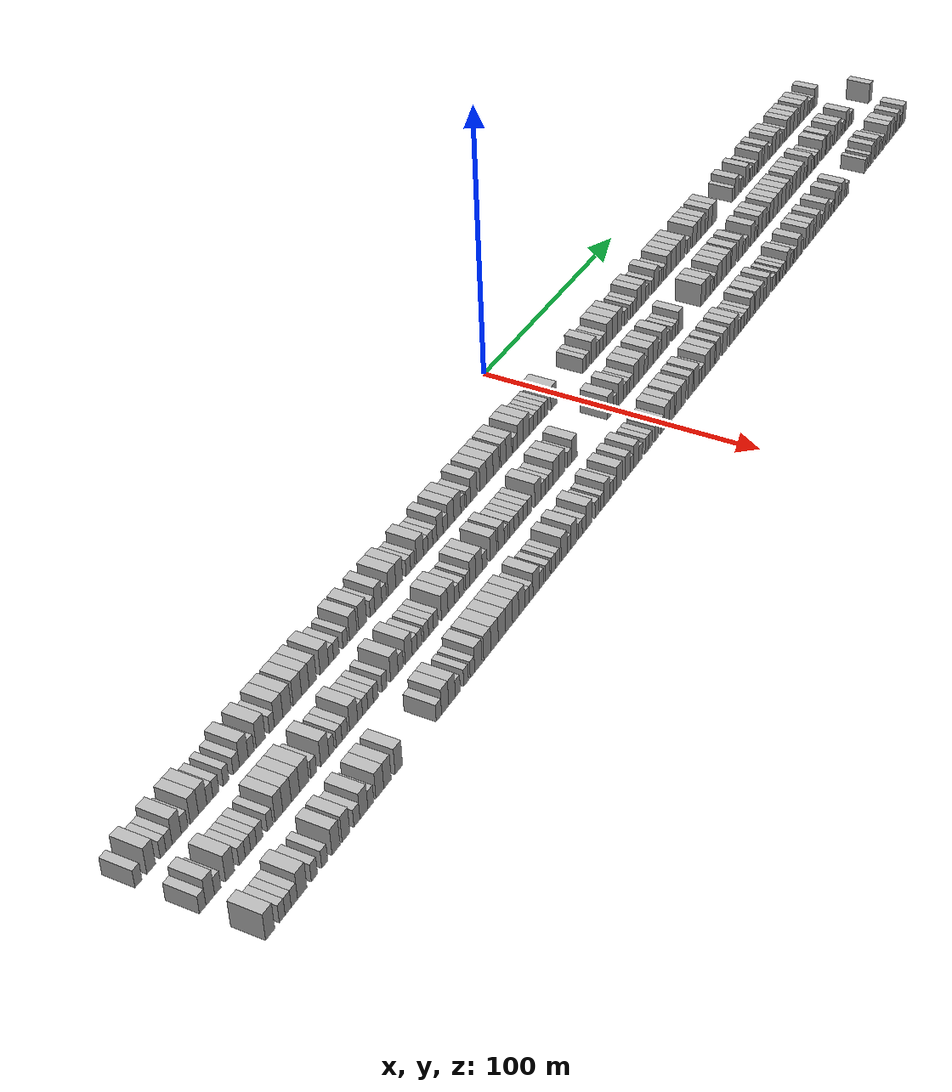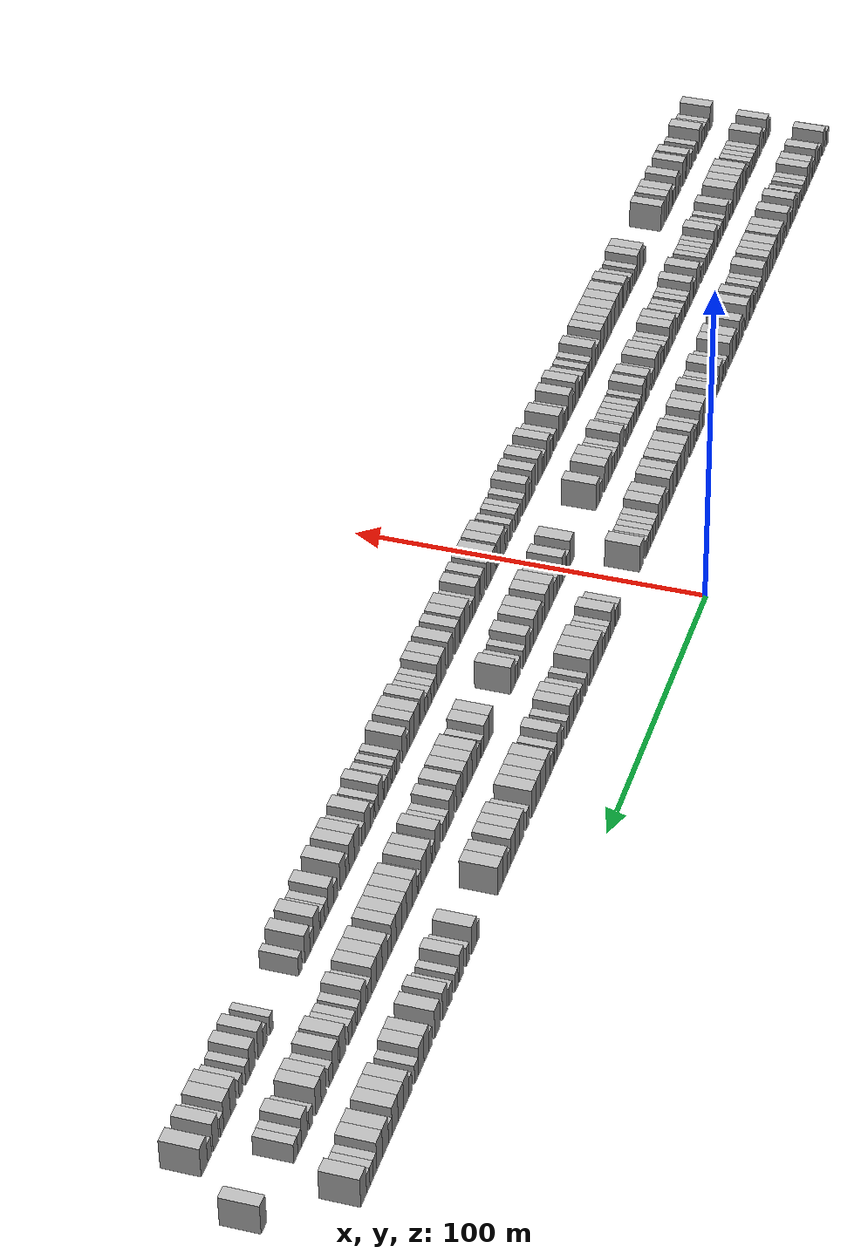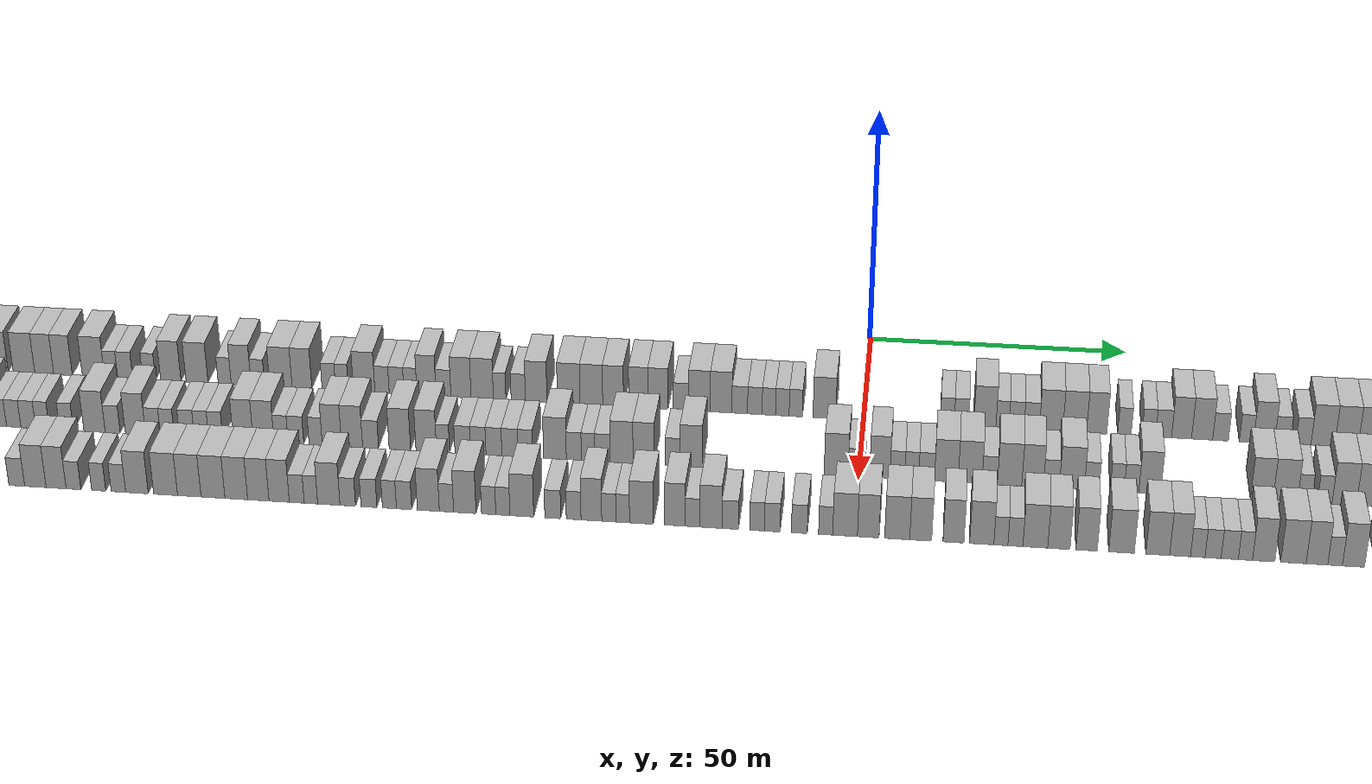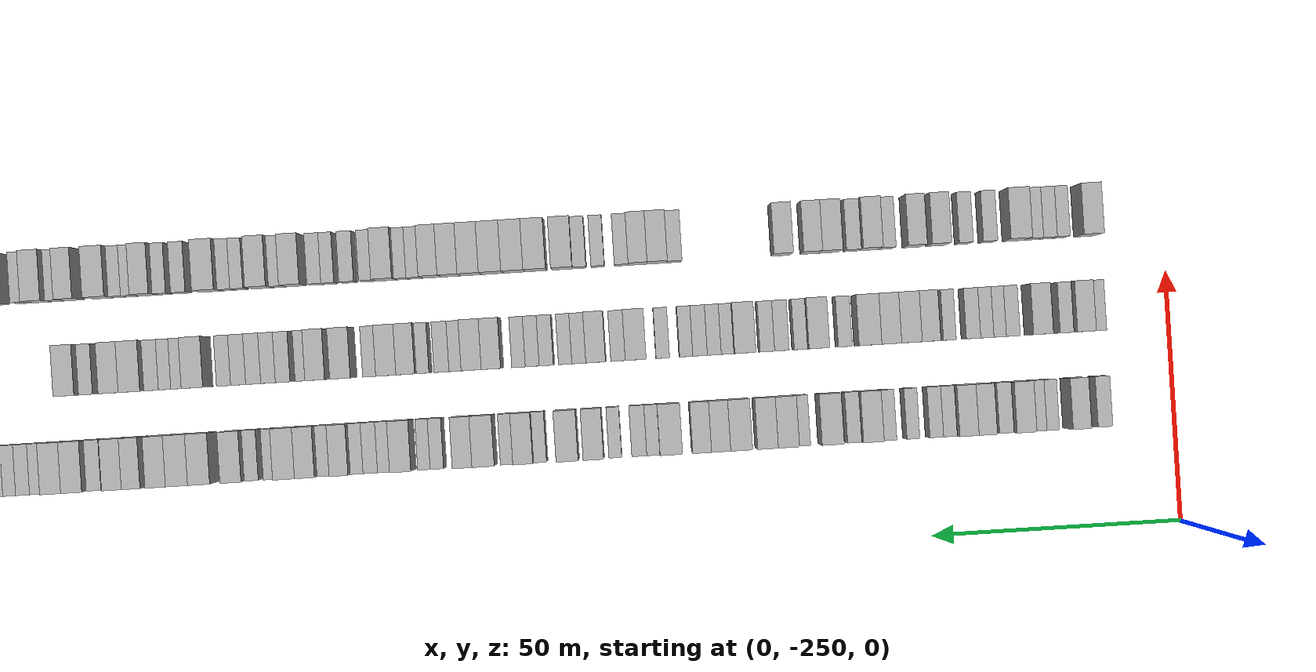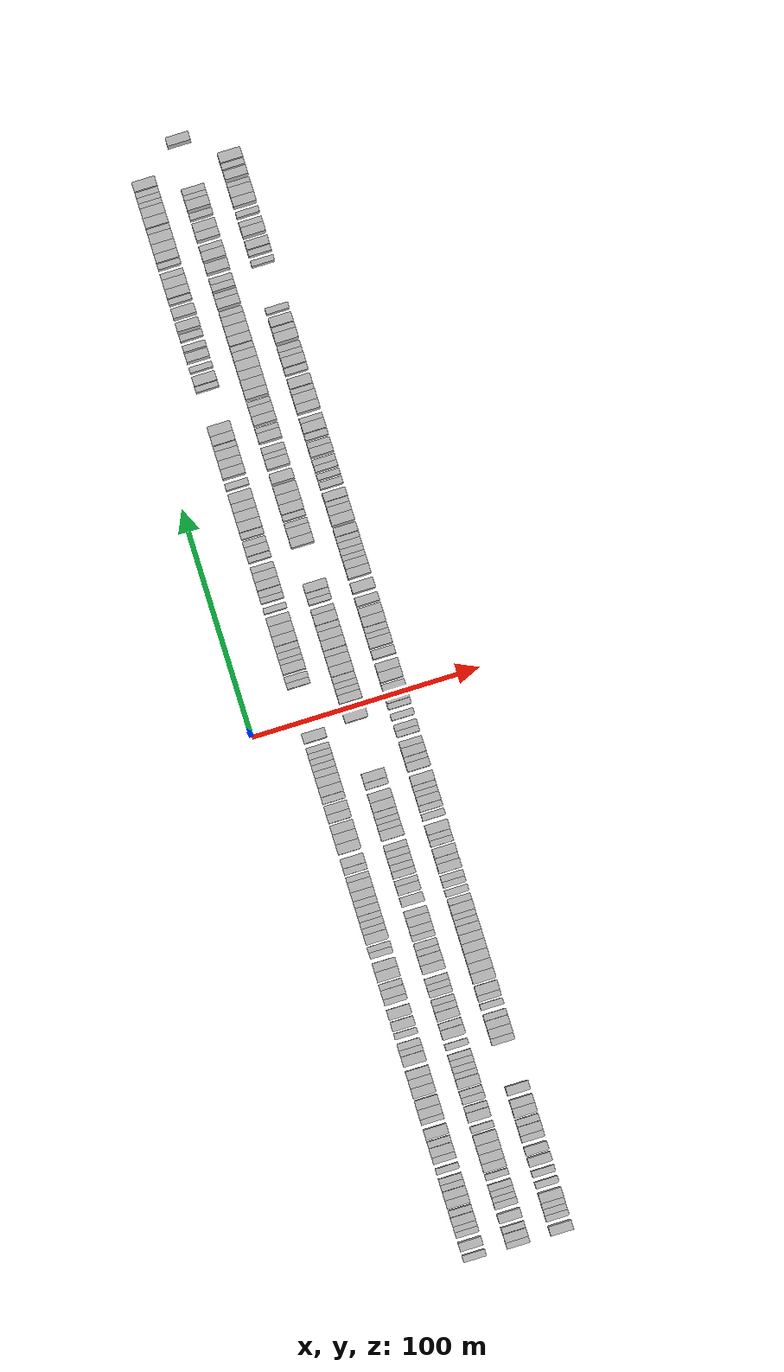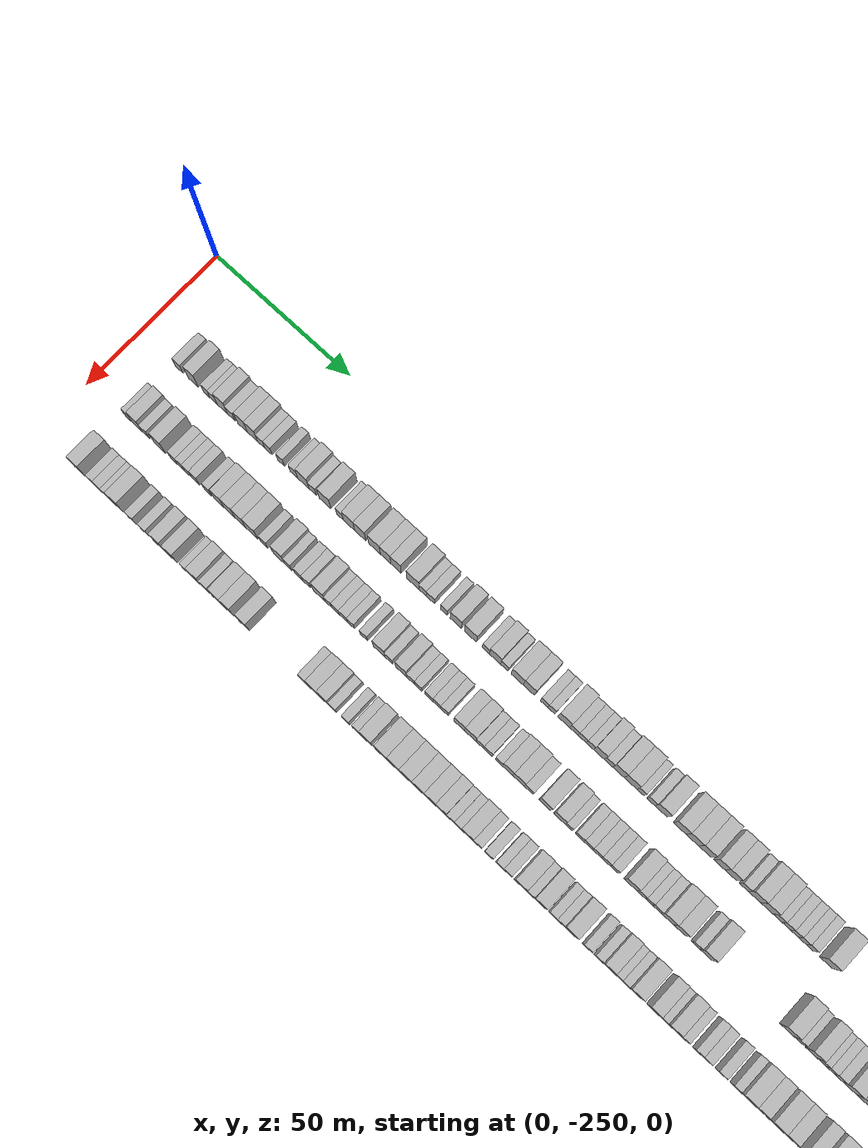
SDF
<sdf version="1.6">
 <world name="default">
  <scene>
   <sky><clouds><speed>12</speed></clouds></sky>
   <ambient>0.4 0.4 0.4 1</ambient>
   <background>0.7 0.7 0.7 1</background>
   <shadows>1</shadows>
  </scene>
  <gravity>0 0 -9.8066</gravity>
  <magnetic_field>6e-06 2.3e-05 -4.2e-05</magnetic_field>
  <physics default="0" name="default_physics" type="ode">
   <ode>
    <solver>
     <type>quick</type>
     <iters>10</iters>
     <sor>1.0</sor>
     <use_dynamic_moi_rescaling>0</use_dynamic_moi_rescaling>
    </solver>
    <constraints>
     <cfm>0</cfm>
     <erp>0.2</erp>
     <contact_max_correcting_vel>100</contact_max_correcting_vel>
     <contact_surface_layer>0.001</contact_surface_layer>
    </constraints>
   </ode>
   <max_step_size>0.004</max_step_size>
   <real_time_factor>1</real_time_factor>
   <real_time_update_rate>250</real_time_update_rate>
  </physics>
  <light name="sun" type="directional">
   <pose>0 0 10 0 0 0</pose>
   <diffuse>0.8 0.8 0.8 1</diffuse>
   <specular>0.2 0.2 0.2 1</specular>
   <attenuation>
    <range>1000</range>
    <constant>0.9</constant>
    <linear>0.01</linear>
    <quadratic>0.001</quadratic>
   </attenuation>
   <direction>-0.5 0.1 -0.9</direction>
  </light>
  <model name="building_1">
   <static>1</static>
   <pose>25.0000 -234.5584 0 0.000000 0.000000 0.000000</pose>
   <link name="link">
    <pose>0 0 3.00 0 0 0</pose>
    <collision name="collision"><geometry><box><size>10.0000 2.8831 6.0000</size></box></geometry></collision>
    <visual name="visual">
     <cast_shadows>0</cast_shadows>
     <geometry><box><size>10.0000 2.8831 6.0000</size></box></geometry>
     <material>
      <script>
       <uri>model://HANNAS_wall/materials/scripts</uri>
       <uri>model://HANNAS_wall/materials/textures</uri>
       <name>vrc/HANNAS_wall</name>
      </script>
     </material>
    </visual>
   </link>
  </model>
  <model name="building_2">
   <static>1</static>
   <pose>25.0000 -229.2970 0 0.000000 0.000000 0.000000</pose>
   <link name="link">
    <pose>0 0 4.50 0 0 0</pose>
    <collision name="collision"><geometry><box><size>10.0000 3.6397 9.0000</size></box></geometry></collision>
    <visual name="visual">
     <cast_shadows>0</cast_shadows>
     <geometry><box><size>10.0000 3.6397 9.0000</size></box></geometry>
     <material>
      <script>
       <uri>model://HANNAS_wall/materials/scripts</uri>
       <uri>model://HANNAS_wall/materials/textures</uri>
       <name>vrc/HANNAS_wall</name>
      </script>
     </material>
    </visual>
   </link>
  </model>
  <model name="building_3">
   <static>1</static>
   <pose>25.0000 -224.2411 0 0.000000 0.000000 0.000000</pose>
   <link name="link">
    <pose>0 0 3.00 0 0 0</pose>
    <collision name="collision"><geometry><box><size>10.0000 2.4721 6.0000</size></box></geometry></collision>
    <visual name="visual">
     <cast_shadows>0</cast_shadows>
     <geometry><box><size>10.0000 2.4721 6.0000</size></box></geometry>
     <material>
      <script>
       <uri>model://HANNAS_wall/materials/scripts</uri>
       <uri>model://HANNAS_wall/materials/textures</uri>
       <name>vrc/HANNAS_wall</name>
      </script>
     </material>
    </visual>
   </link>
  </model>
  <model name="building_4">
   <static>1</static>
   <pose>25.0000 -221.6867 0 0.000000 0.000000 0.000000</pose>
   <link name="link">
    <pose>0 0 3.00 0 0 0</pose>
    <collision name="collision"><geometry><box><size>10.0000 2.6366 6.0000</size></box></geometry></collision>
    <visual name="visual">
     <cast_shadows>0</cast_shadows>
     <geometry><box><size>10.0000 2.6366 6.0000</size></box></geometry>
     <material>
      <script>
       <uri>model://HANNAS_wall/materials/scripts</uri>
       <uri>model://HANNAS_wall/materials/textures</uri>
       <name>vrc/HANNAS_wall</name>
      </script>
     </material>
    </visual>
   </link>
  </model>
  <model name="building_5">
   <static>1</static>
   <pose>25.0000 -218.4335 0 0.000000 0.000000 0.000000</pose>
   <link name="link">
    <pose>0 0 4.50 0 0 0</pose>
    <collision name="collision"><geometry><box><size>10.0000 3.8698 9.0000</size></box></geometry></collision>
    <visual name="visual">
     <cast_shadows>0</cast_shadows>
     <geometry><box><size>10.0000 3.8698 9.0000</size></box></geometry>
     <material>
      <script>
       <uri>model://HANNAS_wall/materials/scripts</uri>
       <uri>model://HANNAS_wall/materials/textures</uri>
       <name>vrc/HANNAS_wall</name>
      </script>
     </material>
    </visual>
   </link>
  </model>
  <model name="building_6">
   <static>1</static>
   <pose>25.0000 -215.0656 0 0.000000 0.000000 0.000000</pose>
   <link name="link">
    <pose>0 0 3.00 0 0 0</pose>
    <collision name="collision"><geometry><box><size>10.0000 2.8660 6.0000</size></box></geometry></collision>
    <visual name="visual">
     <cast_shadows>0</cast_shadows>
     <geometry><box><size>10.0000 2.8660 6.0000</size></box></geometry>
     <material>
      <script>
       <uri>model://HANNAS_wall/materials/scripts</uri>
       <uri>model://HANNAS_wall/materials/textures</uri>
       <name>vrc/HANNAS_wall</name>
      </script>
     </material>
    </visual>
   </link>
  </model>
  <model name="building_7">
   <static>1</static>
   <pose>25.0000 -210.8311 0 0.000000 0.000000 0.000000</pose>
   <link name="link">
    <pose>0 0 4.50 0 0 0</pose>
    <collision name="collision"><geometry><box><size>10.0000 3.6029 9.0000</size></box></geometry></collision>
    <visual name="visual">
     <cast_shadows>0</cast_shadows>
     <geometry><box><size>10.0000 3.6029 9.0000</size></box></geometry>
     <material>
      <script>
       <uri>model://HANNAS_wall/materials/scripts</uri>
       <uri>model://HANNAS_wall/materials/textures</uri>
       <name>vrc/HANNAS_wall</name>
      </script>
     </material>
    </visual>
   </link>
  </model>
  <model name="building_8">
   <static>1</static>
   <pose>25.0000 -207.1484 0 0.000000 0.000000 0.000000</pose>
   <link name="link">
    <pose>0 0 4.50 0 0 0</pose>
    <collision name="collision"><geometry><box><size>10.0000 3.7626 9.0000</size></box></geometry></collision>
    <visual name="visual">
     <cast_shadows>0</cast_shadows>
     <geometry><box><size>10.0000 3.7626 9.0000</size></box></geometry>
     <material>
      <script>
       <uri>model://HANNAS_wall/materials/scripts</uri>
       <uri>model://HANNAS_wall/materials/textures</uri>
       <name>vrc/HANNAS_wall</name>
      </script>
     </material>
    </visual>
   </link>
  </model>
  <model name="building_9">
   <static>1</static>
   <pose>25.0000 -203.9193 0 0.000000 0.000000 0.000000</pose>
   <link name="link">
    <pose>0 0 3.00 0 0 0</pose>
    <collision name="collision"><geometry><box><size>10.0000 2.6956 6.0000</size></box></geometry></collision>
    <visual name="visual">
     <cast_shadows>0</cast_shadows>
     <geometry><box><size>10.0000 2.6956 6.0000</size></box></geometry>
     <material>
      <script>
       <uri>model://HANNAS_wall/materials/scripts</uri>
       <uri>model://HANNAS_wall/materials/textures</uri>
       <name>vrc/HANNAS_wall</name>
      </script>
     </material>
    </visual>
   </link>
  </model>
  <model name="building_10">
   <static>1</static>
   <pose>25.0000 -201.2164 0 0.000000 0.000000 0.000000</pose>
   <link name="link">
    <pose>0 0 3.00 0 0 0</pose>
    <collision name="collision"><geometry><box><size>10.0000 2.7101 6.0000</size></box></geometry></collision>
    <visual name="visual">
     <cast_shadows>0</cast_shadows>
     <geometry><box><size>10.0000 2.7101 6.0000</size></box></geometry>
     <material>
      <script>
       <uri>model://HANNAS_wall/materials/scripts</uri>
       <uri>model://HANNAS_wall/materials/textures</uri>
       <name>vrc/HANNAS_wall</name>
      </script>
     </material>
    </visual>
   </link>
  </model>
  <model name="building_11">
   <static>1</static>
   <pose>25.0000 -196.5911 0 0.000000 0.000000 0.000000</pose>
   <link name="link">
    <pose>0 0 3.00 0 0 0</pose>
    <collision name="collision"><geometry><box><size>10.0000 2.5407 6.0000</size></box></geometry></collision>
    <visual name="visual">
     <cast_shadows>0</cast_shadows>
     <geometry><box><size>10.0000 2.5407 6.0000</size></box></geometry>
     <material>
      <script>
       <uri>model://HANNAS_wall/materials/scripts</uri>
       <uri>model://HANNAS_wall/materials/textures</uri>
       <name>vrc/HANNAS_wall</name>
      </script>
     </material>
    </visual>
   </link>
  </model>
  <model name="building_12">
   <static>1</static>
   <pose>25.0000 -191.8793 0 0.000000 0.000000 0.000000</pose>
   <link name="link">
    <pose>0 0 3.00 0 0 0</pose>
    <collision name="collision"><geometry><box><size>10.0000 2.8828 6.0000</size></box></geometry></collision>
    <visual name="visual">
     <cast_shadows>0</cast_shadows>
     <geometry><box><size>10.0000 2.8828 6.0000</size></box></geometry>
     <material>
      <script>
       <uri>model://HANNAS_wall/materials/scripts</uri>
       <uri>model://HANNAS_wall/materials/textures</uri>
       <name>vrc/HANNAS_wall</name>
      </script>
     </material>
    </visual>
   </link>
  </model>
  <model name="building_13">
   <static>1</static>
   <pose>25.0000 -188.4168 0 0.000000 0.000000 0.000000</pose>
   <link name="link">
    <pose>0 0 4.50 0 0 0</pose>
    <collision name="collision"><geometry><box><size>10.0000 4.0422 9.0000</size></box></geometry></collision>
    <visual name="visual">
     <cast_shadows>0</cast_shadows>
     <geometry><box><size>10.0000 4.0422 9.0000</size></box></geometry>
     <material>
      <script>
       <uri>model://HANNAS_wall/materials/scripts</uri>
       <uri>model://HANNAS_wall/materials/textures</uri>
       <name>vrc/HANNAS_wall</name>
      </script>
     </material>
    </visual>
   </link>
  </model>
  <model name="building_14">
   <static>1</static>
   <pose>25.0000 -184.9974 0 0.000000 0.000000 0.000000</pose>
   <link name="link">
    <pose>0 0 3.00 0 0 0</pose>
    <collision name="collision"><geometry><box><size>10.0000 2.7965 6.0000</size></box></geometry></collision>
    <visual name="visual">
     <cast_shadows>0</cast_shadows>
     <geometry><box><size>10.0000 2.7965 6.0000</size></box></geometry>
     <material>
      <script>
       <uri>model://HANNAS_wall/materials/scripts</uri>
       <uri>model://HANNAS_wall/materials/textures</uri>
       <name>vrc/HANNAS_wall</name>
      </script>
     </material>
    </visual>
   </link>
  </model>
  <model name="building_15">
   <static>1</static>
   <pose>25.0000 -180.4366 0 0.000000 0.000000 0.000000</pose>
   <link name="link">
    <pose>0 0 4.50 0 0 0</pose>
    <collision name="collision"><geometry><box><size>10.0000 4.3251 9.0000</size></box></geometry></collision>
    <visual name="visual">
     <cast_shadows>0</cast_shadows>
     <geometry><box><size>10.0000 4.3251 9.0000</size></box></geometry>
     <material>
      <script>
       <uri>model://HANNAS_wall/materials/scripts</uri>
       <uri>model://HANNAS_wall/materials/textures</uri>
       <name>vrc/HANNAS_wall</name>
      </script>
     </material>
    </visual>
   </link>
  </model>
  <model name="building_16">
   <static>1</static>
   <pose>25.0000 -175.0492 0 0.000000 0.000000 0.000000</pose>
   <link name="link">
    <pose>0 0 3.00 0 0 0</pose>
    <collision name="collision"><geometry><box><size>10.0000 2.4496 6.0000</size></box></geometry></collision>
    <visual name="visual">
     <cast_shadows>0</cast_shadows>
     <geometry><box><size>10.0000 2.4496 6.0000</size></box></geometry>
     <material>
      <script>
       <uri>model://HANNAS_wall/materials/scripts</uri>
       <uri>model://HANNAS_wall/materials/textures</uri>
       <name>vrc/HANNAS_wall</name>
      </script>
     </material>
    </visual>
   </link>
  </model>
  <model name="building_17">
   <static>1</static>
   <pose>25.0000 -171.7545 0 0.000000 0.000000 0.000000</pose>
   <link name="link">
    <pose>0 0 4.50 0 0 0</pose>
    <collision name="collision"><geometry><box><size>10.0000 4.1397 9.0000</size></box></geometry></collision>
    <visual name="visual">
     <cast_shadows>0</cast_shadows>
     <geometry><box><size>10.0000 4.1397 9.0000</size></box></geometry>
     <material>
      <script>
       <uri>model://HANNAS_wall/materials/scripts</uri>
       <uri>model://HANNAS_wall/materials/textures</uri>
       <name>vrc/HANNAS_wall</name>
      </script>
     </material>
    </visual>
   </link>
  </model>
  <model name="building_18">
   <static>1</static>
   <pose>25.0000 -167.6601 0 0.000000 0.000000 0.000000</pose>
   <link name="link">
    <pose>0 0 4.50 0 0 0</pose>
    <collision name="collision"><geometry><box><size>10.0000 4.0493 9.0000</size></box></geometry></collision>
    <visual name="visual">
     <cast_shadows>0</cast_shadows>
     <geometry><box><size>10.0000 4.0493 9.0000</size></box></geometry>
     <material>
      <script>
       <uri>model://HANNAS_wall/materials/scripts</uri>
       <uri>model://HANNAS_wall/materials/textures</uri>
       <name>vrc/HANNAS_wall</name>
      </script>
     </material>
    </visual>
   </link>
  </model>
  <model name="building_19">
   <static>1</static>
   <pose>25.0000 -162.4905 0 0.000000 0.000000 0.000000</pose>
   <link name="link">
    <pose>0 0 4.50 0 0 0</pose>
    <collision name="collision"><geometry><box><size>10.0000 4.2898 9.0000</size></box></geometry></collision>
    <visual name="visual">
     <cast_shadows>0</cast_shadows>
     <geometry><box><size>10.0000 4.2898 9.0000</size></box></geometry>
     <material>
      <script>
       <uri>model://HANNAS_wall/materials/scripts</uri>
       <uri>model://HANNAS_wall/materials/textures</uri>
       <name>vrc/HANNAS_wall</name>
      </script>
     </material>
    </visual>
   </link>
  </model>
  <model name="building_20">
   <static>1</static>
   <pose>25.0000 -158.4677 0 0.000000 0.000000 0.000000</pose>
   <link name="link">
    <pose>0 0 4.50 0 0 0</pose>
    <collision name="collision"><geometry><box><size>10.0000 3.7558 9.0000</size></box></geometry></collision>
    <visual name="visual">
     <cast_shadows>0</cast_shadows>
     <geometry><box><size>10.0000 3.7558 9.0000</size></box></geometry>
     <material>
      <script>
       <uri>model://HANNAS_wall/materials/scripts</uri>
       <uri>model://HANNAS_wall/materials/textures</uri>
       <name>vrc/HANNAS_wall</name>
      </script>
     </material>
    </visual>
   </link>
  </model>
  <model name="building_21">
   <static>1</static>
   <pose>25.0000 -154.7464 0 0.000000 0.000000 0.000000</pose>
   <link name="link">
    <pose>0 0 4.50 0 0 0</pose>
    <collision name="collision"><geometry><box><size>10.0000 3.6868 9.0000</size></box></geometry></collision>
    <visual name="visual">
     <cast_shadows>0</cast_shadows>
     <geometry><box><size>10.0000 3.6868 9.0000</size></box></geometry>
     <material>
      <script>
       <uri>model://HANNAS_wall/materials/scripts</uri>
       <uri>model://HANNAS_wall/materials/textures</uri>
       <name>vrc/HANNAS_wall</name>
      </script>
     </material>
    </visual>
   </link>
  </model>
  <model name="building_22">
   <static>1</static>
   <pose>25.0000 -148.6998 0 0.000000 0.000000 0.000000</pose>
   <link name="link">
    <pose>0 0 4.50 0 0 0</pose>
    <collision name="collision"><geometry><box><size>10.0000 4.4063 9.0000</size></box></geometry></collision>
    <visual name="visual">
     <cast_shadows>0</cast_shadows>
     <geometry><box><size>10.0000 4.4063 9.0000</size></box></geometry>
     <material>
      <script>
       <uri>model://HANNAS_wall/materials/scripts</uri>
       <uri>model://HANNAS_wall/materials/textures</uri>
       <name>vrc/HANNAS_wall</name>
      </script>
     </material>
    </visual>
   </link>
  </model>
  <model name="building_23">
   <static>1</static>
   <pose>25.0000 -145.2001 0 0.000000 0.000000 0.000000</pose>
   <link name="link">
    <pose>0 0 3.00 0 0 0</pose>
    <collision name="collision"><geometry><box><size>10.0000 2.5932 6.0000</size></box></geometry></collision>
    <visual name="visual">
     <cast_shadows>0</cast_shadows>
     <geometry><box><size>10.0000 2.5932 6.0000</size></box></geometry>
     <material>
      <script>
       <uri>model://HANNAS_wall/materials/scripts</uri>
       <uri>model://HANNAS_wall/materials/textures</uri>
       <name>vrc/HANNAS_wall</name>
      </script>
     </material>
    </visual>
   </link>
  </model>
  <model name="building_24">
   <static>1</static>
   <pose>25.0000 -142.4261 0 0.000000 0.000000 0.000000</pose>
   <link name="link">
    <pose>0 0 3.00 0 0 0</pose>
    <collision name="collision"><geometry><box><size>10.0000 2.9548 6.0000</size></box></geometry></collision>
    <visual name="visual">
     <cast_shadows>0</cast_shadows>
     <geometry><box><size>10.0000 2.9548 6.0000</size></box></geometry>
     <material>
      <script>
       <uri>model://HANNAS_wall/materials/scripts</uri>
       <uri>model://HANNAS_wall/materials/textures</uri>
       <name>vrc/HANNAS_wall</name>
      </script>
     </material>
    </visual>
   </link>
  </model>
  <model name="building_25">
   <static>1</static>
   <pose>25.0000 -137.6886 0 0.000000 0.000000 0.000000</pose>
   <link name="link">
    <pose>0 0 3.00 0 0 0</pose>
    <collision name="collision"><geometry><box><size>10.0000 2.5201 6.0000</size></box></geometry></collision>
    <visual name="visual">
     <cast_shadows>0</cast_shadows>
     <geometry><box><size>10.0000 2.5201 6.0000</size></box></geometry>
     <material>
      <script>
       <uri>model://HANNAS_wall/materials/scripts</uri>
       <uri>model://HANNAS_wall/materials/textures</uri>
       <name>vrc/HANNAS_wall</name>
      </script>
     </material>
    </visual>
   </link>
  </model>
  <model name="building_26">
   <static>1</static>
   <pose>25.0000 -133.4198 0 0.000000 0.000000 0.000000</pose>
   <link name="link">
    <pose>0 0 4.50 0 0 0</pose>
    <collision name="collision"><geometry><box><size>10.0000 4.0176 9.0000</size></box></geometry></collision>
    <visual name="visual">
     <cast_shadows>0</cast_shadows>
     <geometry><box><size>10.0000 4.0176 9.0000</size></box></geometry>
     <material>
      <script>
       <uri>model://HANNAS_wall/materials/scripts</uri>
       <uri>model://HANNAS_wall/materials/textures</uri>
       <name>vrc/HANNAS_wall</name>
      </script>
     </material>
    </visual>
   </link>
  </model>
  <model name="building_27">
   <static>1</static>
   <pose>25.0000 -128.2503 0 0.000000 0.000000 0.000000</pose>
   <link name="link">
    <pose>0 0 4.50 0 0 0</pose>
    <collision name="collision"><geometry><box><size>10.0000 4.3213 9.0000</size></box></geometry></collision>
    <visual name="visual">
     <cast_shadows>0</cast_shadows>
     <geometry><box><size>10.0000 4.3213 9.0000</size></box></geometry>
     <material>
      <script>
       <uri>model://HANNAS_wall/materials/scripts</uri>
       <uri>model://HANNAS_wall/materials/textures</uri>
       <name>vrc/HANNAS_wall</name>
      </script>
     </material>
    </visual>
   </link>
  </model>
  <model name="building_28">
   <static>1</static>
   <pose>25.0000 -122.8109 0 0.000000 0.000000 0.000000</pose>
   <link name="link">
    <pose>0 0 3.00 0 0 0</pose>
    <collision name="collision"><geometry><box><size>10.0000 2.5574 6.0000</size></box></geometry></collision>
    <visual name="visual">
     <cast_shadows>0</cast_shadows>
     <geometry><box><size>10.0000 2.5574 6.0000</size></box></geometry>
     <material>
      <script>
       <uri>model://HANNAS_wall/materials/scripts</uri>
       <uri>model://HANNAS_wall/materials/textures</uri>
       <name>vrc/HANNAS_wall</name>
      </script>
     </material>
    </visual>
   </link>
  </model>
  <model name="building_29">
   <static>1</static>
   <pose>25.0000 -119.5761 0 0.000000 0.000000 0.000000</pose>
   <link name="link">
    <pose>0 0 4.50 0 0 0</pose>
    <collision name="collision"><geometry><box><size>10.0000 3.9122 9.0000</size></box></geometry></collision>
    <visual name="visual">
     <cast_shadows>0</cast_shadows>
     <geometry><box><size>10.0000 3.9122 9.0000</size></box></geometry>
     <material>
      <script>
       <uri>model://HANNAS_wall/materials/scripts</uri>
       <uri>model://HANNAS_wall/materials/textures</uri>
       <name>vrc/HANNAS_wall</name>
      </script>
     </material>
    </visual>
   </link>
  </model>
  <model name="building_30">
   <static>1</static>
   <pose>25.0000 -116.2963 0 0.000000 0.000000 0.000000</pose>
   <link name="link">
    <pose>0 0 3.00 0 0 0</pose>
    <collision name="collision"><geometry><box><size>10.0000 2.6474 6.0000</size></box></geometry></collision>
    <visual name="visual">
     <cast_shadows>0</cast_shadows>
     <geometry><box><size>10.0000 2.6474 6.0000</size></box></geometry>
     <material>
      <script>
       <uri>model://HANNAS_wall/materials/scripts</uri>
       <uri>model://HANNAS_wall/materials/textures</uri>
       <name>vrc/HANNAS_wall</name>
      </script>
     </material>
    </visual>
   </link>
  </model>
  <model name="building_31">
   <static>1</static>
   <pose>25.0000 -111.7886 0 0.000000 0.000000 0.000000</pose>
   <link name="link">
    <pose>0 0 4.50 0 0 0</pose>
    <collision name="collision"><geometry><box><size>10.0000 4.3680 9.0000</size></box></geometry></collision>
    <visual name="visual">
     <cast_shadows>0</cast_shadows>
     <geometry><box><size>10.0000 4.3680 9.0000</size></box></geometry>
     <material>
      <script>
       <uri>model://HANNAS_wall/materials/scripts</uri>
       <uri>model://HANNAS_wall/materials/textures</uri>
       <name>vrc/HANNAS_wall</name>
      </script>
     </material>
    </visual>
   </link>
  </model>
  <model name="building_32">
   <static>1</static>
   <pose>25.0000 -107.6757 0 0.000000 0.000000 0.000000</pose>
   <link name="link">
    <pose>0 0 4.50 0 0 0</pose>
    <collision name="collision"><geometry><box><size>10.0000 3.8577 9.0000</size></box></geometry></collision>
    <visual name="visual">
     <cast_shadows>0</cast_shadows>
     <geometry><box><size>10.0000 3.8577 9.0000</size></box></geometry>
     <material>
      <script>
       <uri>model://HANNAS_wall/materials/scripts</uri>
       <uri>model://HANNAS_wall/materials/textures</uri>
       <name>vrc/HANNAS_wall</name>
      </script>
     </material>
    </visual>
   </link>
  </model>
  <model name="building_33">
   <static>1</static>
   <pose>25.0000 -102.4231 0 0.000000 0.000000 0.000000</pose>
   <link name="link">
    <pose>0 0 3.00 0 0 0</pose>
    <collision name="collision"><geometry><box><size>10.0000 2.6474 6.0000</size></box></geometry></collision>
    <visual name="visual">
     <cast_shadows>0</cast_shadows>
     <geometry><box><size>10.0000 2.6474 6.0000</size></box></geometry>
     <material>
      <script>
       <uri>model://HANNAS_wall/materials/scripts</uri>
       <uri>model://HANNAS_wall/materials/textures</uri>
       <name>vrc/HANNAS_wall</name>
      </script>
     </material>
    </visual>
   </link>
  </model>
  <model name="building_34">
   <static>1</static>
   <pose>25.0000 -99.8691 0 0.000000 0.000000 0.000000</pose>
   <link name="link">
    <pose>0 0 3.00 0 0 0</pose>
    <collision name="collision"><geometry><box><size>10.0000 2.4607 6.0000</size></box></geometry></collision>
    <visual name="visual">
     <cast_shadows>0</cast_shadows>
     <geometry><box><size>10.0000 2.4607 6.0000</size></box></geometry>
     <material>
      <script>
       <uri>model://HANNAS_wall/materials/scripts</uri>
       <uri>model://HANNAS_wall/materials/textures</uri>
       <name>vrc/HANNAS_wall</name>
      </script>
     </material>
    </visual>
   </link>
  </model>
  <model name="building_35">
   <static>1</static>
   <pose>25.0000 -95.5506 0 0.000000 0.000000 0.000000</pose>
   <link name="link">
    <pose>0 0 4.50 0 0 0</pose>
    <collision name="collision"><geometry><box><size>10.0000 4.1762 9.0000</size></box></geometry></collision>
    <visual name="visual">
     <cast_shadows>0</cast_shadows>
     <geometry><box><size>10.0000 4.1762 9.0000</size></box></geometry>
     <material>
      <script>
       <uri>model://HANNAS_wall/materials/scripts</uri>
       <uri>model://HANNAS_wall/materials/textures</uri>
       <name>vrc/HANNAS_wall</name>
      </script>
     </material>
    </visual>
   </link>
  </model>
  <model name="building_36">
   <static>1</static>
   <pose>25.0000 -92.0806 0 0.000000 0.000000 0.000000</pose>
   <link name="link">
    <pose>0 0 3.00 0 0 0</pose>
    <collision name="collision"><geometry><box><size>10.0000 2.7638 6.0000</size></box></geometry></collision>
    <visual name="visual">
     <cast_shadows>0</cast_shadows>
     <geometry><box><size>10.0000 2.7638 6.0000</size></box></geometry>
     <material>
      <script>
       <uri>model://HANNAS_wall/materials/scripts</uri>
       <uri>model://HANNAS_wall/materials/textures</uri>
       <name>vrc/HANNAS_wall</name>
      </script>
     </material>
    </visual>
   </link>
  </model>
  <model name="building_37">
   <static>1</static>
   <pose>25.0000 -89.2654 0 0.000000 0.000000 0.000000</pose>
   <link name="link">
    <pose>0 0 3.00 0 0 0</pose>
    <collision name="collision"><geometry><box><size>10.0000 2.8667 6.0000</size></box></geometry></collision>
    <visual name="visual">
     <cast_shadows>0</cast_shadows>
     <geometry><box><size>10.0000 2.8667 6.0000</size></box></geometry>
     <material>
      <script>
       <uri>model://HANNAS_wall/materials/scripts</uri>
       <uri>model://HANNAS_wall/materials/textures</uri>
       <name>vrc/HANNAS_wall</name>
      </script>
     </material>
    </visual>
   </link>
  </model>
  <model name="building_38">
   <static>1</static>
   <pose>25.0000 -86.5704 0 0.000000 0.000000 0.000000</pose>
   <link name="link">
    <pose>0 0 3.00 0 0 0</pose>
    <collision name="collision"><geometry><box><size>10.0000 2.5232 6.0000</size></box></geometry></collision>
    <visual name="visual">
     <cast_shadows>0</cast_shadows>
     <geometry><box><size>10.0000 2.5232 6.0000</size></box></geometry>
     <material>
      <script>
       <uri>model://HANNAS_wall/materials/scripts</uri>
       <uri>model://HANNAS_wall/materials/textures</uri>
       <name>vrc/HANNAS_wall</name>
      </script>
     </material>
    </visual>
   </link>
  </model>
  <model name="building_39">
   <static>1</static>
   <pose>25.0000 -83.4620 0 0.000000 0.000000 0.000000</pose>
   <link name="link">
    <pose>0 0 4.50 0 0 0</pose>
    <collision name="collision"><geometry><box><size>10.0000 3.6937 9.0000</size></box></geometry></collision>
    <visual name="visual">
     <cast_shadows>0</cast_shadows>
     <geometry><box><size>10.0000 3.6937 9.0000</size></box></geometry>
     <material>
      <script>
       <uri>model://HANNAS_wall/materials/scripts</uri>
       <uri>model://HANNAS_wall/materials/textures</uri>
       <name>vrc/HANNAS_wall</name>
      </script>
     </material>
    </visual>
   </link>
  </model>
  <model name="building_40">
   <static>1</static>
   <pose>25.0000 -80.1748 0 0.000000 0.000000 0.000000</pose>
   <link name="link">
    <pose>0 0 3.00 0 0 0</pose>
    <collision name="collision"><geometry><box><size>10.0000 2.8808 6.0000</size></box></geometry></collision>
    <visual name="visual">
     <cast_shadows>0</cast_shadows>
     <geometry><box><size>10.0000 2.8808 6.0000</size></box></geometry>
     <material>
      <script>
       <uri>model://HANNAS_wall/materials/scripts</uri>
       <uri>model://HANNAS_wall/materials/textures</uri>
       <name>vrc/HANNAS_wall</name>
      </script>
     </material>
    </visual>
   </link>
  </model>
  <model name="building_41">
   <static>1</static>
   <pose>25.0000 -76.7838 0 0.000000 0.000000 0.000000</pose>
   <link name="link">
    <pose>0 0 4.50 0 0 0</pose>
    <collision name="collision"><geometry><box><size>10.0000 3.9011 9.0000</size></box></geometry></collision>
    <visual name="visual">
     <cast_shadows>0</cast_shadows>
     <geometry><box><size>10.0000 3.9011 9.0000</size></box></geometry>
     <material>
      <script>
       <uri>model://HANNAS_wall/materials/scripts</uri>
       <uri>model://HANNAS_wall/materials/textures</uri>
       <name>vrc/HANNAS_wall</name>
      </script>
     </material>
    </visual>
   </link>
  </model>
  <model name="building_42">
   <static>1</static>
   <pose>25.0000 -72.6837 0 0.000000 0.000000 0.000000</pose>
   <link name="link">
    <pose>0 0 4.50 0 0 0</pose>
    <collision name="collision"><geometry><box><size>10.0000 4.2991 9.0000</size></box></geometry></collision>
    <visual name="visual">
     <cast_shadows>0</cast_shadows>
     <geometry><box><size>10.0000 4.2991 9.0000</size></box></geometry>
     <material>
      <script>
       <uri>model://HANNAS_wall/materials/scripts</uri>
       <uri>model://HANNAS_wall/materials/textures</uri>
       <name>vrc/HANNAS_wall</name>
      </script>
     </material>
    </visual>
   </link>
  </model>
  <model name="building_43">
   <static>1</static>
   <pose>25.0000 -69.3244 0 0.000000 0.000000 0.000000</pose>
   <link name="link">
    <pose>0 0 3.00 0 0 0</pose>
    <collision name="collision"><geometry><box><size>10.0000 2.4194 6.0000</size></box></geometry></collision>
    <visual name="visual">
     <cast_shadows>0</cast_shadows>
     <geometry><box><size>10.0000 2.4194 6.0000</size></box></geometry>
     <material>
      <script>
       <uri>model://HANNAS_wall/materials/scripts</uri>
       <uri>model://HANNAS_wall/materials/textures</uri>
       <name>vrc/HANNAS_wall</name>
      </script>
     </material>
    </visual>
   </link>
  </model>
  <model name="building_44">
   <static>1</static>
   <pose>25.0000 -65.7298 0 0.000000 0.000000 0.000000</pose>
   <link name="link">
    <pose>0 0 3.00 0 0 0</pose>
    <collision name="collision"><geometry><box><size>10.0000 2.7699 6.0000</size></box></geometry></collision>
    <visual name="visual">
     <cast_shadows>0</cast_shadows>
     <geometry><box><size>10.0000 2.7699 6.0000</size></box></geometry>
     <material>
      <script>
       <uri>model://HANNAS_wall/materials/scripts</uri>
       <uri>model://HANNAS_wall/materials/textures</uri>
       <name>vrc/HANNAS_wall</name>
      </script>
     </material>
    </visual>
   </link>
  </model>
  <model name="building_45">
   <static>1</static>
   <pose>25.0000 -62.2742 0 0.000000 0.000000 0.000000</pose>
   <link name="link">
    <pose>0 0 4.50 0 0 0</pose>
    <collision name="collision"><geometry><box><size>10.0000 4.1415 9.0000</size></box></geometry></collision>
    <visual name="visual">
     <cast_shadows>0</cast_shadows>
     <geometry><box><size>10.0000 4.1415 9.0000</size></box></geometry>
     <material>
      <script>
       <uri>model://HANNAS_wall/materials/scripts</uri>
       <uri>model://HANNAS_wall/materials/textures</uri>
       <name>vrc/HANNAS_wall</name>
      </script>
     </material>
    </visual>
   </link>
  </model>
  <model name="building_46">
   <static>1</static>
   <pose>25.0000 -56.0371 0 0.000000 0.000000 0.000000</pose>
   <link name="link">
    <pose>0 0 4.50 0 0 0</pose>
    <collision name="collision"><geometry><box><size>10.0000 4.3328 9.0000</size></box></geometry></collision>
    <visual name="visual">
     <cast_shadows>0</cast_shadows>
     <geometry><box><size>10.0000 4.3328 9.0000</size></box></geometry>
     <material>
      <script>
       <uri>model://HANNAS_wall/materials/scripts</uri>
       <uri>model://HANNAS_wall/materials/textures</uri>
       <name>vrc/HANNAS_wall</name>
      </script>
     </material>
    </visual>
   </link>
  </model>
  <model name="building_47">
   <static>1</static>
   <pose>25.0000 -51.6983 0 0.000000 0.000000 0.000000</pose>
   <link name="link">
    <pose>0 0 4.50 0 0 0</pose>
    <collision name="collision"><geometry><box><size>10.0000 4.3447 9.0000</size></box></geometry></collision>
    <visual name="visual">
     <cast_shadows>0</cast_shadows>
     <geometry><box><size>10.0000 4.3447 9.0000</size></box></geometry>
     <material>
      <script>
       <uri>model://HANNAS_wall/materials/scripts</uri>
       <uri>model://HANNAS_wall/materials/textures</uri>
       <name>vrc/HANNAS_wall</name>
      </script>
     </material>
    </visual>
   </link>
  </model>
  <model name="building_48">
   <static>1</static>
   <pose>25.0000 -47.5337 0 0.000000 0.000000 0.000000</pose>
   <link name="link">
    <pose>0 0 4.50 0 0 0</pose>
    <collision name="collision"><geometry><box><size>10.0000 3.9846 9.0000</size></box></geometry></collision>
    <visual name="visual">
     <cast_shadows>0</cast_shadows>
     <geometry><box><size>10.0000 3.9846 9.0000</size></box></geometry>
     <material>
      <script>
       <uri>model://HANNAS_wall/materials/scripts</uri>
       <uri>model://HANNAS_wall/materials/textures</uri>
       <name>vrc/HANNAS_wall</name>
      </script>
     </material>
    </visual>
   </link>
  </model>
  <model name="building_49">
   <static>1</static>
   <pose>25.0000 -42.7150 0 0.000000 0.000000 0.000000</pose>
   <link name="link">
    <pose>0 0 4.50 0 0 0</pose>
    <collision name="collision"><geometry><box><size>10.0000 3.6527 9.0000</size></box></geometry></collision>
    <visual name="visual">
     <cast_shadows>0</cast_shadows>
     <geometry><box><size>10.0000 3.6527 9.0000</size></box></geometry>
     <material>
      <script>
       <uri>model://HANNAS_wall/materials/scripts</uri>
       <uri>model://HANNAS_wall/materials/textures</uri>
       <name>vrc/HANNAS_wall</name>
      </script>
     </material>
    </visual>
   </link>
  </model>
  <model name="building_50">
   <static>1</static>
   <pose>25.0000 -38.9577 0 0.000000 0.000000 0.000000</pose>
   <link name="link">
    <pose>0 0 4.50 0 0 0</pose>
    <collision name="collision"><geometry><box><size>10.0000 3.8619 9.0000</size></box></geometry></collision>
    <visual name="visual">
     <cast_shadows>0</cast_shadows>
     <geometry><box><size>10.0000 3.8619 9.0000</size></box></geometry>
     <material>
      <script>
       <uri>model://HANNAS_wall/materials/scripts</uri>
       <uri>model://HANNAS_wall/materials/textures</uri>
       <name>vrc/HANNAS_wall</name>
      </script>
     </material>
    </visual>
   </link>
  </model>
  <model name="building_51">
   <static>1</static>
   <pose>25.0000 -34.5754 0 0.000000 0.000000 0.000000</pose>
   <link name="link">
    <pose>0 0 3.00 0 0 0</pose>
    <collision name="collision"><geometry><box><size>10.0000 2.9027 6.0000</size></box></geometry></collision>
    <visual name="visual">
     <cast_shadows>0</cast_shadows>
     <geometry><box><size>10.0000 2.9027 6.0000</size></box></geometry>
     <material>
      <script>
       <uri>model://HANNAS_wall/materials/scripts</uri>
       <uri>model://HANNAS_wall/materials/textures</uri>
       <name>vrc/HANNAS_wall</name>
      </script>
     </material>
    </visual>
   </link>
  </model>
  <model name="building_52">
   <static>1</static>
   <pose>25.0000 -31.0607 0 0.000000 0.000000 0.000000</pose>
   <link name="link">
    <pose>0 0 4.50 0 0 0</pose>
    <collision name="collision"><geometry><box><size>10.0000 4.1267 9.0000</size></box></geometry></collision>
    <visual name="visual">
     <cast_shadows>0</cast_shadows>
     <geometry><box><size>10.0000 4.1267 9.0000</size></box></geometry>
     <material>
      <script>
       <uri>model://HANNAS_wall/materials/scripts</uri>
       <uri>model://HANNAS_wall/materials/textures</uri>
       <name>vrc/HANNAS_wall</name>
      </script>
     </material>
    </visual>
   </link>
  </model>
  <model name="building_53">
   <static>1</static>
   <pose>25.0000 -26.9450 0 0.000000 0.000000 0.000000</pose>
   <link name="link">
    <pose>0 0 4.50 0 0 0</pose>
    <collision name="collision"><geometry><box><size>10.0000 4.1048 9.0000</size></box></geometry></collision>
    <visual name="visual">
     <cast_shadows>0</cast_shadows>
     <geometry><box><size>10.0000 4.1048 9.0000</size></box></geometry>
     <material>
      <script>
       <uri>model://HANNAS_wall/materials/scripts</uri>
       <uri>model://HANNAS_wall/materials/textures</uri>
       <name>vrc/HANNAS_wall</name>
      </script>
     </material>
    </visual>
   </link>
  </model>
  <model name="building_54">
   <static>1</static>
   <pose>25.0000 -23.4114 0 0.000000 0.000000 0.000000</pose>
   <link name="link">
    <pose>0 0 3.00 0 0 0</pose>
    <collision name="collision"><geometry><box><size>10.0000 2.9624 6.0000</size></box></geometry></collision>
    <visual name="visual">
     <cast_shadows>0</cast_shadows>
     <geometry><box><size>10.0000 2.9624 6.0000</size></box></geometry>
     <material>
      <script>
       <uri>model://HANNAS_wall/materials/scripts</uri>
       <uri>model://HANNAS_wall/materials/textures</uri>
       <name>vrc/HANNAS_wall</name>
      </script>
     </material>
    </visual>
   </link>
  </model>
  <model name="building_55">
   <static>1</static>
   <pose>25.0000 -20.5487 0 0.000000 0.000000 0.000000</pose>
   <link name="link">
    <pose>0 0 3.00 0 0 0</pose>
    <collision name="collision"><geometry><box><size>10.0000 2.7631 6.0000</size></box></geometry></collision>
    <visual name="visual">
     <cast_shadows>0</cast_shadows>
     <geometry><box><size>10.0000 2.7631 6.0000</size></box></geometry>
     <material>
      <script>
       <uri>model://HANNAS_wall/materials/scripts</uri>
       <uri>model://HANNAS_wall/materials/textures</uri>
       <name>vrc/HANNAS_wall</name>
      </script>
     </material>
    </visual>
   </link>
  </model>
  <model name="building_56">
   <static>1</static>
   <pose>25.0000 -17.9032 0 0.000000 0.000000 0.000000</pose>
   <link name="link">
    <pose>0 0 3.00 0 0 0</pose>
    <collision name="collision"><geometry><box><size>10.0000 2.5278 6.0000</size></box></geometry></collision>
    <visual name="visual">
     <cast_shadows>0</cast_shadows>
     <geometry><box><size>10.0000 2.5278 6.0000</size></box></geometry>
     <material>
      <script>
       <uri>model://HANNAS_wall/materials/scripts</uri>
       <uri>model://HANNAS_wall/materials/textures</uri>
       <name>vrc/HANNAS_wall</name>
      </script>
     </material>
    </visual>
   </link>
  </model>
  <model name="building_57">
   <static>1</static>
   <pose>25.0000 -15.3460 0 0.000000 0.000000 0.000000</pose>
   <link name="link">
    <pose>0 0 3.00 0 0 0</pose>
    <collision name="collision"><geometry><box><size>10.0000 2.5867 6.0000</size></box></geometry></collision>
    <visual name="visual">
     <cast_shadows>0</cast_shadows>
     <geometry><box><size>10.0000 2.5867 6.0000</size></box></geometry>
     <material>
      <script>
       <uri>model://HANNAS_wall/materials/scripts</uri>
       <uri>model://HANNAS_wall/materials/textures</uri>
       <name>vrc/HANNAS_wall</name>
      </script>
     </material>
    </visual>
   </link>
  </model>
  <model name="building_58">
   <static>1</static>
   <pose>25.0000 -12.7959 0 0.000000 0.000000 0.000000</pose>
   <link name="link">
    <pose>0 0 3.00 0 0 0</pose>
    <collision name="collision"><geometry><box><size>10.0000 2.5135 6.0000</size></box></geometry></collision>
    <visual name="visual">
     <cast_shadows>0</cast_shadows>
     <geometry><box><size>10.0000 2.5135 6.0000</size></box></geometry>
     <material>
      <script>
       <uri>model://HANNAS_wall/materials/scripts</uri>
       <uri>model://HANNAS_wall/materials/textures</uri>
       <name>vrc/HANNAS_wall</name>
      </script>
     </material>
    </visual>
   </link>
  </model>
  <model name="building_59">
   <static>1</static>
   <pose>25.0000 -7.3922 0 0.000000 0.000000 0.000000</pose>
   <link name="link">
    <pose>0 0 4.50 0 0 0</pose>
    <collision name="collision"><geometry><box><size>10.0000 4.2938 9.0000</size></box></geometry></collision>
    <visual name="visual">
     <cast_shadows>0</cast_shadows>
     <geometry><box><size>10.0000 4.2938 9.0000</size></box></geometry>
     <material>
      <script>
       <uri>model://HANNAS_wall/materials/scripts</uri>
       <uri>model://HANNAS_wall/materials/textures</uri>
       <name>vrc/HANNAS_wall</name>
      </script>
     </material>
    </visual>
   </link>
  </model>
  <model name="building_60">
   <static>1</static>
   <pose>25.0000 15.6666 0 0.000000 0.000000 0.000000</pose>
   <link name="link">
    <pose>0 0 3.00 0 0 0</pose>
    <collision name="collision"><geometry><box><size>10.0000 2.6079 6.0000</size></box></geometry></collision>
    <visual name="visual">
     <cast_shadows>0</cast_shadows>
     <geometry><box><size>10.0000 2.6079 6.0000</size></box></geometry>
     <material>
      <script>
       <uri>model://HANNAS_wall/materials/scripts</uri>
       <uri>model://HANNAS_wall/materials/textures</uri>
       <name>vrc/HANNAS_wall</name>
      </script>
     </material>
    </visual>
   </link>
  </model>
  <model name="building_61">
   <static>1</static>
   <pose>25.0000 18.3108 0 0.000000 0.000000 0.000000</pose>
   <link name="link">
    <pose>0 0 3.00 0 0 0</pose>
    <collision name="collision"><geometry><box><size>10.0000 2.6805 6.0000</size></box></geometry></collision>
    <visual name="visual">
     <cast_shadows>0</cast_shadows>
     <geometry><box><size>10.0000 2.6805 6.0000</size></box></geometry>
     <material>
      <script>
       <uri>model://HANNAS_wall/materials/scripts</uri>
       <uri>model://HANNAS_wall/materials/textures</uri>
       <name>vrc/HANNAS_wall</name>
      </script>
     </material>
    </visual>
   </link>
  </model>
  <model name="building_62">
   <static>1</static>
   <pose>25.0000 22.7149 0 0.000000 0.000000 0.000000</pose>
   <link name="link">
    <pose>0 0 4.50 0 0 0</pose>
    <collision name="collision"><geometry><box><size>10.0000 4.1275 9.0000</size></box></geometry></collision>
    <visual name="visual">
     <cast_shadows>0</cast_shadows>
     <geometry><box><size>10.0000 4.1275 9.0000</size></box></geometry>
     <material>
      <script>
       <uri>model://HANNAS_wall/materials/scripts</uri>
       <uri>model://HANNAS_wall/materials/textures</uri>
       <name>vrc/HANNAS_wall</name>
      </script>
     </material>
    </visual>
   </link>
  </model>
  <model name="building_63">
   <static>1</static>
   <pose>25.0000 25.9789 0 0.000000 0.000000 0.000000</pose>
   <link name="link">
    <pose>0 0 3.00 0 0 0</pose>
    <collision name="collision"><geometry><box><size>10.0000 2.4006 6.0000</size></box></geometry></collision>
    <visual name="visual">
     <cast_shadows>0</cast_shadows>
     <geometry><box><size>10.0000 2.4006 6.0000</size></box></geometry>
     <material>
      <script>
       <uri>model://HANNAS_wall/materials/scripts</uri>
       <uri>model://HANNAS_wall/materials/textures</uri>
       <name>vrc/HANNAS_wall</name>
      </script>
     </material>
    </visual>
   </link>
  </model>
  <model name="building_64">
   <static>1</static>
   <pose>25.0000 28.5937 0 0.000000 0.000000 0.000000</pose>
   <link name="link">
    <pose>0 0 3.00 0 0 0</pose>
    <collision name="collision"><geometry><box><size>10.0000 2.8291 6.0000</size></box></geometry></collision>
    <visual name="visual">
     <cast_shadows>0</cast_shadows>
     <geometry><box><size>10.0000 2.8291 6.0000</size></box></geometry>
     <material>
      <script>
       <uri>model://HANNAS_wall/materials/scripts</uri>
       <uri>model://HANNAS_wall/materials/textures</uri>
       <name>vrc/HANNAS_wall</name>
      </script>
     </material>
    </visual>
   </link>
  </model>
  <model name="building_65">
   <static>1</static>
   <pose>25.0000 31.4363 0 0.000000 0.000000 0.000000</pose>
   <link name="link">
    <pose>0 0 3.00 0 0 0</pose>
    <collision name="collision"><geometry><box><size>10.0000 2.8561 6.0000</size></box></geometry></collision>
    <visual name="visual">
     <cast_shadows>0</cast_shadows>
     <geometry><box><size>10.0000 2.8561 6.0000</size></box></geometry>
     <material>
      <script>
       <uri>model://HANNAS_wall/materials/scripts</uri>
       <uri>model://HANNAS_wall/materials/textures</uri>
       <name>vrc/HANNAS_wall</name>
      </script>
     </material>
    </visual>
   </link>
  </model>
  <model name="building_66">
   <static>1</static>
   <pose>25.0000 35.0451 0 0.000000 0.000000 0.000000</pose>
   <link name="link">
    <pose>0 0 4.50 0 0 0</pose>
    <collision name="collision"><geometry><box><size>10.0000 4.3615 9.0000</size></box></geometry></collision>
    <visual name="visual">
     <cast_shadows>0</cast_shadows>
     <geometry><box><size>10.0000 4.3615 9.0000</size></box></geometry>
     <material>
      <script>
       <uri>model://HANNAS_wall/materials/scripts</uri>
       <uri>model://HANNAS_wall/materials/textures</uri>
       <name>vrc/HANNAS_wall</name>
      </script>
     </material>
    </visual>
   </link>
  </model>
  <model name="building_67">
   <static>1</static>
   <pose>25.0000 39.4360 0 0.000000 0.000000 0.000000</pose>
   <link name="link">
    <pose>0 0 4.50 0 0 0</pose>
    <collision name="collision"><geometry><box><size>10.0000 4.4203 9.0000</size></box></geometry></collision>
    <visual name="visual">
     <cast_shadows>0</cast_shadows>
     <geometry><box><size>10.0000 4.4203 9.0000</size></box></geometry>
     <material>
      <script>
       <uri>model://HANNAS_wall/materials/scripts</uri>
       <uri>model://HANNAS_wall/materials/textures</uri>
       <name>vrc/HANNAS_wall</name>
      </script>
     </material>
    </visual>
   </link>
  </model>
  <model name="building_68">
   <static>1</static>
   <pose>25.0000 43.5240 0 0.000000 0.000000 0.000000</pose>
   <link name="link">
    <pose>0 0 4.50 0 0 0</pose>
    <collision name="collision"><geometry><box><size>10.0000 3.7559 9.0000</size></box></geometry></collision>
    <visual name="visual">
     <cast_shadows>0</cast_shadows>
     <geometry><box><size>10.0000 3.7559 9.0000</size></box></geometry>
     <material>
      <script>
       <uri>model://HANNAS_wall/materials/scripts</uri>
       <uri>model://HANNAS_wall/materials/textures</uri>
       <name>vrc/HANNAS_wall</name>
      </script>
     </material>
    </visual>
   </link>
  </model>
  <model name="building_69">
   <static>1</static>
   <pose>25.0000 48.6498 0 0.000000 0.000000 0.000000</pose>
   <link name="link">
    <pose>0 0 3.00 0 0 0</pose>
    <collision name="collision"><geometry><box><size>10.0000 2.4956 6.0000</size></box></geometry></collision>
    <visual name="visual">
     <cast_shadows>0</cast_shadows>
     <geometry><box><size>10.0000 2.4956 6.0000</size></box></geometry>
     <material>
      <script>
       <uri>model://HANNAS_wall/materials/scripts</uri>
       <uri>model://HANNAS_wall/materials/textures</uri>
       <name>vrc/HANNAS_wall</name>
      </script>
     </material>
    </visual>
   </link>
  </model>
  <model name="building_70">
   <static>1</static>
   <pose>25.0000 53.1638 0 0.000000 0.000000 0.000000</pose>
   <link name="link">
    <pose>0 0 3.00 0 0 0</pose>
    <collision name="collision"><geometry><box><size>10.0000 2.5325 6.0000</size></box></geometry></collision>
    <visual name="visual">
     <cast_shadows>0</cast_shadows>
     <geometry><box><size>10.0000 2.5325 6.0000</size></box></geometry>
     <material>
      <script>
       <uri>model://HANNAS_wall/materials/scripts</uri>
       <uri>model://HANNAS_wall/materials/textures</uri>
       <name>vrc/HANNAS_wall</name>
      </script>
     </material>
    </visual>
   </link>
  </model>
  <model name="building_71">
   <static>1</static>
   <pose>25.0000 55.8989 0 0.000000 0.000000 0.000000</pose>
   <link name="link">
    <pose>0 0 3.00 0 0 0</pose>
    <collision name="collision"><geometry><box><size>10.0000 2.9376 6.0000</size></box></geometry></collision>
    <visual name="visual">
     <cast_shadows>0</cast_shadows>
     <geometry><box><size>10.0000 2.9376 6.0000</size></box></geometry>
     <material>
      <script>
       <uri>model://HANNAS_wall/materials/scripts</uri>
       <uri>model://HANNAS_wall/materials/textures</uri>
       <name>vrc/HANNAS_wall</name>
      </script>
     </material>
    </visual>
   </link>
  </model>
  <model name="building_72">
   <static>1</static>
   <pose>25.0000 59.2158 0 0.000000 0.000000 0.000000</pose>
   <link name="link">
    <pose>0 0 4.50 0 0 0</pose>
    <collision name="collision"><geometry><box><size>10.0000 3.6962 9.0000</size></box></geometry></collision>
    <visual name="visual">
     <cast_shadows>0</cast_shadows>
     <geometry><box><size>10.0000 3.6962 9.0000</size></box></geometry>
     <material>
      <script>
       <uri>model://HANNAS_wall/materials/scripts</uri>
       <uri>model://HANNAS_wall/materials/textures</uri>
       <name>vrc/HANNAS_wall</name>
      </script>
     </material>
    </visual>
   </link>
  </model>
  <model name="building_73">
   <static>1</static>
   <pose>25.0000 63.0143 0 0.000000 0.000000 0.000000</pose>
   <link name="link">
    <pose>0 0 4.50 0 0 0</pose>
    <collision name="collision"><geometry><box><size>10.0000 3.9007 9.0000</size></box></geometry></collision>
    <visual name="visual">
     <cast_shadows>0</cast_shadows>
     <geometry><box><size>10.0000 3.9007 9.0000</size></box></geometry>
     <material>
      <script>
       <uri>model://HANNAS_wall/materials/scripts</uri>
       <uri>model://HANNAS_wall/materials/textures</uri>
       <name>vrc/HANNAS_wall</name>
      </script>
     </material>
    </visual>
   </link>
  </model>
  <model name="building_74">
   <static>1</static>
   <pose>25.0000 66.4072 0 0.000000 0.000000 0.000000</pose>
   <link name="link">
    <pose>0 0 3.00 0 0 0</pose>
    <collision name="collision"><geometry><box><size>10.0000 2.8851 6.0000</size></box></geometry></collision>
    <visual name="visual">
     <cast_shadows>0</cast_shadows>
     <geometry><box><size>10.0000 2.8851 6.0000</size></box></geometry>
     <material>
      <script>
       <uri>model://HANNAS_wall/materials/scripts</uri>
       <uri>model://HANNAS_wall/materials/textures</uri>
       <name>vrc/HANNAS_wall</name>
      </script>
     </material>
    </visual>
   </link>
  </model>
  <model name="building_75">
   <static>1</static>
   <pose>25.0000 71.1329 0 0.000000 0.000000 0.000000</pose>
   <link name="link">
    <pose>0 0 3.00 0 0 0</pose>
    <collision name="collision"><geometry><box><size>10.0000 2.5662 6.0000</size></box></geometry></collision>
    <visual name="visual">
     <cast_shadows>0</cast_shadows>
     <geometry><box><size>10.0000 2.5662 6.0000</size></box></geometry>
     <material>
      <script>
       <uri>model://HANNAS_wall/materials/scripts</uri>
       <uri>model://HANNAS_wall/materials/textures</uri>
       <name>vrc/HANNAS_wall</name>
      </script>
     </material>
    </visual>
   </link>
  </model>
  <model name="building_76">
   <static>1</static>
   <pose>25.0000 74.3617 0 0.000000 0.000000 0.000000</pose>
   <link name="link">
    <pose>0 0 4.50 0 0 0</pose>
    <collision name="collision"><geometry><box><size>10.0000 3.8914 9.0000</size></box></geometry></collision>
    <visual name="visual">
     <cast_shadows>0</cast_shadows>
     <geometry><box><size>10.0000 3.8914 9.0000</size></box></geometry>
     <material>
      <script>
       <uri>model://HANNAS_wall/materials/scripts</uri>
       <uri>model://HANNAS_wall/materials/textures</uri>
       <name>vrc/HANNAS_wall</name>
      </script>
     </material>
    </visual>
   </link>
  </model>
  <model name="building_77">
   <static>1</static>
   <pose>25.0000 77.7268 0 0.000000 0.000000 0.000000</pose>
   <link name="link">
    <pose>0 0 3.00 0 0 0</pose>
    <collision name="collision"><geometry><box><size>10.0000 2.8389 6.0000</size></box></geometry></collision>
    <visual name="visual">
     <cast_shadows>0</cast_shadows>
     <geometry><box><size>10.0000 2.8389 6.0000</size></box></geometry>
     <material>
      <script>
       <uri>model://HANNAS_wall/materials/scripts</uri>
       <uri>model://HANNAS_wall/materials/textures</uri>
       <name>vrc/HANNAS_wall</name>
      </script>
     </material>
    </visual>
   </link>
  </model>
  <model name="building_78">
   <static>1</static>
   <pose>25.0000 81.5489 0 0.000000 0.000000 0.000000</pose>
   <link name="link">
    <pose>0 0 3.00 0 0 0</pose>
    <collision name="collision"><geometry><box><size>10.0000 2.8052 6.0000</size></box></geometry></collision>
    <visual name="visual">
     <cast_shadows>0</cast_shadows>
     <geometry><box><size>10.0000 2.8052 6.0000</size></box></geometry>
     <material>
      <script>
       <uri>model://HANNAS_wall/materials/scripts</uri>
       <uri>model://HANNAS_wall/materials/textures</uri>
       <name>vrc/HANNAS_wall</name>
      </script>
     </material>
    </visual>
   </link>
  </model>
  <model name="building_79">
   <static>1</static>
   <pose>25.0000 85.1186 0 0.000000 0.000000 0.000000</pose>
   <link name="link">
    <pose>0 0 4.50 0 0 0</pose>
    <collision name="collision"><geometry><box><size>10.0000 4.3343 9.0000</size></box></geometry></collision>
    <visual name="visual">
     <cast_shadows>0</cast_shadows>
     <geometry><box><size>10.0000 4.3343 9.0000</size></box></geometry>
     <material>
      <script>
       <uri>model://HANNAS_wall/materials/scripts</uri>
       <uri>model://HANNAS_wall/materials/textures</uri>
       <name>vrc/HANNAS_wall</name>
      </script>
     </material>
    </visual>
   </link>
  </model>
  <model name="building_80">
   <static>1</static>
   <pose>25.0000 89.4194 0 0.000000 0.000000 0.000000</pose>
   <link name="link">
    <pose>0 0 4.50 0 0 0</pose>
    <collision name="collision"><geometry><box><size>10.0000 4.2675 9.0000</size></box></geometry></collision>
    <visual name="visual">
     <cast_shadows>0</cast_shadows>
     <geometry><box><size>10.0000 4.2675 9.0000</size></box></geometry>
     <material>
      <script>
       <uri>model://HANNAS_wall/materials/scripts</uri>
       <uri>model://HANNAS_wall/materials/textures</uri>
       <name>vrc/HANNAS_wall</name>
      </script>
     </material>
    </visual>
   </link>
  </model>
  <model name="building_81">
   <static>1</static>
   <pose>25.0000 93.4968 0 0.000000 0.000000 0.000000</pose>
   <link name="link">
    <pose>0 0 4.50 0 0 0</pose>
    <collision name="collision"><geometry><box><size>10.0000 3.8871 9.0000</size></box></geometry></collision>
    <visual name="visual">
     <cast_shadows>0</cast_shadows>
     <geometry><box><size>10.0000 3.8871 9.0000</size></box></geometry>
     <material>
      <script>
       <uri>model://HANNAS_wall/materials/scripts</uri>
       <uri>model://HANNAS_wall/materials/textures</uri>
       <name>vrc/HANNAS_wall</name>
      </script>
     </material>
    </visual>
   </link>
  </model>
  <model name="building_82">
   <static>1</static>
   <pose>25.0000 97.5959 0 0.000000 0.000000 0.000000</pose>
   <link name="link">
    <pose>0 0 4.50 0 0 0</pose>
    <collision name="collision"><geometry><box><size>10.0000 4.3111 9.0000</size></box></geometry></collision>
    <visual name="visual">
     <cast_shadows>0</cast_shadows>
     <geometry><box><size>10.0000 4.3111 9.0000</size></box></geometry>
     <material>
      <script>
       <uri>model://HANNAS_wall/materials/scripts</uri>
       <uri>model://HANNAS_wall/materials/textures</uri>
       <name>vrc/HANNAS_wall</name>
      </script>
     </material>
    </visual>
   </link>
  </model>
  <model name="building_83">
   <static>1</static>
   <pose>25.0000 103.1786 0 0.000000 0.000000 0.000000</pose>
   <link name="link">
    <pose>0 0 3.00 0 0 0</pose>
    <collision name="collision"><geometry><box><size>10.0000 2.8544 6.0000</size></box></geometry></collision>
    <visual name="visual">
     <cast_shadows>0</cast_shadows>
     <geometry><box><size>10.0000 2.8544 6.0000</size></box></geometry>
     <material>
      <script>
       <uri>model://HANNAS_wall/materials/scripts</uri>
       <uri>model://HANNAS_wall/materials/textures</uri>
       <name>vrc/HANNAS_wall</name>
      </script>
     </material>
    </visual>
   </link>
  </model>
  <model name="building_84">
   <static>1</static>
   <pose>25.0000 108.6445 0 0.000000 0.000000 0.000000</pose>
   <link name="link">
    <pose>0 0 4.50 0 0 0</pose>
    <collision name="collision"><geometry><box><size>10.0000 4.0773 9.0000</size></box></geometry></collision>
    <visual name="visual">
     <cast_shadows>0</cast_shadows>
     <geometry><box><size>10.0000 4.0773 9.0000</size></box></geometry>
     <material>
      <script>
       <uri>model://HANNAS_wall/materials/scripts</uri>
       <uri>model://HANNAS_wall/materials/textures</uri>
       <name>vrc/HANNAS_wall</name>
      </script>
     </material>
    </visual>
   </link>
  </model>
  <model name="building_85">
   <static>1</static>
   <pose>25.0000 112.5659 0 0.000000 0.000000 0.000000</pose>
   <link name="link">
    <pose>0 0 4.50 0 0 0</pose>
    <collision name="collision"><geometry><box><size>10.0000 3.7657 9.0000</size></box></geometry></collision>
    <visual name="visual">
     <cast_shadows>0</cast_shadows>
     <geometry><box><size>10.0000 3.7657 9.0000</size></box></geometry>
     <material>
      <script>
       <uri>model://HANNAS_wall/materials/scripts</uri>
       <uri>model://HANNAS_wall/materials/textures</uri>
       <name>vrc/HANNAS_wall</name>
      </script>
     </material>
    </visual>
   </link>
  </model>
  <model name="building_86">
   <static>1</static>
   <pose>25.0000 116.4898 0 0.000000 0.000000 0.000000</pose>
   <link name="link">
    <pose>0 0 4.50 0 0 0</pose>
    <collision name="collision"><geometry><box><size>10.0000 4.0821 9.0000</size></box></geometry></collision>
    <visual name="visual">
     <cast_shadows>0</cast_shadows>
     <geometry><box><size>10.0000 4.0821 9.0000</size></box></geometry>
     <material>
      <script>
       <uri>model://HANNAS_wall/materials/scripts</uri>
       <uri>model://HANNAS_wall/materials/textures</uri>
       <name>vrc/HANNAS_wall</name>
      </script>
     </material>
    </visual>
   </link>
  </model>
  <model name="building_87">
   <static>1</static>
   <pose>25.0000 119.8188 0 0.000000 0.000000 0.000000</pose>
   <link name="link">
    <pose>0 0 3.00 0 0 0</pose>
    <collision name="collision"><geometry><box><size>10.0000 2.5759 6.0000</size></box></geometry></collision>
    <visual name="visual">
     <cast_shadows>0</cast_shadows>
     <geometry><box><size>10.0000 2.5759 6.0000</size></box></geometry>
     <material>
      <script>
       <uri>model://HANNAS_wall/materials/scripts</uri>
       <uri>model://HANNAS_wall/materials/textures</uri>
       <name>vrc/HANNAS_wall</name>
      </script>
     </material>
    </visual>
   </link>
  </model>
  <model name="building_88">
   <static>1</static>
   <pose>25.0000 123.1413 0 0.000000 0.000000 0.000000</pose>
   <link name="link">
    <pose>0 0 4.50 0 0 0</pose>
    <collision name="collision"><geometry><box><size>10.0000 4.0691 9.0000</size></box></geometry></collision>
    <visual name="visual">
     <cast_shadows>0</cast_shadows>
     <geometry><box><size>10.0000 4.0691 9.0000</size></box></geometry>
     <material>
      <script>
       <uri>model://HANNAS_wall/materials/scripts</uri>
       <uri>model://HANNAS_wall/materials/textures</uri>
       <name>vrc/HANNAS_wall</name>
      </script>
     </material>
    </visual>
   </link>
  </model>
  <model name="building_89">
   <static>1</static>
   <pose>25.0000 127.3492 0 0.000000 0.000000 0.000000</pose>
   <link name="link">
    <pose>0 0 4.50 0 0 0</pose>
    <collision name="collision"><geometry><box><size>10.0000 4.3468 9.0000</size></box></geometry></collision>
    <visual name="visual">
     <cast_shadows>0</cast_shadows>
     <geometry><box><size>10.0000 4.3468 9.0000</size></box></geometry>
     <material>
      <script>
       <uri>model://HANNAS_wall/materials/scripts</uri>
       <uri>model://HANNAS_wall/materials/textures</uri>
       <name>vrc/HANNAS_wall</name>
      </script>
     </material>
    </visual>
   </link>
  </model>
  <model name="building_90">
   <static>1</static>
   <pose>25.0000 146.1806 0 0.000000 0.000000 0.000000</pose>
   <link name="link">
    <pose>0 0 3.00 0 0 0</pose>
    <collision name="collision"><geometry><box><size>10.0000 2.4386 6.0000</size></box></geometry></collision>
    <visual name="visual">
     <cast_shadows>0</cast_shadows>
     <geometry><box><size>10.0000 2.4386 6.0000</size></box></geometry>
     <material>
      <script>
       <uri>model://HANNAS_wall/materials/scripts</uri>
       <uri>model://HANNAS_wall/materials/textures</uri>
       <name>vrc/HANNAS_wall</name>
      </script>
     </material>
    </visual>
   </link>
  </model>
  <model name="building_91">
   <static>1</static>
   <pose>25.0000 149.4618 0 0.000000 0.000000 0.000000</pose>
   <link name="link">
    <pose>0 0 4.50 0 0 0</pose>
    <collision name="collision"><geometry><box><size>10.0000 4.1237 9.0000</size></box></geometry></collision>
    <visual name="visual">
     <cast_shadows>0</cast_shadows>
     <geometry><box><size>10.0000 4.1237 9.0000</size></box></geometry>
     <material>
      <script>
       <uri>model://HANNAS_wall/materials/scripts</uri>
       <uri>model://HANNAS_wall/materials/textures</uri>
       <name>vrc/HANNAS_wall</name>
      </script>
     </material>
    </visual>
   </link>
  </model>
  <model name="building_92">
   <static>1</static>
   <pose>25.0000 154.7460 0 0.000000 0.000000 0.000000</pose>
   <link name="link">
    <pose>0 0 3.00 0 0 0</pose>
    <collision name="collision"><geometry><box><size>10.0000 2.4448 6.0000</size></box></geometry></collision>
    <visual name="visual">
     <cast_shadows>0</cast_shadows>
     <geometry><box><size>10.0000 2.4448 6.0000</size></box></geometry>
     <material>
      <script>
       <uri>model://HANNAS_wall/materials/scripts</uri>
       <uri>model://HANNAS_wall/materials/textures</uri>
       <name>vrc/HANNAS_wall</name>
      </script>
     </material>
    </visual>
   </link>
  </model>
  <model name="building_93">
   <static>1</static>
   <pose>25.0000 159.8432 0 0.000000 0.000000 0.000000</pose>
   <link name="link">
    <pose>0 0 4.50 0 0 0</pose>
    <collision name="collision"><geometry><box><size>10.0000 3.7496 9.0000</size></box></geometry></collision>
    <visual name="visual">
     <cast_shadows>0</cast_shadows>
     <geometry><box><size>10.0000 3.7496 9.0000</size></box></geometry>
     <material>
      <script>
       <uri>model://HANNAS_wall/materials/scripts</uri>
       <uri>model://HANNAS_wall/materials/textures</uri>
       <name>vrc/HANNAS_wall</name>
      </script>
     </material>
    </visual>
   </link>
  </model>
  <model name="building_94">
   <static>1</static>
   <pose>25.0000 164.0615 0 0.000000 0.000000 0.000000</pose>
   <link name="link">
    <pose>0 0 3.00 0 0 0</pose>
    <collision name="collision"><geometry><box><size>10.0000 2.6869 6.0000</size></box></geometry></collision>
    <visual name="visual">
     <cast_shadows>0</cast_shadows>
     <geometry><box><size>10.0000 2.6869 6.0000</size></box></geometry>
     <material>
      <script>
       <uri>model://HANNAS_wall/materials/scripts</uri>
       <uri>model://HANNAS_wall/materials/textures</uri>
       <name>vrc/HANNAS_wall</name>
      </script>
     </material>
    </visual>
   </link>
  </model>
  <model name="building_95">
   <static>1</static>
   <pose>25.0000 168.8901 0 0.000000 0.000000 0.000000</pose>
   <link name="link">
    <pose>0 0 3.00 0 0 0</pose>
    <collision name="collision"><geometry><box><size>10.0000 2.9703 6.0000</size></box></geometry></collision>
    <visual name="visual">
     <cast_shadows>0</cast_shadows>
     <geometry><box><size>10.0000 2.9703 6.0000</size></box></geometry>
     <material>
      <script>
       <uri>model://HANNAS_wall/materials/scripts</uri>
       <uri>model://HANNAS_wall/materials/textures</uri>
       <name>vrc/HANNAS_wall</name>
      </script>
     </material>
    </visual>
   </link>
  </model>
  <model name="building_96">
   <static>1</static>
   <pose>25.0000 173.3067 0 0.000000 0.000000 0.000000</pose>
   <link name="link">
    <pose>0 0 4.50 0 0 0</pose>
    <collision name="collision"><geometry><box><size>10.0000 3.8629 9.0000</size></box></geometry></collision>
    <visual name="visual">
     <cast_shadows>0</cast_shadows>
     <geometry><box><size>10.0000 3.8629 9.0000</size></box></geometry>
     <material>
      <script>
       <uri>model://HANNAS_wall/materials/scripts</uri>
       <uri>model://HANNAS_wall/materials/textures</uri>
       <name>vrc/HANNAS_wall</name>
      </script>
     </material>
    </visual>
   </link>
  </model>
  <model name="building_97">
   <static>1</static>
   <pose>25.0000 179.3547 0 0.000000 0.000000 0.000000</pose>
   <link name="link">
    <pose>0 0 4.50 0 0 0</pose>
    <collision name="collision"><geometry><box><size>10.0000 4.2333 9.0000</size></box></geometry></collision>
    <visual name="visual">
     <cast_shadows>0</cast_shadows>
     <geometry><box><size>10.0000 4.2333 9.0000</size></box></geometry>
     <material>
      <script>
       <uri>model://HANNAS_wall/materials/scripts</uri>
       <uri>model://HANNAS_wall/materials/textures</uri>
       <name>vrc/HANNAS_wall</name>
      </script>
     </material>
    </visual>
   </link>
  </model>
  <model name="building_98">
   <static>1</static>
   <pose>25.0000 184.7286 0 0.000000 0.000000 0.000000</pose>
   <link name="link">
    <pose>0 0 3.00 0 0 0</pose>
    <collision name="collision"><geometry><box><size>10.0000 2.5144 6.0000</size></box></geometry></collision>
    <visual name="visual">
     <cast_shadows>0</cast_shadows>
     <geometry><box><size>10.0000 2.5144 6.0000</size></box></geometry>
     <material>
      <script>
       <uri>model://HANNAS_wall/materials/scripts</uri>
       <uri>model://HANNAS_wall/materials/textures</uri>
       <name>vrc/HANNAS_wall</name>
      </script>
     </material>
    </visual>
   </link>
  </model>
  <model name="building_99">
   <static>1</static>
   <pose>25.0000 187.9658 0 0.000000 0.000000 0.000000</pose>
   <link name="link">
    <pose>0 0 4.50 0 0 0</pose>
    <collision name="collision"><geometry><box><size>10.0000 3.9601 9.0000</size></box></geometry></collision>
    <visual name="visual">
     <cast_shadows>0</cast_shadows>
     <geometry><box><size>10.0000 3.9601 9.0000</size></box></geometry>
     <material>
      <script>
       <uri>model://HANNAS_wall/materials/scripts</uri>
       <uri>model://HANNAS_wall/materials/textures</uri>
       <name>vrc/HANNAS_wall</name>
      </script>
     </material>
    </visual>
   </link>
  </model>
  <model name="building_100">
   <static>1</static>
   <pose>25.0000 192.0686 0 0.000000 0.000000 0.000000</pose>
   <link name="link">
    <pose>0 0 4.50 0 0 0</pose>
    <collision name="collision"><geometry><box><size>10.0000 4.2455 9.0000</size></box></geometry></collision>
    <visual name="visual">
     <cast_shadows>0</cast_shadows>
     <geometry><box><size>10.0000 4.2455 9.0000</size></box></geometry>
     <material>
      <script>
       <uri>model://HANNAS_wall/materials/scripts</uri>
       <uri>model://HANNAS_wall/materials/textures</uri>
       <name>vrc/HANNAS_wall</name>
      </script>
     </material>
    </visual>
   </link>
  </model>
  <model name="building_101">
   <static>1</static>
   <pose>25.0000 195.6836 0 0.000000 0.000000 0.000000</pose>
   <link name="link">
    <pose>0 0 3.00 0 0 0</pose>
    <collision name="collision"><geometry><box><size>10.0000 2.9845 6.0000</size></box></geometry></collision>
    <visual name="visual">
     <cast_shadows>0</cast_shadows>
     <geometry><box><size>10.0000 2.9845 6.0000</size></box></geometry>
     <material>
      <script>
       <uri>model://HANNAS_wall/materials/scripts</uri>
       <uri>model://HANNAS_wall/materials/textures</uri>
       <name>vrc/HANNAS_wall</name>
      </script>
     </material>
    </visual>
   </link>
  </model>
  <model name="building_102">
   <static>1</static>
   <pose>25.0000 200.4294 0 0.000000 0.000000 0.000000</pose>
   <link name="link">
    <pose>0 0 3.00 0 0 0</pose>
    <collision name="collision"><geometry><box><size>10.0000 2.5070 6.0000</size></box></geometry></collision>
    <visual name="visual">
     <cast_shadows>0</cast_shadows>
     <geometry><box><size>10.0000 2.5070 6.0000</size></box></geometry>
     <material>
      <script>
       <uri>model://HANNAS_wall/materials/scripts</uri>
       <uri>model://HANNAS_wall/materials/textures</uri>
       <name>vrc/HANNAS_wall</name>
      </script>
     </material>
    </visual>
   </link>
  </model>
  <model name="building_103">
   <static>1</static>
   <pose>25.0000 203.6291 0 0.000000 0.000000 0.000000</pose>
   <link name="link">
    <pose>0 0 4.50 0 0 0</pose>
    <collision name="collision"><geometry><box><size>10.0000 3.8925 9.0000</size></box></geometry></collision>
    <visual name="visual">
     <cast_shadows>0</cast_shadows>
     <geometry><box><size>10.0000 3.8925 9.0000</size></box></geometry>
     <material>
      <script>
       <uri>model://HANNAS_wall/materials/scripts</uri>
       <uri>model://HANNAS_wall/materials/textures</uri>
       <name>vrc/HANNAS_wall</name>
      </script>
     </material>
    </visual>
   </link>
  </model>
  <model name="building_104">
   <static>1</static>
   <pose>25.0000 207.6634 0 0.000000 0.000000 0.000000</pose>
   <link name="link">
    <pose>0 0 4.50 0 0 0</pose>
    <collision name="collision"><geometry><box><size>10.0000 4.1762 9.0000</size></box></geometry></collision>
    <visual name="visual">
     <cast_shadows>0</cast_shadows>
     <geometry><box><size>10.0000 4.1762 9.0000</size></box></geometry>
     <material>
      <script>
       <uri>model://HANNAS_wall/materials/scripts</uri>
       <uri>model://HANNAS_wall/materials/textures</uri>
       <name>vrc/HANNAS_wall</name>
      </script>
     </material>
    </visual>
   </link>
  </model>
  <model name="building_105">
   <static>1</static>
   <pose>25.0000 211.9702 0 0.000000 0.000000 0.000000</pose>
   <link name="link">
    <pose>0 0 4.50 0 0 0</pose>
    <collision name="collision"><geometry><box><size>10.0000 4.4373 9.0000</size></box></geometry></collision>
    <visual name="visual">
     <cast_shadows>0</cast_shadows>
     <geometry><box><size>10.0000 4.4373 9.0000</size></box></geometry>
     <material>
      <script>
       <uri>model://HANNAS_wall/materials/scripts</uri>
       <uri>model://HANNAS_wall/materials/textures</uri>
       <name>vrc/HANNAS_wall</name>
      </script>
     </material>
    </visual>
   </link>
  </model>
  <model name="building_106">
   <static>1</static>
   <pose>25.0000 215.5720 0 0.000000 0.000000 0.000000</pose>
   <link name="link">
    <pose>0 0 3.00 0 0 0</pose>
    <collision name="collision"><geometry><box><size>10.0000 2.7662 6.0000</size></box></geometry></collision>
    <visual name="visual">
     <cast_shadows>0</cast_shadows>
     <geometry><box><size>10.0000 2.7662 6.0000</size></box></geometry>
     <material>
      <script>
       <uri>model://HANNAS_wall/materials/scripts</uri>
       <uri>model://HANNAS_wall/materials/textures</uri>
       <name>vrc/HANNAS_wall</name>
      </script>
     </material>
    </visual>
   </link>
  </model>
  <model name="building_107">
   <static>1</static>
   <pose>25.0000 219.1372 0 0.000000 0.000000 0.000000</pose>
   <link name="link">
    <pose>0 0 4.50 0 0 0</pose>
    <collision name="collision"><geometry><box><size>10.0000 4.3643 9.0000</size></box></geometry></collision>
    <visual name="visual">
     <cast_shadows>0</cast_shadows>
     <geometry><box><size>10.0000 4.3643 9.0000</size></box></geometry>
     <material>
      <script>
       <uri>model://HANNAS_wall/materials/scripts</uri>
       <uri>model://HANNAS_wall/materials/textures</uri>
       <name>vrc/HANNAS_wall</name>
      </script>
     </material>
    </visual>
   </link>
  </model>
  <model name="building_108">
   <static>1</static>
   <pose>25.0000 223.4905 0 0.000000 0.000000 0.000000</pose>
   <link name="link">
    <pose>0 0 4.50 0 0 0</pose>
    <collision name="collision"><geometry><box><size>10.0000 4.3422 9.0000</size></box></geometry></collision>
    <visual name="visual">
     <cast_shadows>0</cast_shadows>
     <geometry><box><size>10.0000 4.3422 9.0000</size></box></geometry>
     <material>
      <script>
       <uri>model://HANNAS_wall/materials/scripts</uri>
       <uri>model://HANNAS_wall/materials/textures</uri>
       <name>vrc/HANNAS_wall</name>
      </script>
     </material>
    </visual>
   </link>
  </model>
  <model name="building_109">
   <static>1</static>
   <pose>25.0000 226.9497 0 0.000000 0.000000 0.000000</pose>
   <link name="link">
    <pose>0 0 3.00 0 0 0</pose>
    <collision name="collision"><geometry><box><size>10.0000 2.5762 6.0000</size></box></geometry></collision>
    <visual name="visual">
     <cast_shadows>0</cast_shadows>
     <geometry><box><size>10.0000 2.5762 6.0000</size></box></geometry>
     <material>
      <script>
       <uri>model://HANNAS_wall/materials/scripts</uri>
       <uri>model://HANNAS_wall/materials/textures</uri>
       <name>vrc/HANNAS_wall</name>
      </script>
     </material>
    </visual>
   </link>
  </model>
  <model name="building_110">
   <static>1</static>
   <pose>25.0000 229.4760 0 0.000000 0.000000 0.000000</pose>
   <link name="link">
    <pose>0 0 3.00 0 0 0</pose>
    <collision name="collision"><geometry><box><size>10.0000 2.4764 6.0000</size></box></geometry></collision>
    <visual name="visual">
     <cast_shadows>0</cast_shadows>
     <geometry><box><size>10.0000 2.4764 6.0000</size></box></geometry>
     <material>
      <script>
       <uri>model://HANNAS_wall/materials/scripts</uri>
       <uri>model://HANNAS_wall/materials/textures</uri>
       <name>vrc/HANNAS_wall</name>
      </script>
     </material>
    </visual>
   </link>
  </model>
  <model name="building_111">
   <static>1</static>
   <pose>25.0000 231.9313 0 0.000000 0.000000 0.000000</pose>
   <link name="link">
    <pose>0 0 3.00 0 0 0</pose>
    <collision name="collision"><geometry><box><size>10.0000 2.4343 6.0000</size></box></geometry></collision>
    <visual name="visual">
     <cast_shadows>0</cast_shadows>
     <geometry><box><size>10.0000 2.4343 6.0000</size></box></geometry>
     <material>
      <script>
       <uri>model://HANNAS_wall/materials/scripts</uri>
       <uri>model://HANNAS_wall/materials/textures</uri>
       <name>vrc/HANNAS_wall</name>
      </script>
     </material>
    </visual>
   </link>
  </model>
  <model name="building_112">
   <static>1</static>
   <pose>25.0000 235.2705 0 0.000000 0.000000 0.000000</pose>
   <link name="link">
    <pose>0 0 4.50 0 0 0</pose>
    <collision name="collision"><geometry><box><size>10.0000 4.2439 9.0000</size></box></geometry></collision>
    <visual name="visual">
     <cast_shadows>0</cast_shadows>
     <geometry><box><size>10.0000 4.2439 9.0000</size></box></geometry>
     <material>
      <script>
       <uri>model://HANNAS_wall/materials/scripts</uri>
       <uri>model://HANNAS_wall/materials/textures</uri>
       <name>vrc/HANNAS_wall</name>
      </script>
     </material>
    </visual>
   </link>
  </model>
  <model name="building_113">
   <static>1</static>
   <pose>44.0000 -234.6065 0 0.000000 0.000000 0.000000</pose>
   <link name="link">
    <pose>0 0 3.00 0 0 0</pose>
    <collision name="collision"><geometry><box><size>10.0000 2.7869 6.0000</size></box></geometry></collision>
    <visual name="visual">
     <cast_shadows>0</cast_shadows>
     <geometry><box><size>10.0000 2.7869 6.0000</size></box></geometry>
     <material>
      <script>
       <uri>model://HANNAS_wall/materials/scripts</uri>
       <uri>model://HANNAS_wall/materials/textures</uri>
       <name>vrc/HANNAS_wall</name>
      </script>
     </material>
    </visual>
   </link>
  </model>
  <model name="building_114">
   <static>1</static>
   <pose>44.0000 -231.3726 0 0.000000 0.000000 0.000000</pose>
   <link name="link">
    <pose>0 0 4.50 0 0 0</pose>
    <collision name="collision"><geometry><box><size>10.0000 3.6808 9.0000</size></box></geometry></collision>
    <visual name="visual">
     <cast_shadows>0</cast_shadows>
     <geometry><box><size>10.0000 3.6808 9.0000</size></box></geometry>
     <material>
      <script>
       <uri>model://HANNAS_wall/materials/scripts</uri>
       <uri>model://HANNAS_wall/materials/textures</uri>
       <name>vrc/HANNAS_wall</name>
      </script>
     </material>
    </visual>
   </link>
  </model>
  <model name="building_115">
   <static>1</static>
   <pose>44.0000 -228.1713 0 0.000000 0.000000 0.000000</pose>
   <link name="link">
    <pose>0 0 3.00 0 0 0</pose>
    <collision name="collision"><geometry><box><size>10.0000 2.7218 6.0000</size></box></geometry></collision>
    <visual name="visual">
     <cast_shadows>0</cast_shadows>
     <geometry><box><size>10.0000 2.7218 6.0000</size></box></geometry>
     <material>
      <script>
       <uri>model://HANNAS_wall/materials/scripts</uri>
       <uri>model://HANNAS_wall/materials/textures</uri>
       <name>vrc/HANNAS_wall</name>
      </script>
     </material>
    </visual>
   </link>
  </model>
  <model name="building_116">
   <static>1</static>
   <pose>44.0000 -222.8609 0 0.000000 0.000000 0.000000</pose>
   <link name="link">
    <pose>0 0 4.50 0 0 0</pose>
    <collision name="collision"><geometry><box><size>10.0000 3.8990 9.0000</size></box></geometry></collision>
    <visual name="visual">
     <cast_shadows>0</cast_shadows>
     <geometry><box><size>10.0000 3.8990 9.0000</size></box></geometry>
     <material>
      <script>
       <uri>model://HANNAS_wall/materials/scripts</uri>
       <uri>model://HANNAS_wall/materials/textures</uri>
       <name>vrc/HANNAS_wall</name>
      </script>
     </material>
    </visual>
   </link>
  </model>
  <model name="building_117">
   <static>1</static>
   <pose>44.0000 -217.5415 0 0.000000 0.000000 0.000000</pose>
   <link name="link">
    <pose>0 0 3.00 0 0 0</pose>
    <collision name="collision"><geometry><box><size>10.0000 2.7400 6.0000</size></box></geometry></collision>
    <visual name="visual">
     <cast_shadows>0</cast_shadows>
     <geometry><box><size>10.0000 2.7400 6.0000</size></box></geometry>
     <material>
      <script>
       <uri>model://HANNAS_wall/materials/scripts</uri>
       <uri>model://HANNAS_wall/materials/textures</uri>
       <name>vrc/HANNAS_wall</name>
      </script>
     </material>
    </visual>
   </link>
  </model>
  <model name="building_118">
   <static>1</static>
   <pose>44.0000 -214.9419 0 0.000000 0.000000 0.000000</pose>
   <link name="link">
    <pose>0 0 3.00 0 0 0</pose>
    <collision name="collision"><geometry><box><size>10.0000 2.4592 6.0000</size></box></geometry></collision>
    <visual name="visual">
     <cast_shadows>0</cast_shadows>
     <geometry><box><size>10.0000 2.4592 6.0000</size></box></geometry>
     <material>
      <script>
       <uri>model://HANNAS_wall/materials/scripts</uri>
       <uri>model://HANNAS_wall/materials/textures</uri>
       <name>vrc/HANNAS_wall</name>
      </script>
     </material>
    </visual>
   </link>
  </model>
  <model name="building_119">
   <static>1</static>
   <pose>44.0000 -212.4084 0 0.000000 0.000000 0.000000</pose>
   <link name="link">
    <pose>0 0 3.00 0 0 0</pose>
    <collision name="collision"><geometry><box><size>10.0000 2.6078 6.0000</size></box></geometry></collision>
    <visual name="visual">
     <cast_shadows>0</cast_shadows>
     <geometry><box><size>10.0000 2.6078 6.0000</size></box></geometry>
     <material>
      <script>
       <uri>model://HANNAS_wall/materials/scripts</uri>
       <uri>model://HANNAS_wall/materials/textures</uri>
       <name>vrc/HANNAS_wall</name>
      </script>
     </material>
    </visual>
   </link>
  </model>
  <model name="building_120">
   <static>1</static>
   <pose>44.0000 -209.6861 0 0.000000 0.000000 0.000000</pose>
   <link name="link">
    <pose>0 0 3.00 0 0 0</pose>
    <collision name="collision"><geometry><box><size>10.0000 2.8367 6.0000</size></box></geometry></collision>
    <visual name="visual">
     <cast_shadows>0</cast_shadows>
     <geometry><box><size>10.0000 2.8367 6.0000</size></box></geometry>
     <material>
      <script>
       <uri>model://HANNAS_wall/materials/scripts</uri>
       <uri>model://HANNAS_wall/materials/textures</uri>
       <name>vrc/HANNAS_wall</name>
      </script>
     </material>
    </visual>
   </link>
  </model>
  <model name="building_121">
   <static>1</static>
   <pose>44.0000 -205.0032 0 0.000000 0.000000 0.000000</pose>
   <link name="link">
    <pose>0 0 3.00 0 0 0</pose>
    <collision name="collision"><geometry><box><size>10.0000 2.5293 6.0000</size></box></geometry></collision>
    <visual name="visual">
     <cast_shadows>0</cast_shadows>
     <geometry><box><size>10.0000 2.5293 6.0000</size></box></geometry>
     <material>
      <script>
       <uri>model://HANNAS_wall/materials/scripts</uri>
       <uri>model://HANNAS_wall/materials/textures</uri>
       <name>vrc/HANNAS_wall</name>
      </script>
     </material>
    </visual>
   </link>
  </model>
  <model name="building_122">
   <static>1</static>
   <pose>44.0000 -200.9149 0 0.000000 0.000000 0.000000</pose>
   <link name="link">
    <pose>0 0 4.50 0 0 0</pose>
    <collision name="collision"><geometry><box><size>10.0000 3.6473 9.0000</size></box></geometry></collision>
    <visual name="visual">
     <cast_shadows>0</cast_shadows>
     <geometry><box><size>10.0000 3.6473 9.0000</size></box></geometry>
     <material>
      <script>
       <uri>model://HANNAS_wall/materials/scripts</uri>
       <uri>model://HANNAS_wall/materials/textures</uri>
       <name>vrc/HANNAS_wall</name>
      </script>
     </material>
    </visual>
   </link>
  </model>
  <model name="building_123">
   <static>1</static>
   <pose>44.0000 -197.0756 0 0.000000 0.000000 0.000000</pose>
   <link name="link">
    <pose>0 0 4.50 0 0 0</pose>
    <collision name="collision"><geometry><box><size>10.0000 4.0313 9.0000</size></box></geometry></collision>
    <visual name="visual">
     <cast_shadows>0</cast_shadows>
     <geometry><box><size>10.0000 4.0313 9.0000</size></box></geometry>
     <material>
      <script>
       <uri>model://HANNAS_wall/materials/scripts</uri>
       <uri>model://HANNAS_wall/materials/textures</uri>
       <name>vrc/HANNAS_wall</name>
      </script>
     </material>
    </visual>
   </link>
  </model>
  <model name="building_124">
   <static>1</static>
   <pose>44.0000 -193.1177 0 0.000000 0.000000 0.000000</pose>
   <link name="link">
    <pose>0 0 4.50 0 0 0</pose>
    <collision name="collision"><geometry><box><size>10.0000 3.8846 9.0000</size></box></geometry></collision>
    <visual name="visual">
     <cast_shadows>0</cast_shadows>
     <geometry><box><size>10.0000 3.8846 9.0000</size></box></geometry>
     <material>
      <script>
       <uri>model://HANNAS_wall/materials/scripts</uri>
       <uri>model://HANNAS_wall/materials/textures</uri>
       <name>vrc/HANNAS_wall</name>
      </script>
     </material>
    </visual>
   </link>
  </model>
  <model name="building_125">
   <static>1</static>
   <pose>44.0000 -188.9423 0 0.000000 0.000000 0.000000</pose>
   <link name="link">
    <pose>0 0 4.50 0 0 0</pose>
    <collision name="collision"><geometry><box><size>10.0000 4.4662 9.0000</size></box></geometry></collision>
    <visual name="visual">
     <cast_shadows>0</cast_shadows>
     <geometry><box><size>10.0000 4.4662 9.0000</size></box></geometry>
     <material>
      <script>
       <uri>model://HANNAS_wall/materials/scripts</uri>
       <uri>model://HANNAS_wall/materials/textures</uri>
       <name>vrc/HANNAS_wall</name>
      </script>
     </material>
    </visual>
   </link>
  </model>
  <model name="building_126">
   <static>1</static>
   <pose>44.0000 -184.3331 0 0.000000 0.000000 0.000000</pose>
   <link name="link">
    <pose>0 0 3.00 0 0 0</pose>
    <collision name="collision"><geometry><box><size>10.0000 2.7522 6.0000</size></box></geometry></collision>
    <visual name="visual">
     <cast_shadows>0</cast_shadows>
     <geometry><box><size>10.0000 2.7522 6.0000</size></box></geometry>
     <material>
      <script>
       <uri>model://HANNAS_wall/materials/scripts</uri>
       <uri>model://HANNAS_wall/materials/textures</uri>
       <name>vrc/HANNAS_wall</name>
      </script>
     </material>
    </visual>
   </link>
  </model>
  <model name="building_127">
   <static>1</static>
   <pose>44.0000 -178.9266 0 0.000000 0.000000 0.000000</pose>
   <link name="link">
    <pose>0 0 4.50 0 0 0</pose>
    <collision name="collision"><geometry><box><size>10.0000 4.0608 9.0000</size></box></geometry></collision>
    <visual name="visual">
     <cast_shadows>0</cast_shadows>
     <geometry><box><size>10.0000 4.0608 9.0000</size></box></geometry>
     <material>
      <script>
       <uri>model://HANNAS_wall/materials/scripts</uri>
       <uri>model://HANNAS_wall/materials/textures</uri>
       <name>vrc/HANNAS_wall</name>
      </script>
     </material>
    </visual>
   </link>
  </model>
  <model name="building_128">
   <static>1</static>
   <pose>44.0000 -175.5751 0 0.000000 0.000000 0.000000</pose>
   <link name="link">
    <pose>0 0 3.00 0 0 0</pose>
    <collision name="collision"><geometry><box><size>10.0000 2.6422 6.0000</size></box></geometry></collision>
    <visual name="visual">
     <cast_shadows>0</cast_shadows>
     <geometry><box><size>10.0000 2.6422 6.0000</size></box></geometry>
     <material>
      <script>
       <uri>model://HANNAS_wall/materials/scripts</uri>
       <uri>model://HANNAS_wall/materials/textures</uri>
       <name>vrc/HANNAS_wall</name>
      </script>
     </material>
    </visual>
   </link>
  </model>
  <model name="building_129">
   <static>1</static>
   <pose>44.0000 -171.8107 0 0.000000 0.000000 0.000000</pose>
   <link name="link">
    <pose>0 0 3.00 0 0 0</pose>
    <collision name="collision"><geometry><box><size>10.0000 2.8868 6.0000</size></box></geometry></collision>
    <visual name="visual">
     <cast_shadows>0</cast_shadows>
     <geometry><box><size>10.0000 2.8868 6.0000</size></box></geometry>
     <material>
      <script>
       <uri>model://HANNAS_wall/materials/scripts</uri>
       <uri>model://HANNAS_wall/materials/textures</uri>
       <name>vrc/HANNAS_wall</name>
      </script>
     </material>
    </visual>
   </link>
  </model>
  <model name="building_130">
   <static>1</static>
   <pose>44.0000 -168.9301 0 0.000000 0.000000 0.000000</pose>
   <link name="link">
    <pose>0 0 3.00 0 0 0</pose>
    <collision name="collision"><geometry><box><size>10.0000 2.8742 6.0000</size></box></geometry></collision>
    <visual name="visual">
     <cast_shadows>0</cast_shadows>
     <geometry><box><size>10.0000 2.8742 6.0000</size></box></geometry>
     <material>
      <script>
       <uri>model://HANNAS_wall/materials/scripts</uri>
       <uri>model://HANNAS_wall/materials/textures</uri>
       <name>vrc/HANNAS_wall</name>
      </script>
     </material>
    </visual>
   </link>
  </model>
  <model name="building_131">
   <static>1</static>
   <pose>44.0000 -164.4078 0 0.000000 0.000000 0.000000</pose>
   <link name="link">
    <pose>0 0 4.50 0 0 0</pose>
    <collision name="collision"><geometry><box><size>10.0000 4.1705 9.0000</size></box></geometry></collision>
    <visual name="visual">
     <cast_shadows>0</cast_shadows>
     <geometry><box><size>10.0000 4.1705 9.0000</size></box></geometry>
     <material>
      <script>
       <uri>model://HANNAS_wall/materials/scripts</uri>
       <uri>model://HANNAS_wall/materials/textures</uri>
       <name>vrc/HANNAS_wall</name>
      </script>
     </material>
    </visual>
   </link>
  </model>
  <model name="building_132">
   <static>1</static>
   <pose>44.0000 -161.0731 0 0.000000 0.000000 0.000000</pose>
   <link name="link">
    <pose>0 0 3.00 0 0 0</pose>
    <collision name="collision"><geometry><box><size>10.0000 2.4988 6.0000</size></box></geometry></collision>
    <visual name="visual">
     <cast_shadows>0</cast_shadows>
     <geometry><box><size>10.0000 2.4988 6.0000</size></box></geometry>
     <material>
      <script>
       <uri>model://HANNAS_wall/materials/scripts</uri>
       <uri>model://HANNAS_wall/materials/textures</uri>
       <name>vrc/HANNAS_wall</name>
      </script>
     </material>
    </visual>
   </link>
  </model>
  <model name="building_133">
   <static>1</static>
   <pose>44.0000 -158.4482 0 0.000000 0.000000 0.000000</pose>
   <link name="link">
    <pose>0 0 3.00 0 0 0</pose>
    <collision name="collision"><geometry><box><size>10.0000 2.7510 6.0000</size></box></geometry></collision>
    <visual name="visual">
     <cast_shadows>0</cast_shadows>
     <geometry><box><size>10.0000 2.7510 6.0000</size></box></geometry>
     <material>
      <script>
       <uri>model://HANNAS_wall/materials/scripts</uri>
       <uri>model://HANNAS_wall/materials/textures</uri>
       <name>vrc/HANNAS_wall</name>
      </script>
     </material>
    </visual>
   </link>
  </model>
  <model name="building_134">
   <static>1</static>
   <pose>44.0000 -155.6371 0 0.000000 0.000000 0.000000</pose>
   <link name="link">
    <pose>0 0 3.00 0 0 0</pose>
    <collision name="collision"><geometry><box><size>10.0000 2.8712 6.0000</size></box></geometry></collision>
    <visual name="visual">
     <cast_shadows>0</cast_shadows>
     <geometry><box><size>10.0000 2.8712 6.0000</size></box></geometry>
     <material>
      <script>
       <uri>model://HANNAS_wall/materials/scripts</uri>
       <uri>model://HANNAS_wall/materials/textures</uri>
       <name>vrc/HANNAS_wall</name>
      </script>
     </material>
    </visual>
   </link>
  </model>
  <model name="building_135">
   <static>1</static>
   <pose>44.0000 -152.9056 0 0.000000 0.000000 0.000000</pose>
   <link name="link">
    <pose>0 0 3.00 0 0 0</pose>
    <collision name="collision"><geometry><box><size>10.0000 2.5919 6.0000</size></box></geometry></collision>
    <visual name="visual">
     <cast_shadows>0</cast_shadows>
     <geometry><box><size>10.0000 2.5919 6.0000</size></box></geometry>
     <material>
      <script>
       <uri>model://HANNAS_wall/materials/scripts</uri>
       <uri>model://HANNAS_wall/materials/textures</uri>
       <name>vrc/HANNAS_wall</name>
      </script>
     </material>
    </visual>
   </link>
  </model>
  <model name="building_136">
   <static>1</static>
   <pose>44.0000 -148.2795 0 0.000000 0.000000 0.000000</pose>
   <link name="link">
    <pose>0 0 3.00 0 0 0</pose>
    <collision name="collision"><geometry><box><size>10.0000 2.6603 6.0000</size></box></geometry></collision>
    <visual name="visual">
     <cast_shadows>0</cast_shadows>
     <geometry><box><size>10.0000 2.6603 6.0000</size></box></geometry>
     <material>
      <script>
       <uri>model://HANNAS_wall/materials/scripts</uri>
       <uri>model://HANNAS_wall/materials/textures</uri>
       <name>vrc/HANNAS_wall</name>
      </script>
     </material>
    </visual>
   </link>
  </model>
  <model name="building_137">
   <static>1</static>
   <pose>44.0000 -142.9048 0 0.000000 0.000000 0.000000</pose>
   <link name="link">
    <pose>0 0 4.50 0 0 0</pose>
    <collision name="collision"><geometry><box><size>10.0000 4.0891 9.0000</size></box></geometry></collision>
    <visual name="visual">
     <cast_shadows>0</cast_shadows>
     <geometry><box><size>10.0000 4.0891 9.0000</size></box></geometry>
     <material>
      <script>
       <uri>model://HANNAS_wall/materials/scripts</uri>
       <uri>model://HANNAS_wall/materials/textures</uri>
       <name>vrc/HANNAS_wall</name>
      </script>
     </material>
    </visual>
   </link>
  </model>
  <model name="building_138">
   <static>1</static>
   <pose>44.0000 -139.4248 0 0.000000 0.000000 0.000000</pose>
   <link name="link">
    <pose>0 0 3.00 0 0 0</pose>
    <collision name="collision"><geometry><box><size>10.0000 2.8710 6.0000</size></box></geometry></collision>
    <visual name="visual">
     <cast_shadows>0</cast_shadows>
     <geometry><box><size>10.0000 2.8710 6.0000</size></box></geometry>
     <material>
      <script>
       <uri>model://HANNAS_wall/materials/scripts</uri>
       <uri>model://HANNAS_wall/materials/textures</uri>
       <name>vrc/HANNAS_wall</name>
      </script>
     </material>
    </visual>
   </link>
  </model>
  <model name="building_139">
   <static>1</static>
   <pose>44.0000 -135.0571 0 0.000000 0.000000 0.000000</pose>
   <link name="link">
    <pose>0 0 4.50 0 0 0</pose>
    <collision name="collision"><geometry><box><size>10.0000 3.8643 9.0000</size></box></geometry></collision>
    <visual name="visual">
     <cast_shadows>0</cast_shadows>
     <geometry><box><size>10.0000 3.8643 9.0000</size></box></geometry>
     <material>
      <script>
       <uri>model://HANNAS_wall/materials/scripts</uri>
       <uri>model://HANNAS_wall/materials/textures</uri>
       <name>vrc/HANNAS_wall</name>
      </script>
     </material>
    </visual>
   </link>
  </model>
  <model name="building_140">
   <static>1</static>
   <pose>44.0000 -131.7102 0 0.000000 0.000000 0.000000</pose>
   <link name="link">
    <pose>0 0 3.00 0 0 0</pose>
    <collision name="collision"><geometry><box><size>10.0000 2.8294 6.0000</size></box></geometry></collision>
    <visual name="visual">
     <cast_shadows>0</cast_shadows>
     <geometry><box><size>10.0000 2.8294 6.0000</size></box></geometry>
     <material>
      <script>
       <uri>model://HANNAS_wall/materials/scripts</uri>
       <uri>model://HANNAS_wall/materials/textures</uri>
       <name>vrc/HANNAS_wall</name>
      </script>
     </material>
    </visual>
   </link>
  </model>
  <model name="building_141">
   <static>1</static>
   <pose>44.0000 -128.9703 0 0.000000 0.000000 0.000000</pose>
   <link name="link">
    <pose>0 0 3.00 0 0 0</pose>
    <collision name="collision"><geometry><box><size>10.0000 2.6505 6.0000</size></box></geometry></collision>
    <visual name="visual">
     <cast_shadows>0</cast_shadows>
     <geometry><box><size>10.0000 2.6505 6.0000</size></box></geometry>
     <material>
      <script>
       <uri>model://HANNAS_wall/materials/scripts</uri>
       <uri>model://HANNAS_wall/materials/textures</uri>
       <name>vrc/HANNAS_wall</name>
      </script>
     </material>
    </visual>
   </link>
  </model>
  <model name="building_142">
   <static>1</static>
   <pose>44.0000 -125.2387 0 0.000000 0.000000 0.000000</pose>
   <link name="link">
    <pose>0 0 3.00 0 0 0</pose>
    <collision name="collision"><geometry><box><size>10.0000 2.8126 6.0000</size></box></geometry></collision>
    <visual name="visual">
     <cast_shadows>0</cast_shadows>
     <geometry><box><size>10.0000 2.8126 6.0000</size></box></geometry>
     <material>
      <script>
       <uri>model://HANNAS_wall/materials/scripts</uri>
       <uri>model://HANNAS_wall/materials/textures</uri>
       <name>vrc/HANNAS_wall</name>
      </script>
     </material>
    </visual>
   </link>
  </model>
  <model name="building_143">
   <static>1</static>
   <pose>44.0000 -122.4614 0 0.000000 0.000000 0.000000</pose>
   <link name="link">
    <pose>0 0 3.00 0 0 0</pose>
    <collision name="collision"><geometry><box><size>10.0000 2.7420 6.0000</size></box></geometry></collision>
    <visual name="visual">
     <cast_shadows>0</cast_shadows>
     <geometry><box><size>10.0000 2.7420 6.0000</size></box></geometry>
     <material>
      <script>
       <uri>model://HANNAS_wall/materials/scripts</uri>
       <uri>model://HANNAS_wall/materials/textures</uri>
       <name>vrc/HANNAS_wall</name>
      </script>
     </material>
    </visual>
   </link>
  </model>
  <model name="building_144">
   <static>1</static>
   <pose>44.0000 -119.7532 0 0.000000 0.000000 0.000000</pose>
   <link name="link">
    <pose>0 0 3.00 0 0 0</pose>
    <collision name="collision"><geometry><box><size>10.0000 2.6745 6.0000</size></box></geometry></collision>
    <visual name="visual">
     <cast_shadows>0</cast_shadows>
     <geometry><box><size>10.0000 2.6745 6.0000</size></box></geometry>
     <material>
      <script>
       <uri>model://HANNAS_wall/materials/scripts</uri>
       <uri>model://HANNAS_wall/materials/textures</uri>
       <name>vrc/HANNAS_wall</name>
      </script>
     </material>
    </visual>
   </link>
  </model>
  <model name="building_145">
   <static>1</static>
   <pose>44.0000 -114.5247 0 0.000000 0.000000 0.000000</pose>
   <link name="link">
    <pose>0 0 4.50 0 0 0</pose>
    <collision name="collision"><geometry><box><size>10.0000 3.7825 9.0000</size></box></geometry></collision>
    <visual name="visual">
     <cast_shadows>0</cast_shadows>
     <geometry><box><size>10.0000 3.7825 9.0000</size></box></geometry>
     <material>
      <script>
       <uri>model://HANNAS_wall/materials/scripts</uri>
       <uri>model://HANNAS_wall/materials/textures</uri>
       <name>vrc/HANNAS_wall</name>
      </script>
     </material>
    </visual>
   </link>
  </model>
  <model name="building_146">
   <static>1</static>
   <pose>44.0000 -110.6580 0 0.000000 0.000000 0.000000</pose>
   <link name="link">
    <pose>0 0 4.50 0 0 0</pose>
    <collision name="collision"><geometry><box><size>10.0000 3.9508 9.0000</size></box></geometry></collision>
    <visual name="visual">
     <cast_shadows>0</cast_shadows>
     <geometry><box><size>10.0000 3.9508 9.0000</size></box></geometry>
     <material>
      <script>
       <uri>model://HANNAS_wall/materials/scripts</uri>
       <uri>model://HANNAS_wall/materials/textures</uri>
       <name>vrc/HANNAS_wall</name>
      </script>
     </material>
    </visual>
   </link>
  </model>
  <model name="building_147">
   <static>1</static>
   <pose>44.0000 -107.3472 0 0.000000 0.000000 0.000000</pose>
   <link name="link">
    <pose>0 0 3.00 0 0 0</pose>
    <collision name="collision"><geometry><box><size>10.0000 2.6706 6.0000</size></box></geometry></collision>
    <visual name="visual">
     <cast_shadows>0</cast_shadows>
     <geometry><box><size>10.0000 2.6706 6.0000</size></box></geometry>
     <material>
      <script>
       <uri>model://HANNAS_wall/materials/scripts</uri>
       <uri>model://HANNAS_wall/materials/textures</uri>
       <name>vrc/HANNAS_wall</name>
      </script>
     </material>
    </visual>
   </link>
  </model>
  <model name="building_148">
   <static>1</static>
   <pose>44.0000 -104.5324 0 0.000000 0.000000 0.000000</pose>
   <link name="link">
    <pose>0 0 3.00 0 0 0</pose>
    <collision name="collision"><geometry><box><size>10.0000 2.9590 6.0000</size></box></geometry></collision>
    <visual name="visual">
     <cast_shadows>0</cast_shadows>
     <geometry><box><size>10.0000 2.9590 6.0000</size></box></geometry>
     <material>
      <script>
       <uri>model://HANNAS_wall/materials/scripts</uri>
       <uri>model://HANNAS_wall/materials/textures</uri>
       <name>vrc/HANNAS_wall</name>
      </script>
     </material>
    </visual>
   </link>
  </model>
  <model name="building_149">
   <static>1</static>
   <pose>44.0000 -100.8067 0 0.000000 0.000000 0.000000</pose>
   <link name="link">
    <pose>0 0 3.00 0 0 0</pose>
    <collision name="collision"><geometry><box><size>10.0000 2.4924 6.0000</size></box></geometry></collision>
    <visual name="visual">
     <cast_shadows>0</cast_shadows>
     <geometry><box><size>10.0000 2.4924 6.0000</size></box></geometry>
     <material>
      <script>
       <uri>model://HANNAS_wall/materials/scripts</uri>
       <uri>model://HANNAS_wall/materials/textures</uri>
       <name>vrc/HANNAS_wall</name>
      </script>
     </material>
    </visual>
   </link>
  </model>
  <model name="building_150">
   <static>1</static>
   <pose>44.0000 -97.7367 0 0.000000 0.000000 0.000000</pose>
   <link name="link">
    <pose>0 0 4.50 0 0 0</pose>
    <collision name="collision"><geometry><box><size>10.0000 3.6475 9.0000</size></box></geometry></collision>
    <visual name="visual">
     <cast_shadows>0</cast_shadows>
     <geometry><box><size>10.0000 3.6475 9.0000</size></box></geometry>
     <material>
      <script>
       <uri>model://HANNAS_wall/materials/scripts</uri>
       <uri>model://HANNAS_wall/materials/textures</uri>
       <name>vrc/HANNAS_wall</name>
      </script>
     </material>
    </visual>
   </link>
  </model>
  <model name="building_151">
   <static>1</static>
   <pose>44.0000 -93.9317 0 0.000000 0.000000 0.000000</pose>
   <link name="link">
    <pose>0 0 4.50 0 0 0</pose>
    <collision name="collision"><geometry><box><size>10.0000 3.9625 9.0000</size></box></geometry></collision>
    <visual name="visual">
     <cast_shadows>0</cast_shadows>
     <geometry><box><size>10.0000 3.9625 9.0000</size></box></geometry>
     <material>
      <script>
       <uri>model://HANNAS_wall/materials/scripts</uri>
       <uri>model://HANNAS_wall/materials/textures</uri>
       <name>vrc/HANNAS_wall</name>
      </script>
     </material>
    </visual>
   </link>
  </model>
  <model name="building_152">
   <static>1</static>
   <pose>44.0000 -90.4508 0 0.000000 0.000000 0.000000</pose>
   <link name="link">
    <pose>0 0 3.00 0 0 0</pose>
    <collision name="collision"><geometry><box><size>10.0000 2.9993 6.0000</size></box></geometry></collision>
    <visual name="visual">
     <cast_shadows>0</cast_shadows>
     <geometry><box><size>10.0000 2.9993 6.0000</size></box></geometry>
     <material>
      <script>
       <uri>model://HANNAS_wall/materials/scripts</uri>
       <uri>model://HANNAS_wall/materials/textures</uri>
       <name>vrc/HANNAS_wall</name>
      </script>
     </material>
    </visual>
   </link>
  </model>
  <model name="building_153">
   <static>1</static>
   <pose>44.0000 -84.9363 0 0.000000 0.000000 0.000000</pose>
   <link name="link">
    <pose>0 0 4.50 0 0 0</pose>
    <collision name="collision"><geometry><box><size>10.0000 4.0298 9.0000</size></box></geometry></collision>
    <visual name="visual">
     <cast_shadows>0</cast_shadows>
     <geometry><box><size>10.0000 4.0298 9.0000</size></box></geometry>
     <material>
      <script>
       <uri>model://HANNAS_wall/materials/scripts</uri>
       <uri>model://HANNAS_wall/materials/textures</uri>
       <name>vrc/HANNAS_wall</name>
      </script>
     </material>
    </visual>
   </link>
  </model>
  <model name="building_154">
   <static>1</static>
   <pose>44.0000 -79.9927 0 0.000000 0.000000 0.000000</pose>
   <link name="link">
    <pose>0 0 4.50 0 0 0</pose>
    <collision name="collision"><geometry><box><size>10.0000 3.8574 9.0000</size></box></geometry></collision>
    <visual name="visual">
     <cast_shadows>0</cast_shadows>
     <geometry><box><size>10.0000 3.8574 9.0000</size></box></geometry>
     <material>
      <script>
       <uri>model://HANNAS_wall/materials/scripts</uri>
       <uri>model://HANNAS_wall/materials/textures</uri>
       <name>vrc/HANNAS_wall</name>
      </script>
     </material>
    </visual>
   </link>
  </model>
  <model name="building_155">
   <static>1</static>
   <pose>44.0000 -76.8361 0 0.000000 0.000000 0.000000</pose>
   <link name="link">
    <pose>0 0 3.00 0 0 0</pose>
    <collision name="collision"><geometry><box><size>10.0000 2.4556 6.0000</size></box></geometry></collision>
    <visual name="visual">
     <cast_shadows>0</cast_shadows>
     <geometry><box><size>10.0000 2.4556 6.0000</size></box></geometry>
     <material>
      <script>
       <uri>model://HANNAS_wall/materials/scripts</uri>
       <uri>model://HANNAS_wall/materials/textures</uri>
       <name>vrc/HANNAS_wall</name>
      </script>
     </material>
    </visual>
   </link>
  </model>
  <model name="building_156">
   <static>1</static>
   <pose>44.0000 -73.1545 0 0.000000 0.000000 0.000000</pose>
   <link name="link">
    <pose>0 0 3.00 0 0 0</pose>
    <collision name="collision"><geometry><box><size>10.0000 2.9076 6.0000</size></box></geometry></collision>
    <visual name="visual">
     <cast_shadows>0</cast_shadows>
     <geometry><box><size>10.0000 2.9076 6.0000</size></box></geometry>
     <material>
      <script>
       <uri>model://HANNAS_wall/materials/scripts</uri>
       <uri>model://HANNAS_wall/materials/textures</uri>
       <name>vrc/HANNAS_wall</name>
      </script>
     </material>
    </visual>
   </link>
  </model>
  <model name="building_157">
   <static>1</static>
   <pose>44.0000 -70.2558 0 0.000000 0.000000 0.000000</pose>
   <link name="link">
    <pose>0 0 3.00 0 0 0</pose>
    <collision name="collision"><geometry><box><size>10.0000 2.8898 6.0000</size></box></geometry></collision>
    <visual name="visual">
     <cast_shadows>0</cast_shadows>
     <geometry><box><size>10.0000 2.8898 6.0000</size></box></geometry>
     <material>
      <script>
       <uri>model://HANNAS_wall/materials/scripts</uri>
       <uri>model://HANNAS_wall/materials/textures</uri>
       <name>vrc/HANNAS_wall</name>
      </script>
     </material>
    </visual>
   </link>
  </model>
  <model name="building_158">
   <static>1</static>
   <pose>44.0000 -67.3197 0 0.000000 0.000000 0.000000</pose>
   <link name="link">
    <pose>0 0 3.00 0 0 0</pose>
    <collision name="collision"><geometry><box><size>10.0000 2.9825 6.0000</size></box></geometry></collision>
    <visual name="visual">
     <cast_shadows>0</cast_shadows>
     <geometry><box><size>10.0000 2.9825 6.0000</size></box></geometry>
     <material>
      <script>
       <uri>model://HANNAS_wall/materials/scripts</uri>
       <uri>model://HANNAS_wall/materials/textures</uri>
       <name>vrc/HANNAS_wall</name>
      </script>
     </material>
    </visual>
   </link>
  </model>
  <model name="building_159">
   <static>1</static>
   <pose>44.0000 -64.3424 0 0.000000 0.000000 0.000000</pose>
   <link name="link">
    <pose>0 0 3.00 0 0 0</pose>
    <collision name="collision"><geometry><box><size>10.0000 2.9720 6.0000</size></box></geometry></collision>
    <visual name="visual">
     <cast_shadows>0</cast_shadows>
     <geometry><box><size>10.0000 2.9720 6.0000</size></box></geometry>
     <material>
      <script>
       <uri>model://HANNAS_wall/materials/scripts</uri>
       <uri>model://HANNAS_wall/materials/textures</uri>
       <name>vrc/HANNAS_wall</name>
      </script>
     </material>
    </visual>
   </link>
  </model>
  <model name="building_160">
   <static>1</static>
   <pose>44.0000 -61.4540 0 0.000000 0.000000 0.000000</pose>
   <link name="link">
    <pose>0 0 3.00 0 0 0</pose>
    <collision name="collision"><geometry><box><size>10.0000 2.8049 6.0000</size></box></geometry></collision>
    <visual name="visual">
     <cast_shadows>0</cast_shadows>
     <geometry><box><size>10.0000 2.8049 6.0000</size></box></geometry>
     <material>
      <script>
       <uri>model://HANNAS_wall/materials/scripts</uri>
       <uri>model://HANNAS_wall/materials/textures</uri>
       <name>vrc/HANNAS_wall</name>
      </script>
     </material>
    </visual>
   </link>
  </model>
  <model name="building_161">
   <static>1</static>
   <pose>44.0000 -55.9404 0 0.000000 0.000000 0.000000</pose>
   <link name="link">
    <pose>0 0 4.50 0 0 0</pose>
    <collision name="collision"><geometry><box><size>10.0000 4.2223 9.0000</size></box></geometry></collision>
    <visual name="visual">
     <cast_shadows>0</cast_shadows>
     <geometry><box><size>10.0000 4.2223 9.0000</size></box></geometry>
     <material>
      <script>
       <uri>model://HANNAS_wall/materials/scripts</uri>
       <uri>model://HANNAS_wall/materials/textures</uri>
       <name>vrc/HANNAS_wall</name>
      </script>
     </material>
    </visual>
   </link>
  </model>
  <model name="building_162">
   <static>1</static>
   <pose>44.0000 -52.4349 0 0.000000 0.000000 0.000000</pose>
   <link name="link">
    <pose>0 0 3.00 0 0 0</pose>
    <collision name="collision"><geometry><box><size>10.0000 2.7888 6.0000</size></box></geometry></collision>
    <visual name="visual">
     <cast_shadows>0</cast_shadows>
     <geometry><box><size>10.0000 2.7888 6.0000</size></box></geometry>
     <material>
      <script>
       <uri>model://HANNAS_wall/materials/scripts</uri>
       <uri>model://HANNAS_wall/materials/textures</uri>
       <name>vrc/HANNAS_wall</name>
      </script>
     </material>
    </visual>
   </link>
  </model>
  <model name="building_163">
   <static>1</static>
   <pose>44.0000 -49.8134 0 0.000000 0.000000 0.000000</pose>
   <link name="link">
    <pose>0 0 3.00 0 0 0</pose>
    <collision name="collision"><geometry><box><size>10.0000 2.4542 6.0000</size></box></geometry></collision>
    <visual name="visual">
     <cast_shadows>0</cast_shadows>
     <geometry><box><size>10.0000 2.4542 6.0000</size></box></geometry>
     <material>
      <script>
       <uri>model://HANNAS_wall/materials/scripts</uri>
       <uri>model://HANNAS_wall/materials/textures</uri>
       <name>vrc/HANNAS_wall</name>
      </script>
     </material>
    </visual>
   </link>
  </model>
  <model name="building_164">
   <static>1</static>
   <pose>44.0000 -47.1473 0 0.000000 0.000000 0.000000</pose>
   <link name="link">
    <pose>0 0 3.00 0 0 0</pose>
    <collision name="collision"><geometry><box><size>10.0000 2.8780 6.0000</size></box></geometry></collision>
    <visual name="visual">
     <cast_shadows>0</cast_shadows>
     <geometry><box><size>10.0000 2.8780 6.0000</size></box></geometry>
     <material>
      <script>
       <uri>model://HANNAS_wall/materials/scripts</uri>
       <uri>model://HANNAS_wall/materials/textures</uri>
       <name>vrc/HANNAS_wall</name>
      </script>
     </material>
    </visual>
   </link>
  </model>
  <model name="building_165">
   <static>1</static>
   <pose>44.0000 -43.5885 0 0.000000 0.000000 0.000000</pose>
   <link name="link">
    <pose>0 0 4.50 0 0 0</pose>
    <collision name="collision"><geometry><box><size>10.0000 4.2397 9.0000</size></box></geometry></collision>
    <visual name="visual">
     <cast_shadows>0</cast_shadows>
     <geometry><box><size>10.0000 4.2397 9.0000</size></box></geometry>
     <material>
      <script>
       <uri>model://HANNAS_wall/materials/scripts</uri>
       <uri>model://HANNAS_wall/materials/textures</uri>
       <name>vrc/HANNAS_wall</name>
      </script>
     </material>
    </visual>
   </link>
  </model>
  <model name="building_166">
   <static>1</static>
   <pose>44.0000 -39.5097 0 0.000000 0.000000 0.000000</pose>
   <link name="link">
    <pose>0 0 4.50 0 0 0</pose>
    <collision name="collision"><geometry><box><size>10.0000 3.9177 9.0000</size></box></geometry></collision>
    <visual name="visual">
     <cast_shadows>0</cast_shadows>
     <geometry><box><size>10.0000 3.9177 9.0000</size></box></geometry>
     <material>
      <script>
       <uri>model://HANNAS_wall/materials/scripts</uri>
       <uri>model://HANNAS_wall/materials/textures</uri>
       <name>vrc/HANNAS_wall</name>
      </script>
     </material>
    </visual>
   </link>
  </model>
  <model name="building_167">
   <static>1</static>
   <pose>44.0000 -34.1716 0 0.000000 0.000000 0.000000</pose>
   <link name="link">
    <pose>0 0 3.00 0 0 0</pose>
    <collision name="collision"><geometry><box><size>10.0000 2.7586 6.0000</size></box></geometry></collision>
    <visual name="visual">
     <cast_shadows>0</cast_shadows>
     <geometry><box><size>10.0000 2.7586 6.0000</size></box></geometry>
     <material>
      <script>
       <uri>model://HANNAS_wall/materials/scripts</uri>
       <uri>model://HANNAS_wall/materials/textures</uri>
       <name>vrc/HANNAS_wall</name>
      </script>
     </material>
    </visual>
   </link>
  </model>
  <model name="building_168">
   <static>1</static>
   <pose>44.0000 -30.7465 0 0.000000 0.000000 0.000000</pose>
   <link name="link">
    <pose>0 0 4.50 0 0 0</pose>
    <collision name="collision"><geometry><box><size>10.0000 4.0916 9.0000</size></box></geometry></collision>
    <visual name="visual">
     <cast_shadows>0</cast_shadows>
     <geometry><box><size>10.0000 4.0916 9.0000</size></box></geometry>
     <material>
      <script>
       <uri>model://HANNAS_wall/materials/scripts</uri>
       <uri>model://HANNAS_wall/materials/textures</uri>
       <name>vrc/HANNAS_wall</name>
      </script>
     </material>
    </visual>
   </link>
  </model>
  <model name="building_169">
   <static>1</static>
   <pose>44.0000 -4.1509 0 0.000000 0.000000 0.000000</pose>
   <link name="link">
    <pose>0 0 4.50 0 0 0</pose>
    <collision name="collision"><geometry><box><size>10.0000 4.3665 9.0000</size></box></geometry></collision>
    <visual name="visual">
     <cast_shadows>0</cast_shadows>
     <geometry><box><size>10.0000 4.3665 9.0000</size></box></geometry>
     <material>
      <script>
       <uri>model://HANNAS_wall/materials/scripts</uri>
       <uri>model://HANNAS_wall/materials/textures</uri>
       <name>vrc/HANNAS_wall</name>
      </script>
     </material>
    </visual>
   </link>
  </model>
  <model name="building_170">
   <static>1</static>
   <pose>44.0000 -0.5104 0 0.000000 0.000000 0.000000</pose>
   <link name="link">
    <pose>0 0 3.00 0 0 0</pose>
    <collision name="collision"><geometry><box><size>10.0000 2.9146 6.0000</size></box></geometry></collision>
    <visual name="visual">
     <cast_shadows>0</cast_shadows>
     <geometry><box><size>10.0000 2.9146 6.0000</size></box></geometry>
     <material>
      <script>
       <uri>model://HANNAS_wall/materials/scripts</uri>
       <uri>model://HANNAS_wall/materials/textures</uri>
       <name>vrc/HANNAS_wall</name>
      </script>
     </material>
    </visual>
   </link>
  </model>
  <model name="building_171">
   <static>1</static>
   <pose>44.0000 3.8048 0 0.000000 0.000000 0.000000</pose>
   <link name="link">
    <pose>0 0 4.50 0 0 0</pose>
    <collision name="collision"><geometry><box><size>10.0000 3.7159 9.0000</size></box></geometry></collision>
    <visual name="visual">
     <cast_shadows>0</cast_shadows>
     <geometry><box><size>10.0000 3.7159 9.0000</size></box></geometry>
     <material>
      <script>
       <uri>model://HANNAS_wall/materials/scripts</uri>
       <uri>model://HANNAS_wall/materials/textures</uri>
       <name>vrc/HANNAS_wall</name>
      </script>
     </material>
    </visual>
   </link>
  </model>
  <model name="building_172">
   <static>1</static>
   <pose>44.0000 7.0027 0 0.000000 0.000000 0.000000</pose>
   <link name="link">
    <pose>0 0 3.00 0 0 0</pose>
    <collision name="collision"><geometry><box><size>10.0000 2.6799 6.0000</size></box></geometry></collision>
    <visual name="visual">
     <cast_shadows>0</cast_shadows>
     <geometry><box><size>10.0000 2.6799 6.0000</size></box></geometry>
     <material>
      <script>
       <uri>model://HANNAS_wall/materials/scripts</uri>
       <uri>model://HANNAS_wall/materials/textures</uri>
       <name>vrc/HANNAS_wall</name>
      </script>
     </material>
    </visual>
   </link>
  </model>
  <model name="building_173">
   <static>1</static>
   <pose>44.0000 9.6026 0 0.000000 0.000000 0.000000</pose>
   <link name="link">
    <pose>0 0 3.00 0 0 0</pose>
    <collision name="collision"><geometry><box><size>10.0000 2.5199 6.0000</size></box></geometry></collision>
    <visual name="visual">
     <cast_shadows>0</cast_shadows>
     <geometry><box><size>10.0000 2.5199 6.0000</size></box></geometry>
     <material>
      <script>
       <uri>model://HANNAS_wall/materials/scripts</uri>
       <uri>model://HANNAS_wall/materials/textures</uri>
       <name>vrc/HANNAS_wall</name>
      </script>
     </material>
    </visual>
   </link>
  </model>
  <model name="building_174">
   <static>1</static>
   <pose>44.0000 12.2962 0 0.000000 0.000000 0.000000</pose>
   <link name="link">
    <pose>0 0 3.00 0 0 0</pose>
    <collision name="collision"><geometry><box><size>10.0000 2.8672 6.0000</size></box></geometry></collision>
    <visual name="visual">
     <cast_shadows>0</cast_shadows>
     <geometry><box><size>10.0000 2.8672 6.0000</size></box></geometry>
     <material>
      <script>
       <uri>model://HANNAS_wall/materials/scripts</uri>
       <uri>model://HANNAS_wall/materials/textures</uri>
       <name>vrc/HANNAS_wall</name>
      </script>
     </material>
    </visual>
   </link>
  </model>
  <model name="building_175">
   <static>1</static>
   <pose>44.0000 15.8773 0 0.000000 0.000000 0.000000</pose>
   <link name="link">
    <pose>0 0 4.50 0 0 0</pose>
    <collision name="collision"><geometry><box><size>10.0000 4.2950 9.0000</size></box></geometry></collision>
    <visual name="visual">
     <cast_shadows>0</cast_shadows>
     <geometry><box><size>10.0000 4.2950 9.0000</size></box></geometry>
     <material>
      <script>
       <uri>model://HANNAS_wall/materials/scripts</uri>
       <uri>model://HANNAS_wall/materials/textures</uri>
       <name>vrc/HANNAS_wall</name>
      </script>
     </material>
    </visual>
   </link>
  </model>
  <model name="building_176">
   <static>1</static>
   <pose>44.0000 20.1868 0 0.000000 0.000000 0.000000</pose>
   <link name="link">
    <pose>0 0 4.50 0 0 0</pose>
    <collision name="collision"><geometry><box><size>10.0000 4.3241 9.0000</size></box></geometry></collision>
    <visual name="visual">
     <cast_shadows>0</cast_shadows>
     <geometry><box><size>10.0000 4.3241 9.0000</size></box></geometry>
     <material>
      <script>
       <uri>model://HANNAS_wall/materials/scripts</uri>
       <uri>model://HANNAS_wall/materials/textures</uri>
       <name>vrc/HANNAS_wall</name>
      </script>
     </material>
    </visual>
   </link>
  </model>
  <model name="building_177">
   <static>1</static>
   <pose>44.0000 23.7470 0 0.000000 0.000000 0.000000</pose>
   <link name="link">
    <pose>0 0 3.00 0 0 0</pose>
    <collision name="collision"><geometry><box><size>10.0000 2.7964 6.0000</size></box></geometry></collision>
    <visual name="visual">
     <cast_shadows>0</cast_shadows>
     <geometry><box><size>10.0000 2.7964 6.0000</size></box></geometry>
     <material>
      <script>
       <uri>model://HANNAS_wall/materials/scripts</uri>
       <uri>model://HANNAS_wall/materials/textures</uri>
       <name>vrc/HANNAS_wall</name>
      </script>
     </material>
    </visual>
   </link>
  </model>
  <model name="building_178">
   <static>1</static>
   <pose>44.0000 27.3406 0 0.000000 0.000000 0.000000</pose>
   <link name="link">
    <pose>0 0 4.50 0 0 0</pose>
    <collision name="collision"><geometry><box><size>10.0000 4.3907 9.0000</size></box></geometry></collision>
    <visual name="visual">
     <cast_shadows>0</cast_shadows>
     <geometry><box><size>10.0000 4.3907 9.0000</size></box></geometry>
     <material>
      <script>
       <uri>model://HANNAS_wall/materials/scripts</uri>
       <uri>model://HANNAS_wall/materials/textures</uri>
       <name>vrc/HANNAS_wall</name>
      </script>
     </material>
    </visual>
   </link>
  </model>
  <model name="building_179">
   <static>1</static>
   <pose>44.0000 31.4836 0 0.000000 0.000000 0.000000</pose>
   <link name="link">
    <pose>0 0 4.50 0 0 0</pose>
    <collision name="collision"><geometry><box><size>10.0000 3.8953 9.0000</size></box></geometry></collision>
    <visual name="visual">
     <cast_shadows>0</cast_shadows>
     <geometry><box><size>10.0000 3.8953 9.0000</size></box></geometry>
     <material>
      <script>
       <uri>model://HANNAS_wall/materials/scripts</uri>
       <uri>model://HANNAS_wall/materials/textures</uri>
       <name>vrc/HANNAS_wall</name>
      </script>
     </material>
    </visual>
   </link>
  </model>
  <model name="building_180">
   <static>1</static>
   <pose>44.0000 34.8656 0 0.000000 0.000000 0.000000</pose>
   <link name="link">
    <pose>0 0 3.00 0 0 0</pose>
    <collision name="collision"><geometry><box><size>10.0000 2.8688 6.0000</size></box></geometry></collision>
    <visual name="visual">
     <cast_shadows>0</cast_shadows>
     <geometry><box><size>10.0000 2.8688 6.0000</size></box></geometry>
     <material>
      <script>
       <uri>model://HANNAS_wall/materials/scripts</uri>
       <uri>model://HANNAS_wall/materials/textures</uri>
       <name>vrc/HANNAS_wall</name>
      </script>
     </material>
    </visual>
   </link>
  </model>
  <model name="building_181">
   <static>1</static>
   <pose>44.0000 38.5421 0 0.000000 0.000000 0.000000</pose>
   <link name="link">
    <pose>0 0 4.50 0 0 0</pose>
    <collision name="collision"><geometry><box><size>10.0000 4.4842 9.0000</size></box></geometry></collision>
    <visual name="visual">
     <cast_shadows>0</cast_shadows>
     <geometry><box><size>10.0000 4.4842 9.0000</size></box></geometry>
     <material>
      <script>
       <uri>model://HANNAS_wall/materials/scripts</uri>
       <uri>model://HANNAS_wall/materials/textures</uri>
       <name>vrc/HANNAS_wall</name>
      </script>
     </material>
    </visual>
   </link>
  </model>
  <model name="building_182">
   <static>1</static>
   <pose>44.0000 42.1133 0 0.000000 0.000000 0.000000</pose>
   <link name="link">
    <pose>0 0 3.00 0 0 0</pose>
    <collision name="collision"><geometry><box><size>10.0000 2.6583 6.0000</size></box></geometry></collision>
    <visual name="visual">
     <cast_shadows>0</cast_shadows>
     <geometry><box><size>10.0000 2.6583 6.0000</size></box></geometry>
     <material>
      <script>
       <uri>model://HANNAS_wall/materials/scripts</uri>
       <uri>model://HANNAS_wall/materials/textures</uri>
       <name>vrc/HANNAS_wall</name>
      </script>
     </material>
    </visual>
   </link>
  </model>
  <model name="building_183">
   <static>1</static>
   <pose>44.0000 46.6825 0 0.000000 0.000000 0.000000</pose>
   <link name="link">
    <pose>0 0 3.00 0 0 0</pose>
    <collision name="collision"><geometry><box><size>10.0000 2.4799 6.0000</size></box></geometry></collision>
    <visual name="visual">
     <cast_shadows>0</cast_shadows>
     <geometry><box><size>10.0000 2.4799 6.0000</size></box></geometry>
     <material>
      <script>
       <uri>model://HANNAS_wall/materials/scripts</uri>
       <uri>model://HANNAS_wall/materials/textures</uri>
       <name>vrc/HANNAS_wall</name>
      </script>
     </material>
    </visual>
   </link>
  </model>
  <model name="building_184">
   <static>1</static>
   <pose>44.0000 49.2358 0 0.000000 0.000000 0.000000</pose>
   <link name="link">
    <pose>0 0 3.00 0 0 0</pose>
    <collision name="collision"><geometry><box><size>10.0000 2.6266 6.0000</size></box></geometry></collision>
    <visual name="visual">
     <cast_shadows>0</cast_shadows>
     <geometry><box><size>10.0000 2.6266 6.0000</size></box></geometry>
     <material>
      <script>
       <uri>model://HANNAS_wall/materials/scripts</uri>
       <uri>model://HANNAS_wall/materials/textures</uri>
       <name>vrc/HANNAS_wall</name>
      </script>
     </material>
    </visual>
   </link>
  </model>
  <model name="building_185">
   <static>1</static>
   <pose>44.0000 52.5109 0 0.000000 0.000000 0.000000</pose>
   <link name="link">
    <pose>0 0 4.50 0 0 0</pose>
    <collision name="collision"><geometry><box><size>10.0000 3.9237 9.0000</size></box></geometry></collision>
    <visual name="visual">
     <cast_shadows>0</cast_shadows>
     <geometry><box><size>10.0000 3.9237 9.0000</size></box></geometry>
     <material>
      <script>
       <uri>model://HANNAS_wall/materials/scripts</uri>
       <uri>model://HANNAS_wall/materials/textures</uri>
       <name>vrc/HANNAS_wall</name>
      </script>
     </material>
    </visual>
   </link>
  </model>
  <model name="building_186">
   <static>1</static>
   <pose>44.0000 72.4754 0 0.000000 0.000000 0.000000</pose>
   <link name="link">
    <pose>0 0 4.50 0 0 0</pose>
    <collision name="collision"><geometry><box><size>10.0000 4.0018 9.0000</size></box></geometry></collision>
    <visual name="visual">
     <cast_shadows>0</cast_shadows>
     <geometry><box><size>10.0000 4.0018 9.0000</size></box></geometry>
     <material>
      <script>
       <uri>model://HANNAS_wall/materials/scripts</uri>
       <uri>model://HANNAS_wall/materials/textures</uri>
       <name>vrc/HANNAS_wall</name>
      </script>
     </material>
    </visual>
   </link>
  </model>
  <model name="building_187">
   <static>1</static>
   <pose>44.0000 76.6411 0 0.000000 0.000000 0.000000</pose>
   <link name="link">
    <pose>0 0 4.50 0 0 0</pose>
    <collision name="collision"><geometry><box><size>10.0000 4.3297 9.0000</size></box></geometry></collision>
    <visual name="visual">
     <cast_shadows>0</cast_shadows>
     <geometry><box><size>10.0000 4.3297 9.0000</size></box></geometry>
     <material>
      <script>
       <uri>model://HANNAS_wall/materials/scripts</uri>
       <uri>model://HANNAS_wall/materials/textures</uri>
       <name>vrc/HANNAS_wall</name>
      </script>
     </material>
    </visual>
   </link>
  </model>
  <model name="building_188">
   <static>1</static>
   <pose>44.0000 80.0658 0 0.000000 0.000000 0.000000</pose>
   <link name="link">
    <pose>0 0 3.00 0 0 0</pose>
    <collision name="collision"><geometry><box><size>10.0000 2.5197 6.0000</size></box></geometry></collision>
    <visual name="visual">
     <cast_shadows>0</cast_shadows>
     <geometry><box><size>10.0000 2.5197 6.0000</size></box></geometry>
     <material>
      <script>
       <uri>model://HANNAS_wall/materials/scripts</uri>
       <uri>model://HANNAS_wall/materials/textures</uri>
       <name>vrc/HANNAS_wall</name>
      </script>
     </material>
    </visual>
   </link>
  </model>
  <model name="building_189">
   <static>1</static>
   <pose>44.0000 83.6234 0 0.000000 0.000000 0.000000</pose>
   <link name="link">
    <pose>0 0 3.00 0 0 0</pose>
    <collision name="collision"><geometry><box><size>10.0000 2.5956 6.0000</size></box></geometry></collision>
    <visual name="visual">
     <cast_shadows>0</cast_shadows>
     <geometry><box><size>10.0000 2.5956 6.0000</size></box></geometry>
     <material>
      <script>
       <uri>model://HANNAS_wall/materials/scripts</uri>
       <uri>model://HANNAS_wall/materials/textures</uri>
       <name>vrc/HANNAS_wall</name>
      </script>
     </material>
    </visual>
   </link>
  </model>
  <model name="building_190">
   <static>1</static>
   <pose>44.0000 87.0764 0 0.000000 0.000000 0.000000</pose>
   <link name="link">
    <pose>0 0 4.50 0 0 0</pose>
    <collision name="collision"><geometry><box><size>10.0000 4.3103 9.0000</size></box></geometry></collision>
    <visual name="visual">
     <cast_shadows>0</cast_shadows>
     <geometry><box><size>10.0000 4.3103 9.0000</size></box></geometry>
     <material>
      <script>
       <uri>model://HANNAS_wall/materials/scripts</uri>
       <uri>model://HANNAS_wall/materials/textures</uri>
       <name>vrc/HANNAS_wall</name>
      </script>
     </material>
    </visual>
   </link>
  </model>
  <model name="building_191">
   <static>1</static>
   <pose>44.0000 91.3071 0 0.000000 0.000000 0.000000</pose>
   <link name="link">
    <pose>0 0 4.50 0 0 0</pose>
    <collision name="collision"><geometry><box><size>10.0000 4.1511 9.0000</size></box></geometry></collision>
    <visual name="visual">
     <cast_shadows>0</cast_shadows>
     <geometry><box><size>10.0000 4.1511 9.0000</size></box></geometry>
     <material>
      <script>
       <uri>model://HANNAS_wall/materials/scripts</uri>
       <uri>model://HANNAS_wall/materials/textures</uri>
       <name>vrc/HANNAS_wall</name>
      </script>
     </material>
    </visual>
   </link>
  </model>
  <model name="building_192">
   <static>1</static>
   <pose>44.0000 95.4170 0 0.000000 0.000000 0.000000</pose>
   <link name="link">
    <pose>0 0 4.50 0 0 0</pose>
    <collision name="collision"><geometry><box><size>10.0000 4.0686 9.0000</size></box></geometry></collision>
    <visual name="visual">
     <cast_shadows>0</cast_shadows>
     <geometry><box><size>10.0000 4.0686 9.0000</size></box></geometry>
     <material>
      <script>
       <uri>model://HANNAS_wall/materials/scripts</uri>
       <uri>model://HANNAS_wall/materials/textures</uri>
       <name>vrc/HANNAS_wall</name>
      </script>
     </material>
    </visual>
   </link>
  </model>
  <model name="building_193">
   <static>1</static>
   <pose>44.0000 100.6448 0 0.000000 0.000000 0.000000</pose>
   <link name="link">
    <pose>0 0 4.50 0 0 0</pose>
    <collision name="collision"><geometry><box><size>10.0000 4.3871 9.0000</size></box></geometry></collision>
    <visual name="visual">
     <cast_shadows>0</cast_shadows>
     <geometry><box><size>10.0000 4.3871 9.0000</size></box></geometry>
     <material>
      <script>
       <uri>model://HANNAS_wall/materials/scripts</uri>
       <uri>model://HANNAS_wall/materials/textures</uri>
       <name>vrc/HANNAS_wall</name>
      </script>
     </material>
    </visual>
   </link>
  </model>
  <model name="building_194">
   <static>1</static>
   <pose>44.0000 106.9414 0 0.000000 0.000000 0.000000</pose>
   <link name="link">
    <pose>0 0 4.50 0 0 0</pose>
    <collision name="collision"><geometry><box><size>10.0000 4.2062 9.0000</size></box></geometry></collision>
    <visual name="visual">
     <cast_shadows>0</cast_shadows>
     <geometry><box><size>10.0000 4.2062 9.0000</size></box></geometry>
     <material>
      <script>
       <uri>model://HANNAS_wall/materials/scripts</uri>
       <uri>model://HANNAS_wall/materials/textures</uri>
       <name>vrc/HANNAS_wall</name>
      </script>
     </material>
    </visual>
   </link>
  </model>
  <model name="building_195">
   <static>1</static>
   <pose>44.0000 110.3412 0 0.000000 0.000000 0.000000</pose>
   <link name="link">
    <pose>0 0 3.00 0 0 0</pose>
    <collision name="collision"><geometry><box><size>10.0000 2.5932 6.0000</size></box></geometry></collision>
    <visual name="visual">
     <cast_shadows>0</cast_shadows>
     <geometry><box><size>10.0000 2.5932 6.0000</size></box></geometry>
     <material>
      <script>
       <uri>model://HANNAS_wall/materials/scripts</uri>
       <uri>model://HANNAS_wall/materials/textures</uri>
       <name>vrc/HANNAS_wall</name>
      </script>
     </material>
    </visual>
   </link>
  </model>
  <model name="building_196">
   <static>1</static>
   <pose>44.0000 113.1111 0 0.000000 0.000000 0.000000</pose>
   <link name="link">
    <pose>0 0 3.00 0 0 0</pose>
    <collision name="collision"><geometry><box><size>10.0000 2.9467 6.0000</size></box></geometry></collision>
    <visual name="visual">
     <cast_shadows>0</cast_shadows>
     <geometry><box><size>10.0000 2.9467 6.0000</size></box></geometry>
     <material>
      <script>
       <uri>model://HANNAS_wall/materials/scripts</uri>
       <uri>model://HANNAS_wall/materials/textures</uri>
       <name>vrc/HANNAS_wall</name>
      </script>
     </material>
    </visual>
   </link>
  </model>
  <model name="building_197">
   <static>1</static>
   <pose>44.0000 118.6424 0 0.000000 0.000000 0.000000</pose>
   <link name="link">
    <pose>0 0 4.50 0 0 0</pose>
    <collision name="collision"><geometry><box><size>10.0000 4.1157 9.0000</size></box></geometry></collision>
    <visual name="visual">
     <cast_shadows>0</cast_shadows>
     <geometry><box><size>10.0000 4.1157 9.0000</size></box></geometry>
     <material>
      <script>
       <uri>model://HANNAS_wall/materials/scripts</uri>
       <uri>model://HANNAS_wall/materials/textures</uri>
       <name>vrc/HANNAS_wall</name>
      </script>
     </material>
    </visual>
   </link>
  </model>
  <model name="building_198">
   <static>1</static>
   <pose>44.0000 121.9241 0 0.000000 0.000000 0.000000</pose>
   <link name="link">
    <pose>0 0 3.00 0 0 0</pose>
    <collision name="collision"><geometry><box><size>10.0000 2.4476 6.0000</size></box></geometry></collision>
    <visual name="visual">
     <cast_shadows>0</cast_shadows>
     <geometry><box><size>10.0000 2.4476 6.0000</size></box></geometry>
     <material>
      <script>
       <uri>model://HANNAS_wall/materials/scripts</uri>
       <uri>model://HANNAS_wall/materials/textures</uri>
       <name>vrc/HANNAS_wall</name>
      </script>
     </material>
    </visual>
   </link>
  </model>
  <model name="building_199">
   <static>1</static>
   <pose>44.0000 126.1012 0 0.000000 0.000000 0.000000</pose>
   <link name="link">
    <pose>0 0 4.50 0 0 0</pose>
    <collision name="collision"><geometry><box><size>10.0000 3.9067 9.0000</size></box></geometry></collision>
    <visual name="visual">
     <cast_shadows>0</cast_shadows>
     <geometry><box><size>10.0000 3.9067 9.0000</size></box></geometry>
     <material>
      <script>
       <uri>model://HANNAS_wall/materials/scripts</uri>
       <uri>model://HANNAS_wall/materials/textures</uri>
       <name>vrc/HANNAS_wall</name>
      </script>
     </material>
    </visual>
   </link>
  </model>
  <model name="building_200">
   <static>1</static>
   <pose>44.0000 130.1233 0 0.000000 0.000000 0.000000</pose>
   <link name="link">
    <pose>0 0 4.50 0 0 0</pose>
    <collision name="collision"><geometry><box><size>10.0000 4.1374 9.0000</size></box></geometry></collision>
    <visual name="visual">
     <cast_shadows>0</cast_shadows>
     <geometry><box><size>10.0000 4.1374 9.0000</size></box></geometry>
     <material>
      <script>
       <uri>model://HANNAS_wall/materials/scripts</uri>
       <uri>model://HANNAS_wall/materials/textures</uri>
       <name>vrc/HANNAS_wall</name>
      </script>
     </material>
    </visual>
   </link>
  </model>
  <model name="building_201">
   <static>1</static>
   <pose>44.0000 133.4282 0 0.000000 0.000000 0.000000</pose>
   <link name="link">
    <pose>0 0 3.00 0 0 0</pose>
    <collision name="collision"><geometry><box><size>10.0000 2.4723 6.0000</size></box></geometry></collision>
    <visual name="visual">
     <cast_shadows>0</cast_shadows>
     <geometry><box><size>10.0000 2.4723 6.0000</size></box></geometry>
     <material>
      <script>
       <uri>model://HANNAS_wall/materials/scripts</uri>
       <uri>model://HANNAS_wall/materials/textures</uri>
       <name>vrc/HANNAS_wall</name>
      </script>
     </material>
    </visual>
   </link>
  </model>
  <model name="building_202">
   <static>1</static>
   <pose>44.0000 137.5778 0 0.000000 0.000000 0.000000</pose>
   <link name="link">
    <pose>0 0 4.50 0 0 0</pose>
    <collision name="collision"><geometry><box><size>10.0000 3.8270 9.0000</size></box></geometry></collision>
    <visual name="visual">
     <cast_shadows>0</cast_shadows>
     <geometry><box><size>10.0000 3.8270 9.0000</size></box></geometry>
     <material>
      <script>
       <uri>model://HANNAS_wall/materials/scripts</uri>
       <uri>model://HANNAS_wall/materials/textures</uri>
       <name>vrc/HANNAS_wall</name>
      </script>
     </material>
    </visual>
   </link>
  </model>
  <model name="building_203">
   <static>1</static>
   <pose>44.0000 141.7317 0 0.000000 0.000000 0.000000</pose>
   <link name="link">
    <pose>0 0 4.50 0 0 0</pose>
    <collision name="collision"><geometry><box><size>10.0000 4.4809 9.0000</size></box></geometry></collision>
    <visual name="visual">
     <cast_shadows>0</cast_shadows>
     <geometry><box><size>10.0000 4.4809 9.0000</size></box></geometry>
     <material>
      <script>
       <uri>model://HANNAS_wall/materials/scripts</uri>
       <uri>model://HANNAS_wall/materials/textures</uri>
       <name>vrc/HANNAS_wall</name>
      </script>
     </material>
    </visual>
   </link>
  </model>
  <model name="building_204">
   <static>1</static>
   <pose>44.0000 145.9377 0 0.000000 0.000000 0.000000</pose>
   <link name="link">
    <pose>0 0 4.50 0 0 0</pose>
    <collision name="collision"><geometry><box><size>10.0000 3.9311 9.0000</size></box></geometry></collision>
    <visual name="visual">
     <cast_shadows>0</cast_shadows>
     <geometry><box><size>10.0000 3.9311 9.0000</size></box></geometry>
     <material>
      <script>
       <uri>model://HANNAS_wall/materials/scripts</uri>
       <uri>model://HANNAS_wall/materials/textures</uri>
       <name>vrc/HANNAS_wall</name>
      </script>
     </material>
    </visual>
   </link>
  </model>
  <model name="building_205">
   <static>1</static>
   <pose>44.0000 150.1279 0 0.000000 0.000000 0.000000</pose>
   <link name="link">
    <pose>0 0 4.50 0 0 0</pose>
    <collision name="collision"><geometry><box><size>10.0000 4.4493 9.0000</size></box></geometry></collision>
    <visual name="visual">
     <cast_shadows>0</cast_shadows>
     <geometry><box><size>10.0000 4.4493 9.0000</size></box></geometry>
     <material>
      <script>
       <uri>model://HANNAS_wall/materials/scripts</uri>
       <uri>model://HANNAS_wall/materials/textures</uri>
       <name>vrc/HANNAS_wall</name>
      </script>
     </material>
    </visual>
   </link>
  </model>
  <model name="building_206">
   <static>1</static>
   <pose>44.0000 154.2932 0 0.000000 0.000000 0.000000</pose>
   <link name="link">
    <pose>0 0 4.50 0 0 0</pose>
    <collision name="collision"><geometry><box><size>10.0000 3.8811 9.0000</size></box></geometry></collision>
    <visual name="visual">
     <cast_shadows>0</cast_shadows>
     <geometry><box><size>10.0000 3.8811 9.0000</size></box></geometry>
     <material>
      <script>
       <uri>model://HANNAS_wall/materials/scripts</uri>
       <uri>model://HANNAS_wall/materials/textures</uri>
       <name>vrc/HANNAS_wall</name>
      </script>
     </material>
    </visual>
   </link>
  </model>
  <model name="building_207">
   <static>1</static>
   <pose>44.0000 157.6631 0 0.000000 0.000000 0.000000</pose>
   <link name="link">
    <pose>0 0 3.00 0 0 0</pose>
    <collision name="collision"><geometry><box><size>10.0000 2.8587 6.0000</size></box></geometry></collision>
    <visual name="visual">
     <cast_shadows>0</cast_shadows>
     <geometry><box><size>10.0000 2.8587 6.0000</size></box></geometry>
     <material>
      <script>
       <uri>model://HANNAS_wall/materials/scripts</uri>
       <uri>model://HANNAS_wall/materials/textures</uri>
       <name>vrc/HANNAS_wall</name>
      </script>
     </material>
    </visual>
   </link>
  </model>
  <model name="building_208">
   <static>1</static>
   <pose>44.0000 161.1886 0 0.000000 0.000000 0.000000</pose>
   <link name="link">
    <pose>0 0 4.50 0 0 0</pose>
    <collision name="collision"><geometry><box><size>10.0000 4.1923 9.0000</size></box></geometry></collision>
    <visual name="visual">
     <cast_shadows>0</cast_shadows>
     <geometry><box><size>10.0000 4.1923 9.0000</size></box></geometry>
     <material>
      <script>
       <uri>model://HANNAS_wall/materials/scripts</uri>
       <uri>model://HANNAS_wall/materials/textures</uri>
       <name>vrc/HANNAS_wall</name>
      </script>
     </material>
    </visual>
   </link>
  </model>
  <model name="building_209">
   <static>1</static>
   <pose>44.0000 165.4844 0 0.000000 0.000000 0.000000</pose>
   <link name="link">
    <pose>0 0 4.50 0 0 0</pose>
    <collision name="collision"><geometry><box><size>10.0000 4.3994 9.0000</size></box></geometry></collision>
    <visual name="visual">
     <cast_shadows>0</cast_shadows>
     <geometry><box><size>10.0000 4.3994 9.0000</size></box></geometry>
     <material>
      <script>
       <uri>model://HANNAS_wall/materials/scripts</uri>
       <uri>model://HANNAS_wall/materials/textures</uri>
       <name>vrc/HANNAS_wall</name>
      </script>
     </material>
    </visual>
   </link>
  </model>
  <model name="building_210">
   <static>1</static>
   <pose>44.0000 169.7006 0 0.000000 0.000000 0.000000</pose>
   <link name="link">
    <pose>0 0 4.50 0 0 0</pose>
    <collision name="collision"><geometry><box><size>10.0000 4.0331 9.0000</size></box></geometry></collision>
    <visual name="visual">
     <cast_shadows>0</cast_shadows>
     <geometry><box><size>10.0000 4.0331 9.0000</size></box></geometry>
     <material>
      <script>
       <uri>model://HANNAS_wall/materials/scripts</uri>
       <uri>model://HANNAS_wall/materials/textures</uri>
       <name>vrc/HANNAS_wall</name>
      </script>
     </material>
    </visual>
   </link>
  </model>
  <model name="building_211">
   <static>1</static>
   <pose>44.0000 173.2096 0 0.000000 0.000000 0.000000</pose>
   <link name="link">
    <pose>0 0 3.00 0 0 0</pose>
    <collision name="collision"><geometry><box><size>10.0000 2.9848 6.0000</size></box></geometry></collision>
    <visual name="visual">
     <cast_shadows>0</cast_shadows>
     <geometry><box><size>10.0000 2.9848 6.0000</size></box></geometry>
     <material>
      <script>
       <uri>model://HANNAS_wall/materials/scripts</uri>
       <uri>model://HANNAS_wall/materials/textures</uri>
       <name>vrc/HANNAS_wall</name>
      </script>
     </material>
    </visual>
   </link>
  </model>
  <model name="building_212">
   <static>1</static>
   <pose>44.0000 177.6865 0 0.000000 0.000000 0.000000</pose>
   <link name="link">
    <pose>0 0 4.50 0 0 0</pose>
    <collision name="collision"><geometry><box><size>10.0000 3.9689 9.0000</size></box></geometry></collision>
    <visual name="visual">
     <cast_shadows>0</cast_shadows>
     <geometry><box><size>10.0000 3.9689 9.0000</size></box></geometry>
     <material>
      <script>
       <uri>model://HANNAS_wall/materials/scripts</uri>
       <uri>model://HANNAS_wall/materials/textures</uri>
       <name>vrc/HANNAS_wall</name>
      </script>
     </material>
    </visual>
   </link>
  </model>
  <model name="building_213">
   <static>1</static>
   <pose>44.0000 181.1216 0 0.000000 0.000000 0.000000</pose>
   <link name="link">
    <pose>0 0 3.00 0 0 0</pose>
    <collision name="collision"><geometry><box><size>10.0000 2.9013 6.0000</size></box></geometry></collision>
    <visual name="visual">
     <cast_shadows>0</cast_shadows>
     <geometry><box><size>10.0000 2.9013 6.0000</size></box></geometry>
     <material>
      <script>
       <uri>model://HANNAS_wall/materials/scripts</uri>
       <uri>model://HANNAS_wall/materials/textures</uri>
       <name>vrc/HANNAS_wall</name>
      </script>
     </material>
    </visual>
   </link>
  </model>
  <model name="building_214">
   <static>1</static>
   <pose>44.0000 185.0417 0 0.000000 0.000000 0.000000</pose>
   <link name="link">
    <pose>0 0 3.00 0 0 0</pose>
    <collision name="collision"><geometry><box><size>10.0000 2.9390 6.0000</size></box></geometry></collision>
    <visual name="visual">
     <cast_shadows>0</cast_shadows>
     <geometry><box><size>10.0000 2.9390 6.0000</size></box></geometry>
     <material>
      <script>
       <uri>model://HANNAS_wall/materials/scripts</uri>
       <uri>model://HANNAS_wall/materials/textures</uri>
       <name>vrc/HANNAS_wall</name>
      </script>
     </material>
    </visual>
   </link>
  </model>
  <model name="building_215">
   <static>1</static>
   <pose>44.0000 187.8709 0 0.000000 0.000000 0.000000</pose>
   <link name="link">
    <pose>0 0 3.00 0 0 0</pose>
    <collision name="collision"><geometry><box><size>10.0000 2.7193 6.0000</size></box></geometry></collision>
    <visual name="visual">
     <cast_shadows>0</cast_shadows>
     <geometry><box><size>10.0000 2.7193 6.0000</size></box></geometry>
     <material>
      <script>
       <uri>model://HANNAS_wall/materials/scripts</uri>
       <uri>model://HANNAS_wall/materials/textures</uri>
       <name>vrc/HANNAS_wall</name>
      </script>
     </material>
    </visual>
   </link>
  </model>
  <model name="building_216">
   <static>1</static>
   <pose>44.0000 193.4069 0 0.000000 0.000000 0.000000</pose>
   <link name="link">
    <pose>0 0 4.50 0 0 0</pose>
    <collision name="collision"><geometry><box><size>10.0000 4.3528 9.0000</size></box></geometry></collision>
    <visual name="visual">
     <cast_shadows>0</cast_shadows>
     <geometry><box><size>10.0000 4.3528 9.0000</size></box></geometry>
     <material>
      <script>
       <uri>model://HANNAS_wall/materials/scripts</uri>
       <uri>model://HANNAS_wall/materials/textures</uri>
       <name>vrc/HANNAS_wall</name>
      </script>
     </material>
    </visual>
   </link>
  </model>
  <model name="building_217">
   <static>1</static>
   <pose>44.0000 198.6674 0 0.000000 0.000000 0.000000</pose>
   <link name="link">
    <pose>0 0 4.50 0 0 0</pose>
    <collision name="collision"><geometry><box><size>10.0000 4.1682 9.0000</size></box></geometry></collision>
    <visual name="visual">
     <cast_shadows>0</cast_shadows>
     <geometry><box><size>10.0000 4.1682 9.0000</size></box></geometry>
     <material>
      <script>
       <uri>model://HANNAS_wall/materials/scripts</uri>
       <uri>model://HANNAS_wall/materials/textures</uri>
       <name>vrc/HANNAS_wall</name>
      </script>
     </material>
    </visual>
   </link>
  </model>
  <model name="building_218">
   <static>1</static>
   <pose>44.0000 202.1941 0 0.000000 0.000000 0.000000</pose>
   <link name="link">
    <pose>0 0 3.00 0 0 0</pose>
    <collision name="collision"><geometry><box><size>10.0000 2.8851 6.0000</size></box></geometry></collision>
    <visual name="visual">
     <cast_shadows>0</cast_shadows>
     <geometry><box><size>10.0000 2.8851 6.0000</size></box></geometry>
     <material>
      <script>
       <uri>model://HANNAS_wall/materials/scripts</uri>
       <uri>model://HANNAS_wall/materials/textures</uri>
       <name>vrc/HANNAS_wall</name>
      </script>
     </material>
    </visual>
   </link>
  </model>
  <model name="building_219">
   <static>1</static>
   <pose>44.0000 207.4664 0 0.000000 0.000000 0.000000</pose>
   <link name="link">
    <pose>0 0 4.50 0 0 0</pose>
    <collision name="collision"><geometry><box><size>10.0000 3.6595 9.0000</size></box></geometry></collision>
    <visual name="visual">
     <cast_shadows>0</cast_shadows>
     <geometry><box><size>10.0000 3.6595 9.0000</size></box></geometry>
     <material>
      <script>
       <uri>model://HANNAS_wall/materials/scripts</uri>
       <uri>model://HANNAS_wall/materials/textures</uri>
       <name>vrc/HANNAS_wall</name>
      </script>
     </material>
    </visual>
   </link>
  </model>
  <model name="building_220">
   <static>1</static>
   <pose>44.0000 211.2623 0 0.000000 0.000000 0.000000</pose>
   <link name="link">
    <pose>0 0 4.50 0 0 0</pose>
    <collision name="collision"><geometry><box><size>10.0000 3.9323 9.0000</size></box></geometry></collision>
    <visual name="visual">
     <cast_shadows>0</cast_shadows>
     <geometry><box><size>10.0000 3.9323 9.0000</size></box></geometry>
     <material>
      <script>
       <uri>model://HANNAS_wall/materials/scripts</uri>
       <uri>model://HANNAS_wall/materials/textures</uri>
       <name>vrc/HANNAS_wall</name>
      </script>
     </material>
    </visual>
   </link>
  </model>
  <model name="building_221">
   <static>1</static>
   <pose>44.0000 216.6477 0 0.000000 0.000000 0.000000</pose>
   <link name="link">
    <pose>0 0 3.00 0 0 0</pose>
    <collision name="collision"><geometry><box><size>10.0000 2.8385 6.0000</size></box></geometry></collision>
    <visual name="visual">
     <cast_shadows>0</cast_shadows>
     <geometry><box><size>10.0000 2.8385 6.0000</size></box></geometry>
     <material>
      <script>
       <uri>model://HANNAS_wall/materials/scripts</uri>
       <uri>model://HANNAS_wall/materials/textures</uri>
       <name>vrc/HANNAS_wall</name>
      </script>
     </material>
    </visual>
   </link>
  </model>
  <model name="building_222">
   <static>1</static>
   <pose>44.0000 221.1720 0 0.000000 0.000000 0.000000</pose>
   <link name="link">
    <pose>0 0 4.50 0 0 0</pose>
    <collision name="collision"><geometry><box><size>10.0000 4.2102 9.0000</size></box></geometry></collision>
    <visual name="visual">
     <cast_shadows>0</cast_shadows>
     <geometry><box><size>10.0000 4.2102 9.0000</size></box></geometry>
     <material>
      <script>
       <uri>model://HANNAS_wall/materials/scripts</uri>
       <uri>model://HANNAS_wall/materials/textures</uri>
       <name>vrc/HANNAS_wall</name>
      </script>
     </material>
    </visual>
   </link>
  </model>
  <model name="building_223">
   <static>1</static>
   <pose>44.0000 224.6124 0 0.000000 0.000000 0.000000</pose>
   <link name="link">
    <pose>0 0 3.00 0 0 0</pose>
    <collision name="collision"><geometry><box><size>10.0000 2.6706 6.0000</size></box></geometry></collision>
    <visual name="visual">
     <cast_shadows>0</cast_shadows>
     <geometry><box><size>10.0000 2.6706 6.0000</size></box></geometry>
     <material>
      <script>
       <uri>model://HANNAS_wall/materials/scripts</uri>
       <uri>model://HANNAS_wall/materials/textures</uri>
       <name>vrc/HANNAS_wall</name>
      </script>
     </material>
    </visual>
   </link>
  </model>
  <model name="building_224">
   <static>1</static>
   <pose>44.0000 227.3566 0 0.000000 0.000000 0.000000</pose>
   <link name="link">
    <pose>0 0 3.00 0 0 0</pose>
    <collision name="collision"><geometry><box><size>10.0000 2.8177 6.0000</size></box></geometry></collision>
    <visual name="visual">
     <cast_shadows>0</cast_shadows>
     <geometry><box><size>10.0000 2.8177 6.0000</size></box></geometry>
     <material>
      <script>
       <uri>model://HANNAS_wall/materials/scripts</uri>
       <uri>model://HANNAS_wall/materials/textures</uri>
       <name>vrc/HANNAS_wall</name>
      </script>
     </material>
    </visual>
   </link>
  </model>
  <model name="building_225">
   <static>1</static>
   <pose>44.0000 249.4376 0 0.000000 0.000000 0.000000</pose>
   <link name="link">
    <pose>0 0 4.50 0 0 0</pose>
    <collision name="collision"><geometry><box><size>10.0000 3.7814 9.0000</size></box></geometry></collision>
    <visual name="visual">
     <cast_shadows>0</cast_shadows>
     <geometry><box><size>10.0000 3.7814 9.0000</size></box></geometry>
     <material>
      <script>
       <uri>model://HANNAS_wall/materials/scripts</uri>
       <uri>model://HANNAS_wall/materials/textures</uri>
       <name>vrc/HANNAS_wall</name>
      </script>
     </material>
    </visual>
   </link>
  </model>
  <model name="building_226">
   <static>1</static>
   <pose>63.0000 -234.0090 0 0.000000 0.000000 0.000000</pose>
   <link name="link">
    <pose>0 0 4.50 0 0 0</pose>
    <collision name="collision"><geometry><box><size>10.0000 3.9819 9.0000</size></box></geometry></collision>
    <visual name="visual">
     <cast_shadows>0</cast_shadows>
     <geometry><box><size>10.0000 3.9819 9.0000</size></box></geometry>
     <material>
      <script>
       <uri>model://HANNAS_wall/materials/scripts</uri>
       <uri>model://HANNAS_wall/materials/textures</uri>
       <name>vrc/HANNAS_wall</name>
      </script>
     </material>
    </visual>
   </link>
  </model>
  <model name="building_227">
   <static>1</static>
   <pose>63.0000 -228.7401 0 0.000000 0.000000 0.000000</pose>
   <link name="link">
    <pose>0 0 3.00 0 0 0</pose>
    <collision name="collision"><geometry><box><size>10.0000 2.5560 6.0000</size></box></geometry></collision>
    <visual name="visual">
     <cast_shadows>0</cast_shadows>
     <geometry><box><size>10.0000 2.5560 6.0000</size></box></geometry>
     <material>
      <script>
       <uri>model://HANNAS_wall/materials/scripts</uri>
       <uri>model://HANNAS_wall/materials/textures</uri>
       <name>vrc/HANNAS_wall</name>
      </script>
     </material>
    </visual>
   </link>
  </model>
  <model name="building_228">
   <static>1</static>
   <pose>63.0000 -226.0976 0 0.000000 0.000000 0.000000</pose>
   <link name="link">
    <pose>0 0 3.00 0 0 0</pose>
    <collision name="collision"><geometry><box><size>10.0000 2.7291 6.0000</size></box></geometry></collision>
    <visual name="visual">
     <cast_shadows>0</cast_shadows>
     <geometry><box><size>10.0000 2.7291 6.0000</size></box></geometry>
     <material>
      <script>
       <uri>model://HANNAS_wall/materials/scripts</uri>
       <uri>model://HANNAS_wall/materials/textures</uri>
       <name>vrc/HANNAS_wall</name>
      </script>
     </material>
    </visual>
   </link>
  </model>
  <model name="building_229">
   <static>1</static>
   <pose>63.0000 -223.3312 0 0.000000 0.000000 0.000000</pose>
   <link name="link">
    <pose>0 0 3.00 0 0 0</pose>
    <collision name="collision"><geometry><box><size>10.0000 2.8037 6.0000</size></box></geometry></collision>
    <visual name="visual">
     <cast_shadows>0</cast_shadows>
     <geometry><box><size>10.0000 2.8037 6.0000</size></box></geometry>
     <material>
      <script>
       <uri>model://HANNAS_wall/materials/scripts</uri>
       <uri>model://HANNAS_wall/materials/textures</uri>
       <name>vrc/HANNAS_wall</name>
      </script>
     </material>
    </visual>
   </link>
  </model>
  <model name="building_230">
   <static>1</static>
   <pose>63.0000 -219.8065 0 0.000000 0.000000 0.000000</pose>
   <link name="link">
    <pose>0 0 4.50 0 0 0</pose>
    <collision name="collision"><geometry><box><size>10.0000 4.2458 9.0000</size></box></geometry></collision>
    <visual name="visual">
     <cast_shadows>0</cast_shadows>
     <geometry><box><size>10.0000 4.2458 9.0000</size></box></geometry>
     <material>
      <script>
       <uri>model://HANNAS_wall/materials/scripts</uri>
       <uri>model://HANNAS_wall/materials/textures</uri>
       <name>vrc/HANNAS_wall</name>
      </script>
     </material>
    </visual>
   </link>
  </model>
  <model name="building_231">
   <static>1</static>
   <pose>63.0000 -214.2708 0 0.000000 0.000000 0.000000</pose>
   <link name="link">
    <pose>0 0 3.00 0 0 0</pose>
    <collision name="collision"><geometry><box><size>10.0000 2.8255 6.0000</size></box></geometry></collision>
    <visual name="visual">
     <cast_shadows>0</cast_shadows>
     <geometry><box><size>10.0000 2.8255 6.0000</size></box></geometry>
     <material>
      <script>
       <uri>model://HANNAS_wall/materials/scripts</uri>
       <uri>model://HANNAS_wall/materials/textures</uri>
       <name>vrc/HANNAS_wall</name>
      </script>
     </material>
    </visual>
   </link>
  </model>
  <model name="building_232">
   <static>1</static>
   <pose>63.0000 -209.4725 0 0.000000 0.000000 0.000000</pose>
   <link name="link">
    <pose>0 0 3.00 0 0 0</pose>
    <collision name="collision"><geometry><box><size>10.0000 2.7712 6.0000</size></box></geometry></collision>
    <visual name="visual">
     <cast_shadows>0</cast_shadows>
     <geometry><box><size>10.0000 2.7712 6.0000</size></box></geometry>
     <material>
      <script>
       <uri>model://HANNAS_wall/materials/scripts</uri>
       <uri>model://HANNAS_wall/materials/textures</uri>
       <name>vrc/HANNAS_wall</name>
      </script>
     </material>
    </visual>
   </link>
  </model>
  <model name="building_233">
   <static>1</static>
   <pose>63.0000 -204.1919 0 0.000000 0.000000 0.000000</pose>
   <link name="link">
    <pose>0 0 4.50 0 0 0</pose>
    <collision name="collision"><geometry><box><size>10.0000 3.7900 9.0000</size></box></geometry></collision>
    <visual name="visual">
     <cast_shadows>0</cast_shadows>
     <geometry><box><size>10.0000 3.7900 9.0000</size></box></geometry>
     <material>
      <script>
       <uri>model://HANNAS_wall/materials/scripts</uri>
       <uri>model://HANNAS_wall/materials/textures</uri>
       <name>vrc/HANNAS_wall</name>
      </script>
     </material>
    </visual>
   </link>
  </model>
  <model name="building_234">
   <static>1</static>
   <pose>63.0000 -199.4433 0 0.000000 0.000000 0.000000</pose>
   <link name="link">
    <pose>0 0 4.50 0 0 0</pose>
    <collision name="collision"><geometry><box><size>10.0000 3.7073 9.0000</size></box></geometry></collision>
    <visual name="visual">
     <cast_shadows>0</cast_shadows>
     <geometry><box><size>10.0000 3.7073 9.0000</size></box></geometry>
     <material>
      <script>
       <uri>model://HANNAS_wall/materials/scripts</uri>
       <uri>model://HANNAS_wall/materials/textures</uri>
       <name>vrc/HANNAS_wall</name>
      </script>
     </material>
    </visual>
   </link>
  </model>
  <model name="building_235">
   <static>1</static>
   <pose>63.0000 -194.1254 0 0.000000 0.000000 0.000000</pose>
   <link name="link">
    <pose>0 0 3.00 0 0 0</pose>
    <collision name="collision"><geometry><box><size>10.0000 2.9284 6.0000</size></box></geometry></collision>
    <visual name="visual">
     <cast_shadows>0</cast_shadows>
     <geometry><box><size>10.0000 2.9284 6.0000</size></box></geometry>
     <material>
      <script>
       <uri>model://HANNAS_wall/materials/scripts</uri>
       <uri>model://HANNAS_wall/materials/textures</uri>
       <name>vrc/HANNAS_wall</name>
      </script>
     </material>
    </visual>
   </link>
  </model>
  <model name="building_236">
   <static>1</static>
   <pose>63.0000 -190.7014 0 0.000000 0.000000 0.000000</pose>
   <link name="link">
    <pose>0 0 4.50 0 0 0</pose>
    <collision name="collision"><geometry><box><size>10.0000 3.9196 9.0000</size></box></geometry></collision>
    <visual name="visual">
     <cast_shadows>0</cast_shadows>
     <geometry><box><size>10.0000 3.9196 9.0000</size></box></geometry>
     <material>
      <script>
       <uri>model://HANNAS_wall/materials/scripts</uri>
       <uri>model://HANNAS_wall/materials/textures</uri>
       <name>vrc/HANNAS_wall</name>
      </script>
     </material>
    </visual>
   </link>
  </model>
  <model name="building_237">
   <static>1</static>
   <pose>63.0000 -187.2646 0 0.000000 0.000000 0.000000</pose>
   <link name="link">
    <pose>0 0 3.00 0 0 0</pose>
    <collision name="collision"><geometry><box><size>10.0000 2.9539 6.0000</size></box></geometry></collision>
    <visual name="visual">
     <cast_shadows>0</cast_shadows>
     <geometry><box><size>10.0000 2.9539 6.0000</size></box></geometry>
     <material>
      <script>
       <uri>model://HANNAS_wall/materials/scripts</uri>
       <uri>model://HANNAS_wall/materials/textures</uri>
       <name>vrc/HANNAS_wall</name>
      </script>
     </material>
    </visual>
   </link>
  </model>
  <model name="building_238">
   <static>1</static>
   <pose>63.0000 -182.7807 0 0.000000 0.000000 0.000000</pose>
   <link name="link">
    <pose>0 0 4.50 0 0 0</pose>
    <collision name="collision"><geometry><box><size>10.0000 4.0139 9.0000</size></box></geometry></collision>
    <visual name="visual">
     <cast_shadows>0</cast_shadows>
     <geometry><box><size>10.0000 4.0139 9.0000</size></box></geometry>
     <material>
      <script>
       <uri>model://HANNAS_wall/materials/scripts</uri>
       <uri>model://HANNAS_wall/materials/textures</uri>
       <name>vrc/HANNAS_wall</name>
      </script>
     </material>
    </visual>
   </link>
  </model>
  <model name="building_239">
   <static>1</static>
   <pose>63.0000 -178.9105 0 0.000000 0.000000 0.000000</pose>
   <link name="link">
    <pose>0 0 4.50 0 0 0</pose>
    <collision name="collision"><geometry><box><size>10.0000 3.7264 9.0000</size></box></geometry></collision>
    <visual name="visual">
     <cast_shadows>0</cast_shadows>
     <geometry><box><size>10.0000 3.7264 9.0000</size></box></geometry>
     <material>
      <script>
       <uri>model://HANNAS_wall/materials/scripts</uri>
       <uri>model://HANNAS_wall/materials/textures</uri>
       <name>vrc/HANNAS_wall</name>
      </script>
     </material>
    </visual>
   </link>
  </model>
  <model name="building_240">
   <static>1</static>
   <pose>63.0000 -173.1321 0 0.000000 0.000000 0.000000</pose>
   <link name="link">
    <pose>0 0 4.50 0 0 0</pose>
    <collision name="collision"><geometry><box><size>10.0000 3.8305 9.0000</size></box></geometry></collision>
    <visual name="visual">
     <cast_shadows>0</cast_shadows>
     <geometry><box><size>10.0000 3.8305 9.0000</size></box></geometry>
     <material>
      <script>
       <uri>model://HANNAS_wall/materials/scripts</uri>
       <uri>model://HANNAS_wall/materials/textures</uri>
       <name>vrc/HANNAS_wall</name>
      </script>
     </material>
    </visual>
   </link>
  </model>
  <model name="building_241">
   <static>1</static>
   <pose>63.0000 -151.7857 0 0.000000 0.000000 0.000000</pose>
   <link name="link">
    <pose>0 0 3.00 0 0 0</pose>
    <collision name="collision"><geometry><box><size>10.0000 2.9541 6.0000</size></box></geometry></collision>
    <visual name="visual">
     <cast_shadows>0</cast_shadows>
     <geometry><box><size>10.0000 2.9541 6.0000</size></box></geometry>
     <material>
      <script>
       <uri>model://HANNAS_wall/materials/scripts</uri>
       <uri>model://HANNAS_wall/materials/textures</uri>
       <name>vrc/HANNAS_wall</name>
      </script>
     </material>
    </visual>
   </link>
  </model>
  <model name="building_242">
   <static>1</static>
   <pose>63.0000 -148.3213 0 0.000000 0.000000 0.000000</pose>
   <link name="link">
    <pose>0 0 4.50 0 0 0</pose>
    <collision name="collision"><geometry><box><size>10.0000 3.9748 9.0000</size></box></geometry></collision>
    <visual name="visual">
     <cast_shadows>0</cast_shadows>
     <geometry><box><size>10.0000 3.9748 9.0000</size></box></geometry>
     <material>
      <script>
       <uri>model://HANNAS_wall/materials/scripts</uri>
       <uri>model://HANNAS_wall/materials/textures</uri>
       <name>vrc/HANNAS_wall</name>
      </script>
     </material>
    </visual>
   </link>
  </model>
  <model name="building_243">
   <static>1</static>
   <pose>63.0000 -144.4727 0 0.000000 0.000000 0.000000</pose>
   <link name="link">
    <pose>0 0 4.50 0 0 0</pose>
    <collision name="collision"><geometry><box><size>10.0000 3.7224 9.0000</size></box></geometry></collision>
    <visual name="visual">
     <cast_shadows>0</cast_shadows>
     <geometry><box><size>10.0000 3.7224 9.0000</size></box></geometry>
     <material>
      <script>
       <uri>model://HANNAS_wall/materials/scripts</uri>
       <uri>model://HANNAS_wall/materials/textures</uri>
       <name>vrc/HANNAS_wall</name>
      </script>
     </material>
    </visual>
   </link>
  </model>
  <model name="building_244">
   <static>1</static>
   <pose>63.0000 -141.2388 0 0.000000 0.000000 0.000000</pose>
   <link name="link">
    <pose>0 0 3.00 0 0 0</pose>
    <collision name="collision"><geometry><box><size>10.0000 2.7454 6.0000</size></box></geometry></collision>
    <visual name="visual">
     <cast_shadows>0</cast_shadows>
     <geometry><box><size>10.0000 2.7454 6.0000</size></box></geometry>
     <material>
      <script>
       <uri>model://HANNAS_wall/materials/scripts</uri>
       <uri>model://HANNAS_wall/materials/textures</uri>
       <name>vrc/HANNAS_wall</name>
      </script>
     </material>
    </visual>
   </link>
  </model>
  <model name="building_245">
   <static>1</static>
   <pose>63.0000 -136.5547 0 0.000000 0.000000 0.000000</pose>
   <link name="link">
    <pose>0 0 3.00 0 0 0</pose>
    <collision name="collision"><geometry><box><size>10.0000 2.6227 6.0000</size></box></geometry></collision>
    <visual name="visual">
     <cast_shadows>0</cast_shadows>
     <geometry><box><size>10.0000 2.6227 6.0000</size></box></geometry>
     <material>
      <script>
       <uri>model://HANNAS_wall/materials/scripts</uri>
       <uri>model://HANNAS_wall/materials/textures</uri>
       <name>vrc/HANNAS_wall</name>
      </script>
     </material>
    </visual>
   </link>
  </model>
  <model name="building_246">
   <static>1</static>
   <pose>63.0000 -132.9059 0 0.000000 0.000000 0.000000</pose>
   <link name="link">
    <pose>0 0 3.00 0 0 0</pose>
    <collision name="collision"><geometry><box><size>10.0000 2.6748 6.0000</size></box></geometry></collision>
    <visual name="visual">
     <cast_shadows>0</cast_shadows>
     <geometry><box><size>10.0000 2.6748 6.0000</size></box></geometry>
     <material>
      <script>
       <uri>model://HANNAS_wall/materials/scripts</uri>
       <uri>model://HANNAS_wall/materials/textures</uri>
       <name>vrc/HANNAS_wall</name>
      </script>
     </material>
    </visual>
   </link>
  </model>
  <model name="building_247">
   <static>1</static>
   <pose>63.0000 -129.4775 0 0.000000 0.000000 0.000000</pose>
   <link name="link">
    <pose>0 0 4.50 0 0 0</pose>
    <collision name="collision"><geometry><box><size>10.0000 4.1821 9.0000</size></box></geometry></collision>
    <visual name="visual">
     <cast_shadows>0</cast_shadows>
     <geometry><box><size>10.0000 4.1821 9.0000</size></box></geometry>
     <material>
      <script>
       <uri>model://HANNAS_wall/materials/scripts</uri>
       <uri>model://HANNAS_wall/materials/textures</uri>
       <name>vrc/HANNAS_wall</name>
      </script>
     </material>
    </visual>
   </link>
  </model>
  <model name="building_248">
   <static>1</static>
   <pose>63.0000 -124.1791 0 0.000000 0.000000 0.000000</pose>
   <link name="link">
    <pose>0 0 4.50 0 0 0</pose>
    <collision name="collision"><geometry><box><size>10.0000 4.4146 9.0000</size></box></geometry></collision>
    <visual name="visual">
     <cast_shadows>0</cast_shadows>
     <geometry><box><size>10.0000 4.4146 9.0000</size></box></geometry>
     <material>
      <script>
       <uri>model://HANNAS_wall/materials/scripts</uri>
       <uri>model://HANNAS_wall/materials/textures</uri>
       <name>vrc/HANNAS_wall</name>
      </script>
     </material>
    </visual>
   </link>
  </model>
  <model name="building_249">
   <static>1</static>
   <pose>63.0000 -119.8088 0 0.000000 0.000000 0.000000</pose>
   <link name="link">
    <pose>0 0 4.50 0 0 0</pose>
    <collision name="collision"><geometry><box><size>10.0000 4.3260 9.0000</size></box></geometry></collision>
    <visual name="visual">
     <cast_shadows>0</cast_shadows>
     <geometry><box><size>10.0000 4.3260 9.0000</size></box></geometry>
     <material>
      <script>
       <uri>model://HANNAS_wall/materials/scripts</uri>
       <uri>model://HANNAS_wall/materials/textures</uri>
       <name>vrc/HANNAS_wall</name>
      </script>
     </material>
    </visual>
   </link>
  </model>
  <model name="building_250">
   <static>1</static>
   <pose>63.0000 -115.4445 0 0.000000 0.000000 0.000000</pose>
   <link name="link">
    <pose>0 0 4.50 0 0 0</pose>
    <collision name="collision"><geometry><box><size>10.0000 4.4024 9.0000</size></box></geometry></collision>
    <visual name="visual">
     <cast_shadows>0</cast_shadows>
     <geometry><box><size>10.0000 4.4024 9.0000</size></box></geometry>
     <material>
      <script>
       <uri>model://HANNAS_wall/materials/scripts</uri>
       <uri>model://HANNAS_wall/materials/textures</uri>
       <name>vrc/HANNAS_wall</name>
      </script>
     </material>
    </visual>
   </link>
  </model>
  <model name="building_251">
   <static>1</static>
   <pose>63.0000 -111.1569 0 0.000000 0.000000 0.000000</pose>
   <link name="link">
    <pose>0 0 4.50 0 0 0</pose>
    <collision name="collision"><geometry><box><size>10.0000 4.1729 9.0000</size></box></geometry></collision>
    <visual name="visual">
     <cast_shadows>0</cast_shadows>
     <geometry><box><size>10.0000 4.1729 9.0000</size></box></geometry>
     <material>
      <script>
       <uri>model://HANNAS_wall/materials/scripts</uri>
       <uri>model://HANNAS_wall/materials/textures</uri>
       <name>vrc/HANNAS_wall</name>
      </script>
     </material>
    </visual>
   </link>
  </model>
  <model name="building_252">
   <static>1</static>
   <pose>63.0000 -107.1127 0 0.000000 0.000000 0.000000</pose>
   <link name="link">
    <pose>0 0 4.50 0 0 0</pose>
    <collision name="collision"><geometry><box><size>10.0000 3.9156 9.0000</size></box></geometry></collision>
    <visual name="visual">
     <cast_shadows>0</cast_shadows>
     <geometry><box><size>10.0000 3.9156 9.0000</size></box></geometry>
     <material>
      <script>
       <uri>model://HANNAS_wall/materials/scripts</uri>
       <uri>model://HANNAS_wall/materials/textures</uri>
       <name>vrc/HANNAS_wall</name>
      </script>
     </material>
    </visual>
   </link>
  </model>
  <model name="building_253">
   <static>1</static>
   <pose>63.0000 -103.2949 0 0.000000 0.000000 0.000000</pose>
   <link name="link">
    <pose>0 0 4.50 0 0 0</pose>
    <collision name="collision"><geometry><box><size>10.0000 3.7199 9.0000</size></box></geometry></collision>
    <visual name="visual">
     <cast_shadows>0</cast_shadows>
     <geometry><box><size>10.0000 3.7199 9.0000</size></box></geometry>
     <material>
      <script>
       <uri>model://HANNAS_wall/materials/scripts</uri>
       <uri>model://HANNAS_wall/materials/textures</uri>
       <name>vrc/HANNAS_wall</name>
      </script>
     </material>
    </visual>
   </link>
  </model>
  <model name="building_254">
   <static>1</static>
   <pose>63.0000 -100.0650 0 0.000000 0.000000 0.000000</pose>
   <link name="link">
    <pose>0 0 3.00 0 0 0</pose>
    <collision name="collision"><geometry><box><size>10.0000 2.7399 6.0000</size></box></geometry></collision>
    <visual name="visual">
     <cast_shadows>0</cast_shadows>
     <geometry><box><size>10.0000 2.7399 6.0000</size></box></geometry>
     <material>
      <script>
       <uri>model://HANNAS_wall/materials/scripts</uri>
       <uri>model://HANNAS_wall/materials/textures</uri>
       <name>vrc/HANNAS_wall</name>
      </script>
     </material>
    </visual>
   </link>
  </model>
  <model name="building_255">
   <static>1</static>
   <pose>63.0000 -97.4696 0 0.000000 0.000000 0.000000</pose>
   <link name="link">
    <pose>0 0 3.00 0 0 0</pose>
    <collision name="collision"><geometry><box><size>10.0000 2.4508 6.0000</size></box></geometry></collision>
    <visual name="visual">
     <cast_shadows>0</cast_shadows>
     <geometry><box><size>10.0000 2.4508 6.0000</size></box></geometry>
     <material>
      <script>
       <uri>model://HANNAS_wall/materials/scripts</uri>
       <uri>model://HANNAS_wall/materials/textures</uri>
       <name>vrc/HANNAS_wall</name>
      </script>
     </material>
    </visual>
   </link>
  </model>
  <model name="building_256">
   <static>1</static>
   <pose>63.0000 -94.2086 0 0.000000 0.000000 0.000000</pose>
   <link name="link">
    <pose>0 0 4.50 0 0 0</pose>
    <collision name="collision"><geometry><box><size>10.0000 4.0713 9.0000</size></box></geometry></collision>
    <visual name="visual">
     <cast_shadows>0</cast_shadows>
     <geometry><box><size>10.0000 4.0713 9.0000</size></box></geometry>
     <material>
      <script>
       <uri>model://HANNAS_wall/materials/scripts</uri>
       <uri>model://HANNAS_wall/materials/textures</uri>
       <name>vrc/HANNAS_wall</name>
      </script>
     </material>
    </visual>
   </link>
  </model>
  <model name="building_257">
   <static>1</static>
   <pose>63.0000 -90.7525 0 0.000000 0.000000 0.000000</pose>
   <link name="link">
    <pose>0 0 3.00 0 0 0</pose>
    <collision name="collision"><geometry><box><size>10.0000 2.8409 6.0000</size></box></geometry></collision>
    <visual name="visual">
     <cast_shadows>0</cast_shadows>
     <geometry><box><size>10.0000 2.8409 6.0000</size></box></geometry>
     <material>
      <script>
       <uri>model://HANNAS_wall/materials/scripts</uri>
       <uri>model://HANNAS_wall/materials/textures</uri>
       <name>vrc/HANNAS_wall</name>
      </script>
     </material>
    </visual>
   </link>
  </model>
  <model name="building_258">
   <static>1</static>
   <pose>63.0000 -86.8843 0 0.000000 0.000000 0.000000</pose>
   <link name="link">
    <pose>0 0 3.00 0 0 0</pose>
    <collision name="collision"><geometry><box><size>10.0000 2.8954 6.0000</size></box></geometry></collision>
    <visual name="visual">
     <cast_shadows>0</cast_shadows>
     <geometry><box><size>10.0000 2.8954 6.0000</size></box></geometry>
     <material>
      <script>
       <uri>model://HANNAS_wall/materials/scripts</uri>
       <uri>model://HANNAS_wall/materials/textures</uri>
       <name>vrc/HANNAS_wall</name>
      </script>
     </material>
    </visual>
   </link>
  </model>
  <model name="building_259">
   <static>1</static>
   <pose>63.0000 -83.1634 0 0.000000 0.000000 0.000000</pose>
   <link name="link">
    <pose>0 0 3.00 0 0 0</pose>
    <collision name="collision"><geometry><box><size>10.0000 2.5464 6.0000</size></box></geometry></collision>
    <visual name="visual">
     <cast_shadows>0</cast_shadows>
     <geometry><box><size>10.0000 2.5464 6.0000</size></box></geometry>
     <material>
      <script>
       <uri>model://HANNAS_wall/materials/scripts</uri>
       <uri>model://HANNAS_wall/materials/textures</uri>
       <name>vrc/HANNAS_wall</name>
      </script>
     </material>
    </visual>
   </link>
  </model>
  <model name="building_260">
   <static>1</static>
   <pose>63.0000 -80.4956 0 0.000000 0.000000 0.000000</pose>
   <link name="link">
    <pose>0 0 3.00 0 0 0</pose>
    <collision name="collision"><geometry><box><size>10.0000 2.7892 6.0000</size></box></geometry></collision>
    <visual name="visual">
     <cast_shadows>0</cast_shadows>
     <geometry><box><size>10.0000 2.7892 6.0000</size></box></geometry>
     <material>
      <script>
       <uri>model://HANNAS_wall/materials/scripts</uri>
       <uri>model://HANNAS_wall/materials/textures</uri>
       <name>vrc/HANNAS_wall</name>
      </script>
     </material>
    </visual>
   </link>
  </model>
  <model name="building_261">
   <static>1</static>
   <pose>63.0000 -76.0979 0 0.000000 0.000000 0.000000</pose>
   <link name="link">
    <pose>0 0 4.50 0 0 0</pose>
    <collision name="collision"><geometry><box><size>10.0000 4.0061 9.0000</size></box></geometry></collision>
    <visual name="visual">
     <cast_shadows>0</cast_shadows>
     <geometry><box><size>10.0000 4.0061 9.0000</size></box></geometry>
     <material>
      <script>
       <uri>model://HANNAS_wall/materials/scripts</uri>
       <uri>model://HANNAS_wall/materials/textures</uri>
       <name>vrc/HANNAS_wall</name>
      </script>
     </material>
    </visual>
   </link>
  </model>
  <model name="building_262">
   <static>1</static>
   <pose>63.0000 -72.8019 0 0.000000 0.000000 0.000000</pose>
   <link name="link">
    <pose>0 0 3.00 0 0 0</pose>
    <collision name="collision"><geometry><box><size>10.0000 2.5861 6.0000</size></box></geometry></collision>
    <visual name="visual">
     <cast_shadows>0</cast_shadows>
     <geometry><box><size>10.0000 2.5861 6.0000</size></box></geometry>
     <material>
      <script>
       <uri>model://HANNAS_wall/materials/scripts</uri>
       <uri>model://HANNAS_wall/materials/textures</uri>
       <name>vrc/HANNAS_wall</name>
      </script>
     </material>
    </visual>
   </link>
  </model>
  <model name="building_263">
   <static>1</static>
   <pose>63.0000 -69.4829 0 0.000000 0.000000 0.000000</pose>
   <link name="link">
    <pose>0 0 4.50 0 0 0</pose>
    <collision name="collision"><geometry><box><size>10.0000 4.0518 9.0000</size></box></geometry></collision>
    <visual name="visual">
     <cast_shadows>0</cast_shadows>
     <geometry><box><size>10.0000 4.0518 9.0000</size></box></geometry>
     <material>
      <script>
       <uri>model://HANNAS_wall/materials/scripts</uri>
       <uri>model://HANNAS_wall/materials/textures</uri>
       <name>vrc/HANNAS_wall</name>
      </script>
     </material>
    </visual>
   </link>
  </model>
  <model name="building_264">
   <static>1</static>
   <pose>63.0000 -65.1690 0 0.000000 0.000000 0.000000</pose>
   <link name="link">
    <pose>0 0 3.00 0 0 0</pose>
    <collision name="collision"><geometry><box><size>10.0000 2.5760 6.0000</size></box></geometry></collision>
    <visual name="visual">
     <cast_shadows>0</cast_shadows>
     <geometry><box><size>10.0000 2.5760 6.0000</size></box></geometry>
     <material>
      <script>
       <uri>model://HANNAS_wall/materials/scripts</uri>
       <uri>model://HANNAS_wall/materials/textures</uri>
       <name>vrc/HANNAS_wall</name>
      </script>
     </material>
    </visual>
   </link>
  </model>
  <model name="building_265">
   <static>1</static>
   <pose>63.0000 -62.6060 0 0.000000 0.000000 0.000000</pose>
   <link name="link">
    <pose>0 0 3.00 0 0 0</pose>
    <collision name="collision"><geometry><box><size>10.0000 2.5502 6.0000</size></box></geometry></collision>
    <visual name="visual">
     <cast_shadows>0</cast_shadows>
     <geometry><box><size>10.0000 2.5502 6.0000</size></box></geometry>
     <material>
      <script>
       <uri>model://HANNAS_wall/materials/scripts</uri>
       <uri>model://HANNAS_wall/materials/textures</uri>
       <name>vrc/HANNAS_wall</name>
      </script>
     </material>
    </visual>
   </link>
  </model>
  <model name="building_266">
   <static>1</static>
   <pose>63.0000 -59.1858 0 0.000000 0.000000 0.000000</pose>
   <link name="link">
    <pose>0 0 4.50 0 0 0</pose>
    <collision name="collision"><geometry><box><size>10.0000 4.2901 9.0000</size></box></geometry></collision>
    <visual name="visual">
     <cast_shadows>0</cast_shadows>
     <geometry><box><size>10.0000 4.2901 9.0000</size></box></geometry>
     <material>
      <script>
       <uri>model://HANNAS_wall/materials/scripts</uri>
       <uri>model://HANNAS_wall/materials/textures</uri>
       <name>vrc/HANNAS_wall</name>
      </script>
     </material>
    </visual>
   </link>
  </model>
  <model name="building_267">
   <static>1</static>
   <pose>63.0000 -53.6077 0 0.000000 0.000000 0.000000</pose>
   <link name="link">
    <pose>0 0 3.00 0 0 0</pose>
    <collision name="collision"><geometry><box><size>10.0000 2.8661 6.0000</size></box></geometry></collision>
    <visual name="visual">
     <cast_shadows>0</cast_shadows>
     <geometry><box><size>10.0000 2.8661 6.0000</size></box></geometry>
     <material>
      <script>
       <uri>model://HANNAS_wall/materials/scripts</uri>
       <uri>model://HANNAS_wall/materials/textures</uri>
       <name>vrc/HANNAS_wall</name>
      </script>
     </material>
    </visual>
   </link>
  </model>
  <model name="building_268">
   <static>1</static>
   <pose>63.0000 -49.8560 0 0.000000 0.000000 0.000000</pose>
   <link name="link">
    <pose>0 0 3.00 0 0 0</pose>
    <collision name="collision"><geometry><box><size>10.0000 2.6371 6.0000</size></box></geometry></collision>
    <visual name="visual">
     <cast_shadows>0</cast_shadows>
     <geometry><box><size>10.0000 2.6371 6.0000</size></box></geometry>
     <material>
      <script>
       <uri>model://HANNAS_wall/materials/scripts</uri>
       <uri>model://HANNAS_wall/materials/textures</uri>
       <name>vrc/HANNAS_wall</name>
      </script>
     </material>
    </visual>
   </link>
  </model>
  <model name="building_269">
   <static>1</static>
   <pose>63.0000 -46.6749 0 0.000000 0.000000 0.000000</pose>
   <link name="link">
    <pose>0 0 4.50 0 0 0</pose>
    <collision name="collision"><geometry><box><size>10.0000 3.7251 9.0000</size></box></geometry></collision>
    <visual name="visual">
     <cast_shadows>0</cast_shadows>
     <geometry><box><size>10.0000 3.7251 9.0000</size></box></geometry>
     <material>
      <script>
       <uri>model://HANNAS_wall/materials/scripts</uri>
       <uri>model://HANNAS_wall/materials/textures</uri>
       <name>vrc/HANNAS_wall</name>
      </script>
     </material>
    </visual>
   </link>
  </model>
  <model name="building_270">
   <static>1</static>
   <pose>63.0000 -43.5496 0 0.000000 0.000000 0.000000</pose>
   <link name="link">
    <pose>0 0 3.00 0 0 0</pose>
    <collision name="collision"><geometry><box><size>10.0000 2.5255 6.0000</size></box></geometry></collision>
    <visual name="visual">
     <cast_shadows>0</cast_shadows>
     <geometry><box><size>10.0000 2.5255 6.0000</size></box></geometry>
     <material>
      <script>
       <uri>model://HANNAS_wall/materials/scripts</uri>
       <uri>model://HANNAS_wall/materials/textures</uri>
       <name>vrc/HANNAS_wall</name>
      </script>
     </material>
    </visual>
   </link>
  </model>
  <model name="building_271">
   <static>1</static>
   <pose>63.0000 -41.0649 0 0.000000 0.000000 0.000000</pose>
   <link name="link">
    <pose>0 0 3.00 0 0 0</pose>
    <collision name="collision"><geometry><box><size>10.0000 2.4439 6.0000</size></box></geometry></collision>
    <visual name="visual">
     <cast_shadows>0</cast_shadows>
     <geometry><box><size>10.0000 2.4439 6.0000</size></box></geometry>
     <material>
      <script>
       <uri>model://HANNAS_wall/materials/scripts</uri>
       <uri>model://HANNAS_wall/materials/textures</uri>
       <name>vrc/HANNAS_wall</name>
      </script>
     </material>
    </visual>
   </link>
  </model>
  <model name="building_272">
   <static>1</static>
   <pose>63.0000 -37.7071 0 0.000000 0.000000 0.000000</pose>
   <link name="link">
    <pose>0 0 4.50 0 0 0</pose>
    <collision name="collision"><geometry><box><size>10.0000 4.2716 9.0000</size></box></geometry></collision>
    <visual name="visual">
     <cast_shadows>0</cast_shadows>
     <geometry><box><size>10.0000 4.2716 9.0000</size></box></geometry>
     <material>
      <script>
       <uri>model://HANNAS_wall/materials/scripts</uri>
       <uri>model://HANNAS_wall/materials/textures</uri>
       <name>vrc/HANNAS_wall</name>
      </script>
     </material>
    </visual>
   </link>
  </model>
  <model name="building_273">
   <static>1</static>
   <pose>63.0000 -31.7315 0 0.000000 0.000000 0.000000</pose>
   <link name="link">
    <pose>0 0 4.50 0 0 0</pose>
    <collision name="collision"><geometry><box><size>10.0000 3.6797 9.0000</size></box></geometry></collision>
    <visual name="visual">
     <cast_shadows>0</cast_shadows>
     <geometry><box><size>10.0000 3.6797 9.0000</size></box></geometry>
     <material>
      <script>
       <uri>model://HANNAS_wall/materials/scripts</uri>
       <uri>model://HANNAS_wall/materials/textures</uri>
       <name>vrc/HANNAS_wall</name>
      </script>
     </material>
    </visual>
   </link>
  </model>
  <model name="building_274">
   <static>1</static>
   <pose>63.0000 -28.5929 0 0.000000 0.000000 0.000000</pose>
   <link name="link">
    <pose>0 0 3.00 0 0 0</pose>
    <collision name="collision"><geometry><box><size>10.0000 2.5976 6.0000</size></box></geometry></collision>
    <visual name="visual">
     <cast_shadows>0</cast_shadows>
     <geometry><box><size>10.0000 2.5976 6.0000</size></box></geometry>
     <material>
      <script>
       <uri>model://HANNAS_wall/materials/scripts</uri>
       <uri>model://HANNAS_wall/materials/textures</uri>
       <name>vrc/HANNAS_wall</name>
      </script>
     </material>
    </visual>
   </link>
  </model>
  <model name="building_275">
   <static>1</static>
   <pose>63.0000 -25.3257 0 0.000000 0.000000 0.000000</pose>
   <link name="link">
    <pose>0 0 4.50 0 0 0</pose>
    <collision name="collision"><geometry><box><size>10.0000 3.9366 9.0000</size></box></geometry></collision>
    <visual name="visual">
     <cast_shadows>0</cast_shadows>
     <geometry><box><size>10.0000 3.9366 9.0000</size></box></geometry>
     <material>
      <script>
       <uri>model://HANNAS_wall/materials/scripts</uri>
       <uri>model://HANNAS_wall/materials/textures</uri>
       <name>vrc/HANNAS_wall</name>
      </script>
     </material>
    </visual>
   </link>
  </model>
  <model name="building_276">
   <static>1</static>
   <pose>63.0000 -21.8822 0 0.000000 0.000000 0.000000</pose>
   <link name="link">
    <pose>0 0 3.00 0 0 0</pose>
    <collision name="collision"><geometry><box><size>10.0000 2.9505 6.0000</size></box></geometry></collision>
    <visual name="visual">
     <cast_shadows>0</cast_shadows>
     <geometry><box><size>10.0000 2.9505 6.0000</size></box></geometry>
     <material>
      <script>
       <uri>model://HANNAS_wall/materials/scripts</uri>
       <uri>model://HANNAS_wall/materials/textures</uri>
       <name>vrc/HANNAS_wall</name>
      </script>
     </material>
    </visual>
   </link>
  </model>
  <model name="building_277">
   <static>1</static>
   <pose>63.0000 -17.1062 0 0.000000 0.000000 0.000000</pose>
   <link name="link">
    <pose>0 0 3.00 0 0 0</pose>
    <collision name="collision"><geometry><box><size>10.0000 2.6015 6.0000</size></box></geometry></collision>
    <visual name="visual">
     <cast_shadows>0</cast_shadows>
     <geometry><box><size>10.0000 2.6015 6.0000</size></box></geometry>
     <material>
      <script>
       <uri>model://HANNAS_wall/materials/scripts</uri>
       <uri>model://HANNAS_wall/materials/textures</uri>
       <name>vrc/HANNAS_wall</name>
      </script>
     </material>
    </visual>
   </link>
  </model>
  <model name="building_278">
   <static>1</static>
   <pose>63.0000 -14.4108 0 0.000000 0.000000 0.000000</pose>
   <link name="link">
    <pose>0 0 3.00 0 0 0</pose>
    <collision name="collision"><geometry><box><size>10.0000 2.7893 6.0000</size></box></geometry></collision>
    <visual name="visual">
     <cast_shadows>0</cast_shadows>
     <geometry><box><size>10.0000 2.7893 6.0000</size></box></geometry>
     <material>
      <script>
       <uri>model://HANNAS_wall/materials/scripts</uri>
       <uri>model://HANNAS_wall/materials/textures</uri>
       <name>vrc/HANNAS_wall</name>
      </script>
     </material>
    </visual>
   </link>
  </model>
  <model name="building_279">
   <static>1</static>
   <pose>63.0000 -9.6144 0 0.000000 0.000000 0.000000</pose>
   <link name="link">
    <pose>0 0 3.00 0 0 0</pose>
    <collision name="collision"><geometry><box><size>10.0000 2.8033 6.0000</size></box></geometry></collision>
    <visual name="visual">
     <cast_shadows>0</cast_shadows>
     <geometry><box><size>10.0000 2.8033 6.0000</size></box></geometry>
     <material>
      <script>
       <uri>model://HANNAS_wall/materials/scripts</uri>
       <uri>model://HANNAS_wall/materials/textures</uri>
       <name>vrc/HANNAS_wall</name>
      </script>
     </material>
    </visual>
   </link>
  </model>
  <model name="building_280">
   <static>1</static>
   <pose>63.0000 -4.9637 0 0.000000 0.000000 0.000000</pose>
   <link name="link">
    <pose>0 0 3.00 0 0 0</pose>
    <collision name="collision"><geometry><box><size>10.0000 2.4981 6.0000</size></box></geometry></collision>
    <visual name="visual">
     <cast_shadows>0</cast_shadows>
     <geometry><box><size>10.0000 2.4981 6.0000</size></box></geometry>
     <material>
      <script>
       <uri>model://HANNAS_wall/materials/scripts</uri>
       <uri>model://HANNAS_wall/materials/textures</uri>
       <name>vrc/HANNAS_wall</name>
      </script>
     </material>
    </visual>
   </link>
  </model>
  <model name="building_281">
   <static>1</static>
   <pose>63.0000 -1.5330 0 0.000000 0.000000 0.000000</pose>
   <link name="link">
    <pose>0 0 4.50 0 0 0</pose>
    <collision name="collision"><geometry><box><size>10.0000 4.3633 9.0000</size></box></geometry></collision>
    <visual name="visual">
     <cast_shadows>0</cast_shadows>
     <geometry><box><size>10.0000 4.3633 9.0000</size></box></geometry>
     <material>
      <script>
       <uri>model://HANNAS_wall/materials/scripts</uri>
       <uri>model://HANNAS_wall/materials/textures</uri>
       <name>vrc/HANNAS_wall</name>
      </script>
     </material>
    </visual>
   </link>
  </model>
  <model name="building_282">
   <static>1</static>
   <pose>63.0000 2.5532 0 0.000000 0.000000 0.000000</pose>
   <link name="link">
    <pose>0 0 4.50 0 0 0</pose>
    <collision name="collision"><geometry><box><size>10.0000 3.8091 9.0000</size></box></geometry></collision>
    <visual name="visual">
     <cast_shadows>0</cast_shadows>
     <geometry><box><size>10.0000 3.8091 9.0000</size></box></geometry>
     <material>
      <script>
       <uri>model://HANNAS_wall/materials/scripts</uri>
       <uri>model://HANNAS_wall/materials/textures</uri>
       <name>vrc/HANNAS_wall</name>
      </script>
     </material>
    </visual>
   </link>
  </model>
  <model name="building_283">
   <static>1</static>
   <pose>63.0000 7.6558 0 0.000000 0.000000 0.000000</pose>
   <link name="link">
    <pose>0 0 4.50 0 0 0</pose>
    <collision name="collision"><geometry><box><size>10.0000 4.3961 9.0000</size></box></geometry></collision>
    <visual name="visual">
     <cast_shadows>0</cast_shadows>
     <geometry><box><size>10.0000 4.3961 9.0000</size></box></geometry>
     <material>
      <script>
       <uri>model://HANNAS_wall/materials/scripts</uri>
       <uri>model://HANNAS_wall/materials/textures</uri>
       <name>vrc/HANNAS_wall</name>
      </script>
     </material>
    </visual>
   </link>
  </model>
  <model name="building_284">
   <static>1</static>
   <pose>63.0000 11.7797 0 0.000000 0.000000 0.000000</pose>
   <link name="link">
    <pose>0 0 4.50 0 0 0</pose>
    <collision name="collision"><geometry><box><size>10.0000 3.8518 9.0000</size></box></geometry></collision>
    <visual name="visual">
     <cast_shadows>0</cast_shadows>
     <geometry><box><size>10.0000 3.8518 9.0000</size></box></geometry>
     <material>
      <script>
       <uri>model://HANNAS_wall/materials/scripts</uri>
       <uri>model://HANNAS_wall/materials/textures</uri>
       <name>vrc/HANNAS_wall</name>
      </script>
     </material>
    </visual>
   </link>
  </model>
  <model name="building_285">
   <static>1</static>
   <pose>63.0000 17.5341 0 0.000000 0.000000 0.000000</pose>
   <link name="link">
    <pose>0 0 4.50 0 0 0</pose>
    <collision name="collision"><geometry><box><size>10.0000 3.6571 9.0000</size></box></geometry></collision>
    <visual name="visual">
     <cast_shadows>0</cast_shadows>
     <geometry><box><size>10.0000 3.6571 9.0000</size></box></geometry>
     <material>
      <script>
       <uri>model://HANNAS_wall/materials/scripts</uri>
       <uri>model://HANNAS_wall/materials/textures</uri>
       <name>vrc/HANNAS_wall</name>
      </script>
     </material>
    </visual>
   </link>
  </model>
  <model name="building_286">
   <static>1</static>
   <pose>63.0000 22.4836 0 0.000000 0.000000 0.000000</pose>
   <link name="link">
    <pose>0 0 4.50 0 0 0</pose>
    <collision name="collision"><geometry><box><size>10.0000 4.2418 9.0000</size></box></geometry></collision>
    <visual name="visual">
     <cast_shadows>0</cast_shadows>
     <geometry><box><size>10.0000 4.2418 9.0000</size></box></geometry>
     <material>
      <script>
       <uri>model://HANNAS_wall/materials/scripts</uri>
       <uri>model://HANNAS_wall/materials/textures</uri>
       <name>vrc/HANNAS_wall</name>
      </script>
     </material>
    </visual>
   </link>
  </model>
  <model name="building_287">
   <static>1</static>
   <pose>63.0000 25.8274 0 0.000000 0.000000 0.000000</pose>
   <link name="link">
    <pose>0 0 3.00 0 0 0</pose>
    <collision name="collision"><geometry><box><size>10.0000 2.4457 6.0000</size></box></geometry></collision>
    <visual name="visual">
     <cast_shadows>0</cast_shadows>
     <geometry><box><size>10.0000 2.4457 6.0000</size></box></geometry>
     <material>
      <script>
       <uri>model://HANNAS_wall/materials/scripts</uri>
       <uri>model://HANNAS_wall/materials/textures</uri>
       <name>vrc/HANNAS_wall</name>
      </script>
     </material>
    </visual>
   </link>
  </model>
  <model name="building_288">
   <static>1</static>
   <pose>63.0000 28.3618 0 0.000000 0.000000 0.000000</pose>
   <link name="link">
    <pose>0 0 3.00 0 0 0</pose>
    <collision name="collision"><geometry><box><size>10.0000 2.6231 6.0000</size></box></geometry></collision>
    <visual name="visual">
     <cast_shadows>0</cast_shadows>
     <geometry><box><size>10.0000 2.6231 6.0000</size></box></geometry>
     <material>
      <script>
       <uri>model://HANNAS_wall/materials/scripts</uri>
       <uri>model://HANNAS_wall/materials/textures</uri>
       <name>vrc/HANNAS_wall</name>
      </script>
     </material>
    </visual>
   </link>
  </model>
  <model name="building_289">
   <static>1</static>
   <pose>63.0000 31.8366 0 0.000000 0.000000 0.000000</pose>
   <link name="link">
    <pose>0 0 4.50 0 0 0</pose>
    <collision name="collision"><geometry><box><size>10.0000 4.3266 9.0000</size></box></geometry></collision>
    <visual name="visual">
     <cast_shadows>0</cast_shadows>
     <geometry><box><size>10.0000 4.3266 9.0000</size></box></geometry>
     <material>
      <script>
       <uri>model://HANNAS_wall/materials/scripts</uri>
       <uri>model://HANNAS_wall/materials/textures</uri>
       <name>vrc/HANNAS_wall</name>
      </script>
     </material>
    </visual>
   </link>
  </model>
  <model name="building_290">
   <static>1</static>
   <pose>63.0000 35.9445 0 0.000000 0.000000 0.000000</pose>
   <link name="link">
    <pose>0 0 4.50 0 0 0</pose>
    <collision name="collision"><geometry><box><size>10.0000 3.8891 9.0000</size></box></geometry></collision>
    <visual name="visual">
     <cast_shadows>0</cast_shadows>
     <geometry><box><size>10.0000 3.8891 9.0000</size></box></geometry>
     <material>
      <script>
       <uri>model://HANNAS_wall/materials/scripts</uri>
       <uri>model://HANNAS_wall/materials/textures</uri>
       <name>vrc/HANNAS_wall</name>
      </script>
     </material>
    </visual>
   </link>
  </model>
  <model name="building_291">
   <static>1</static>
   <pose>63.0000 40.7460 0 0.000000 0.000000 0.000000</pose>
   <link name="link">
    <pose>0 0 4.50 0 0 0</pose>
    <collision name="collision"><geometry><box><size>10.0000 3.7141 9.0000</size></box></geometry></collision>
    <visual name="visual">
     <cast_shadows>0</cast_shadows>
     <geometry><box><size>10.0000 3.7141 9.0000</size></box></geometry>
     <material>
      <script>
       <uri>model://HANNAS_wall/materials/scripts</uri>
       <uri>model://HANNAS_wall/materials/textures</uri>
       <name>vrc/HANNAS_wall</name>
      </script>
     </material>
    </visual>
   </link>
  </model>
  <model name="building_292">
   <static>1</static>
   <pose>63.0000 46.8214 0 0.000000 0.000000 0.000000</pose>
   <link name="link">
    <pose>0 0 4.50 0 0 0</pose>
    <collision name="collision"><geometry><box><size>10.0000 4.4366 9.0000</size></box></geometry></collision>
    <visual name="visual">
     <cast_shadows>0</cast_shadows>
     <geometry><box><size>10.0000 4.4366 9.0000</size></box></geometry>
     <material>
      <script>
       <uri>model://HANNAS_wall/materials/scripts</uri>
       <uri>model://HANNAS_wall/materials/textures</uri>
       <name>vrc/HANNAS_wall</name>
      </script>
     </material>
    </visual>
   </link>
  </model>
  <model name="building_293">
   <static>1</static>
   <pose>63.0000 53.0911 0 0.000000 0.000000 0.000000</pose>
   <link name="link">
    <pose>0 0 4.50 0 0 0</pose>
    <collision name="collision"><geometry><box><size>10.0000 4.1028 9.0000</size></box></geometry></collision>
    <visual name="visual">
     <cast_shadows>0</cast_shadows>
     <geometry><box><size>10.0000 4.1028 9.0000</size></box></geometry>
     <material>
      <script>
       <uri>model://HANNAS_wall/materials/scripts</uri>
       <uri>model://HANNAS_wall/materials/textures</uri>
       <name>vrc/HANNAS_wall</name>
      </script>
     </material>
    </visual>
   </link>
  </model>
  <model name="building_294">
   <static>1</static>
   <pose>63.0000 56.9492 0 0.000000 0.000000 0.000000</pose>
   <link name="link">
    <pose>0 0 4.50 0 0 0</pose>
    <collision name="collision"><geometry><box><size>10.0000 3.6133 9.0000</size></box></geometry></collision>
    <visual name="visual">
     <cast_shadows>0</cast_shadows>
     <geometry><box><size>10.0000 3.6133 9.0000</size></box></geometry>
     <material>
      <script>
       <uri>model://HANNAS_wall/materials/scripts</uri>
       <uri>model://HANNAS_wall/materials/textures</uri>
       <name>vrc/HANNAS_wall</name>
      </script>
     </material>
    </visual>
   </link>
  </model>
  <model name="building_295">
   <static>1</static>
   <pose>63.0000 60.0070 0 0.000000 0.000000 0.000000</pose>
   <link name="link">
    <pose>0 0 3.00 0 0 0</pose>
    <collision name="collision"><geometry><box><size>10.0000 2.5023 6.0000</size></box></geometry></collision>
    <visual name="visual">
     <cast_shadows>0</cast_shadows>
     <geometry><box><size>10.0000 2.5023 6.0000</size></box></geometry>
     <material>
      <script>
       <uri>model://HANNAS_wall/materials/scripts</uri>
       <uri>model://HANNAS_wall/materials/textures</uri>
       <name>vrc/HANNAS_wall</name>
      </script>
     </material>
    </visual>
   </link>
  </model>
  <model name="building_296">
   <static>1</static>
   <pose>63.0000 62.6472 0 0.000000 0.000000 0.000000</pose>
   <link name="link">
    <pose>0 0 3.00 0 0 0</pose>
    <collision name="collision"><geometry><box><size>10.0000 2.7782 6.0000</size></box></geometry></collision>
    <visual name="visual">
     <cast_shadows>0</cast_shadows>
     <geometry><box><size>10.0000 2.7782 6.0000</size></box></geometry>
     <material>
      <script>
       <uri>model://HANNAS_wall/materials/scripts</uri>
       <uri>model://HANNAS_wall/materials/textures</uri>
       <name>vrc/HANNAS_wall</name>
      </script>
     </material>
    </visual>
   </link>
  </model>
  <model name="building_297">
   <static>1</static>
   <pose>63.0000 65.5129 0 0.000000 0.000000 0.000000</pose>
   <link name="link">
    <pose>0 0 3.00 0 0 0</pose>
    <collision name="collision"><geometry><box><size>10.0000 2.9532 6.0000</size></box></geometry></collision>
    <visual name="visual">
     <cast_shadows>0</cast_shadows>
     <geometry><box><size>10.0000 2.9532 6.0000</size></box></geometry>
     <material>
      <script>
       <uri>model://HANNAS_wall/materials/scripts</uri>
       <uri>model://HANNAS_wall/materials/textures</uri>
       <name>vrc/HANNAS_wall</name>
      </script>
     </material>
    </visual>
   </link>
  </model>
  <model name="building_298">
   <static>1</static>
   <pose>63.0000 68.2112 0 0.000000 0.000000 0.000000</pose>
   <link name="link">
    <pose>0 0 3.00 0 0 0</pose>
    <collision name="collision"><geometry><box><size>10.0000 2.4435 6.0000</size></box></geometry></collision>
    <visual name="visual">
     <cast_shadows>0</cast_shadows>
     <geometry><box><size>10.0000 2.4435 6.0000</size></box></geometry>
     <material>
      <script>
       <uri>model://HANNAS_wall/materials/scripts</uri>
       <uri>model://HANNAS_wall/materials/textures</uri>
       <name>vrc/HANNAS_wall</name>
      </script>
     </material>
    </visual>
   </link>
  </model>
  <model name="building_299">
   <static>1</static>
   <pose>63.0000 71.3537 0 0.000000 0.000000 0.000000</pose>
   <link name="link">
    <pose>0 0 4.50 0 0 0</pose>
    <collision name="collision"><geometry><box><size>10.0000 3.8415 9.0000</size></box></geometry></collision>
    <visual name="visual">
     <cast_shadows>0</cast_shadows>
     <geometry><box><size>10.0000 3.8415 9.0000</size></box></geometry>
     <material>
      <script>
       <uri>model://HANNAS_wall/materials/scripts</uri>
       <uri>model://HANNAS_wall/materials/textures</uri>
       <name>vrc/HANNAS_wall</name>
      </script>
     </material>
    </visual>
   </link>
  </model>
  <model name="building_300">
   <static>1</static>
   <pose>63.0000 76.4568 0 0.000000 0.000000 0.000000</pose>
   <link name="link">
    <pose>0 0 4.50 0 0 0</pose>
    <collision name="collision"><geometry><box><size>10.0000 4.3645 9.0000</size></box></geometry></collision>
    <visual name="visual">
     <cast_shadows>0</cast_shadows>
     <geometry><box><size>10.0000 4.3645 9.0000</size></box></geometry>
     <material>
      <script>
       <uri>model://HANNAS_wall/materials/scripts</uri>
       <uri>model://HANNAS_wall/materials/textures</uri>
       <name>vrc/HANNAS_wall</name>
      </script>
     </material>
    </visual>
   </link>
  </model>
  <model name="building_301">
   <static>1</static>
   <pose>63.0000 80.4840 0 0.000000 0.000000 0.000000</pose>
   <link name="link">
    <pose>0 0 4.50 0 0 0</pose>
    <collision name="collision"><geometry><box><size>10.0000 3.6900 9.0000</size></box></geometry></collision>
    <visual name="visual">
     <cast_shadows>0</cast_shadows>
     <geometry><box><size>10.0000 3.6900 9.0000</size></box></geometry>
     <material>
      <script>
       <uri>model://HANNAS_wall/materials/scripts</uri>
       <uri>model://HANNAS_wall/materials/textures</uri>
       <name>vrc/HANNAS_wall</name>
      </script>
     </material>
    </visual>
   </link>
  </model>
  <model name="building_302">
   <static>1</static>
   <pose>63.0000 83.5817 0 0.000000 0.000000 0.000000</pose>
   <link name="link">
    <pose>0 0 3.00 0 0 0</pose>
    <collision name="collision"><geometry><box><size>10.0000 2.5055 6.0000</size></box></geometry></collision>
    <visual name="visual">
     <cast_shadows>0</cast_shadows>
     <geometry><box><size>10.0000 2.5055 6.0000</size></box></geometry>
     <material>
      <script>
       <uri>model://HANNAS_wall/materials/scripts</uri>
       <uri>model://HANNAS_wall/materials/textures</uri>
       <name>vrc/HANNAS_wall</name>
      </script>
     </material>
    </visual>
   </link>
  </model>
  <model name="building_303">
   <static>1</static>
   <pose>63.0000 86.7234 0 0.000000 0.000000 0.000000</pose>
   <link name="link">
    <pose>0 0 4.50 0 0 0</pose>
    <collision name="collision"><geometry><box><size>10.0000 3.7778 9.0000</size></box></geometry></collision>
    <visual name="visual">
     <cast_shadows>0</cast_shadows>
     <geometry><box><size>10.0000 3.7778 9.0000</size></box></geometry>
     <material>
      <script>
       <uri>model://HANNAS_wall/materials/scripts</uri>
       <uri>model://HANNAS_wall/materials/textures</uri>
       <name>vrc/HANNAS_wall</name>
      </script>
     </material>
    </visual>
   </link>
  </model>
  <model name="building_304">
   <static>1</static>
   <pose>63.0000 92.0983 0 0.000000 0.000000 0.000000</pose>
   <link name="link">
    <pose>0 0 3.00 0 0 0</pose>
    <collision name="collision"><geometry><box><size>10.0000 2.9719 6.0000</size></box></geometry></collision>
    <visual name="visual">
     <cast_shadows>0</cast_shadows>
     <geometry><box><size>10.0000 2.9719 6.0000</size></box></geometry>
     <material>
      <script>
       <uri>model://HANNAS_wall/materials/scripts</uri>
       <uri>model://HANNAS_wall/materials/textures</uri>
       <name>vrc/HANNAS_wall</name>
      </script>
     </material>
    </visual>
   </link>
  </model>
  <model name="building_305">
   <static>1</static>
   <pose>63.0000 95.8738 0 0.000000 0.000000 0.000000</pose>
   <link name="link">
    <pose>0 0 3.00 0 0 0</pose>
    <collision name="collision"><geometry><box><size>10.0000 2.5791 6.0000</size></box></geometry></collision>
    <visual name="visual">
     <cast_shadows>0</cast_shadows>
     <geometry><box><size>10.0000 2.5791 6.0000</size></box></geometry>
     <material>
      <script>
       <uri>model://HANNAS_wall/materials/scripts</uri>
       <uri>model://HANNAS_wall/materials/textures</uri>
       <name>vrc/HANNAS_wall</name>
      </script>
     </material>
    </visual>
   </link>
  </model>
  <model name="building_306">
   <static>1</static>
   <pose>63.0000 99.4911 0 0.000000 0.000000 0.000000</pose>
   <link name="link">
    <pose>0 0 3.00 0 0 0</pose>
    <collision name="collision"><geometry><box><size>10.0000 2.6554 6.0000</size></box></geometry></collision>
    <visual name="visual">
     <cast_shadows>0</cast_shadows>
     <geometry><box><size>10.0000 2.6554 6.0000</size></box></geometry>
     <material>
      <script>
       <uri>model://HANNAS_wall/materials/scripts</uri>
       <uri>model://HANNAS_wall/materials/textures</uri>
       <name>vrc/HANNAS_wall</name>
      </script>
     </material>
    </visual>
   </link>
  </model>
  <model name="building_307">
   <static>1</static>
   <pose>63.0000 102.1343 0 0.000000 0.000000 0.000000</pose>
   <link name="link">
    <pose>0 0 3.00 0 0 0</pose>
    <collision name="collision"><geometry><box><size>10.0000 2.6311 6.0000</size></box></geometry></collision>
    <visual name="visual">
     <cast_shadows>0</cast_shadows>
     <geometry><box><size>10.0000 2.6311 6.0000</size></box></geometry>
     <material>
      <script>
       <uri>model://HANNAS_wall/materials/scripts</uri>
       <uri>model://HANNAS_wall/materials/textures</uri>
       <name>vrc/HANNAS_wall</name>
      </script>
     </material>
    </visual>
   </link>
  </model>
  <model name="building_308">
   <static>1</static>
   <pose>63.0000 106.3326 0 0.000000 0.000000 0.000000</pose>
   <link name="link">
    <pose>0 0 4.50 0 0 0</pose>
    <collision name="collision"><geometry><box><size>10.0000 3.7653 9.0000</size></box></geometry></collision>
    <visual name="visual">
     <cast_shadows>0</cast_shadows>
     <geometry><box><size>10.0000 3.7653 9.0000</size></box></geometry>
     <material>
      <script>
       <uri>model://HANNAS_wall/materials/scripts</uri>
       <uri>model://HANNAS_wall/materials/textures</uri>
       <name>vrc/HANNAS_wall</name>
      </script>
     </material>
    </visual>
   </link>
  </model>
  <model name="building_309">
   <static>1</static>
   <pose>63.0000 109.6209 0 0.000000 0.000000 0.000000</pose>
   <link name="link">
    <pose>0 0 3.00 0 0 0</pose>
    <collision name="collision"><geometry><box><size>10.0000 2.8115 6.0000</size></box></geometry></collision>
    <visual name="visual">
     <cast_shadows>0</cast_shadows>
     <geometry><box><size>10.0000 2.8115 6.0000</size></box></geometry>
     <material>
      <script>
       <uri>model://HANNAS_wall/materials/scripts</uri>
       <uri>model://HANNAS_wall/materials/textures</uri>
       <name>vrc/HANNAS_wall</name>
      </script>
     </material>
    </visual>
   </link>
  </model>
  <model name="building_310">
   <static>1</static>
   <pose>63.0000 113.4365 0 0.000000 0.000000 0.000000</pose>
   <link name="link">
    <pose>0 0 3.00 0 0 0</pose>
    <collision name="collision"><geometry><box><size>10.0000 2.8195 6.0000</size></box></geometry></collision>
    <visual name="visual">
     <cast_shadows>0</cast_shadows>
     <geometry><box><size>10.0000 2.8195 6.0000</size></box></geometry>
     <material>
      <script>
       <uri>model://HANNAS_wall/materials/scripts</uri>
       <uri>model://HANNAS_wall/materials/textures</uri>
       <name>vrc/HANNAS_wall</name>
      </script>
     </material>
    </visual>
   </link>
  </model>
  <model name="building_311">
   <static>1</static>
   <pose>63.0000 117.0138 0 0.000000 0.000000 0.000000</pose>
   <link name="link">
    <pose>0 0 4.50 0 0 0</pose>
    <collision name="collision"><geometry><box><size>10.0000 4.3351 9.0000</size></box></geometry></collision>
    <visual name="visual">
     <cast_shadows>0</cast_shadows>
     <geometry><box><size>10.0000 4.3351 9.0000</size></box></geometry>
     <material>
      <script>
       <uri>model://HANNAS_wall/materials/scripts</uri>
       <uri>model://HANNAS_wall/materials/textures</uri>
       <name>vrc/HANNAS_wall</name>
      </script>
     </material>
    </visual>
   </link>
  </model>
  <model name="building_312">
   <static>1</static>
   <pose>63.0000 120.4447 0 0.000000 0.000000 0.000000</pose>
   <link name="link">
    <pose>0 0 3.00 0 0 0</pose>
    <collision name="collision"><geometry><box><size>10.0000 2.5268 6.0000</size></box></geometry></collision>
    <visual name="visual">
     <cast_shadows>0</cast_shadows>
     <geometry><box><size>10.0000 2.5268 6.0000</size></box></geometry>
     <material>
      <script>
       <uri>model://HANNAS_wall/materials/scripts</uri>
       <uri>model://HANNAS_wall/materials/textures</uri>
       <name>vrc/HANNAS_wall</name>
      </script>
     </material>
    </visual>
   </link>
  </model>
  <model name="building_313">
   <static>1</static>
   <pose>63.0000 125.6366 0 0.000000 0.000000 0.000000</pose>
   <link name="link">
    <pose>0 0 4.50 0 0 0</pose>
    <collision name="collision"><geometry><box><size>10.0000 3.8571 9.0000</size></box></geometry></collision>
    <visual name="visual">
     <cast_shadows>0</cast_shadows>
     <geometry><box><size>10.0000 3.8571 9.0000</size></box></geometry>
     <material>
      <script>
       <uri>model://HANNAS_wall/materials/scripts</uri>
       <uri>model://HANNAS_wall/materials/textures</uri>
       <name>vrc/HANNAS_wall</name>
      </script>
     </material>
    </visual>
   </link>
  </model>
  <model name="building_314">
   <static>1</static>
   <pose>63.0000 129.7149 0 0.000000 0.000000 0.000000</pose>
   <link name="link">
    <pose>0 0 4.50 0 0 0</pose>
    <collision name="collision"><geometry><box><size>10.0000 4.2996 9.0000</size></box></geometry></collision>
    <visual name="visual">
     <cast_shadows>0</cast_shadows>
     <geometry><box><size>10.0000 4.2996 9.0000</size></box></geometry>
     <material>
      <script>
       <uri>model://HANNAS_wall/materials/scripts</uri>
       <uri>model://HANNAS_wall/materials/textures</uri>
       <name>vrc/HANNAS_wall</name>
      </script>
     </material>
    </visual>
   </link>
  </model>
  <model name="building_315">
   <static>1</static>
   <pose>63.0000 133.1671 0 0.000000 0.000000 0.000000</pose>
   <link name="link">
    <pose>0 0 3.00 0 0 0</pose>
    <collision name="collision"><geometry><box><size>10.0000 2.6047 6.0000</size></box></geometry></collision>
    <visual name="visual">
     <cast_shadows>0</cast_shadows>
     <geometry><box><size>10.0000 2.6047 6.0000</size></box></geometry>
     <material>
      <script>
       <uri>model://HANNAS_wall/materials/scripts</uri>
       <uri>model://HANNAS_wall/materials/textures</uri>
       <name>vrc/HANNAS_wall</name>
      </script>
     </material>
    </visual>
   </link>
  </model>
  <model name="building_316">
   <static>1</static>
   <pose>63.0000 136.6539 0 0.000000 0.000000 0.000000</pose>
   <link name="link">
    <pose>0 0 4.50 0 0 0</pose>
    <collision name="collision"><geometry><box><size>10.0000 4.3689 9.0000</size></box></geometry></collision>
    <visual name="visual">
     <cast_shadows>0</cast_shadows>
     <geometry><box><size>10.0000 4.3689 9.0000</size></box></geometry>
     <material>
      <script>
       <uri>model://HANNAS_wall/materials/scripts</uri>
       <uri>model://HANNAS_wall/materials/textures</uri>
       <name>vrc/HANNAS_wall</name>
      </script>
     </material>
    </visual>
   </link>
  </model>
  <model name="building_317">
   <static>1</static>
   <pose>63.0000 142.3151 0 0.000000 0.000000 0.000000</pose>
   <link name="link">
    <pose>0 0 3.00 0 0 0</pose>
    <collision name="collision"><geometry><box><size>10.0000 2.9535 6.0000</size></box></geometry></collision>
    <visual name="visual">
     <cast_shadows>0</cast_shadows>
     <geometry><box><size>10.0000 2.9535 6.0000</size></box></geometry>
     <material>
      <script>
       <uri>model://HANNAS_wall/materials/scripts</uri>
       <uri>model://HANNAS_wall/materials/textures</uri>
       <name>vrc/HANNAS_wall</name>
      </script>
     </material>
    </visual>
   </link>
  </model>
  <model name="building_318">
   <static>1</static>
   <pose>63.0000 145.9641 0 0.000000 0.000000 0.000000</pose>
   <link name="link">
    <pose>0 0 4.50 0 0 0</pose>
    <collision name="collision"><geometry><box><size>10.0000 4.3446 9.0000</size></box></geometry></collision>
    <visual name="visual">
     <cast_shadows>0</cast_shadows>
     <geometry><box><size>10.0000 4.3446 9.0000</size></box></geometry>
     <material>
      <script>
       <uri>model://HANNAS_wall/materials/scripts</uri>
       <uri>model://HANNAS_wall/materials/textures</uri>
       <name>vrc/HANNAS_wall</name>
      </script>
     </material>
    </visual>
   </link>
  </model>
  <model name="building_319">
   <static>1</static>
   <pose>63.0000 149.4969 0 0.000000 0.000000 0.000000</pose>
   <link name="link">
    <pose>0 0 3.00 0 0 0</pose>
    <collision name="collision"><geometry><box><size>10.0000 2.7210 6.0000</size></box></geometry></collision>
    <visual name="visual">
     <cast_shadows>0</cast_shadows>
     <geometry><box><size>10.0000 2.7210 6.0000</size></box></geometry>
     <material>
      <script>
       <uri>model://HANNAS_wall/materials/scripts</uri>
       <uri>model://HANNAS_wall/materials/textures</uri>
       <name>vrc/HANNAS_wall</name>
      </script>
     </material>
    </visual>
   </link>
  </model>
  <model name="building_320">
   <static>1</static>
   <pose>63.0000 152.2519 0 0.000000 0.000000 0.000000</pose>
   <link name="link">
    <pose>0 0 3.00 0 0 0</pose>
    <collision name="collision"><geometry><box><size>10.0000 2.7889 6.0000</size></box></geometry></collision>
    <visual name="visual">
     <cast_shadows>0</cast_shadows>
     <geometry><box><size>10.0000 2.7889 6.0000</size></box></geometry>
     <material>
      <script>
       <uri>model://HANNAS_wall/materials/scripts</uri>
       <uri>model://HANNAS_wall/materials/textures</uri>
       <name>vrc/HANNAS_wall</name>
      </script>
     </material>
    </visual>
   </link>
  </model>
  <model name="building_321">
   <static>1</static>
   <pose>63.0000 156.8124 0 0.000000 0.000000 0.000000</pose>
   <link name="link">
    <pose>0 0 4.50 0 0 0</pose>
    <collision name="collision"><geometry><box><size>10.0000 4.3320 9.0000</size></box></geometry></collision>
    <visual name="visual">
     <cast_shadows>0</cast_shadows>
     <geometry><box><size>10.0000 4.3320 9.0000</size></box></geometry>
     <material>
      <script>
       <uri>model://HANNAS_wall/materials/scripts</uri>
       <uri>model://HANNAS_wall/materials/textures</uri>
       <name>vrc/HANNAS_wall</name>
      </script>
     </material>
    </visual>
   </link>
  </model>
  <model name="building_322">
   <static>1</static>
   <pose>63.0000 160.3599 0 0.000000 0.000000 0.000000</pose>
   <link name="link">
    <pose>0 0 3.00 0 0 0</pose>
    <collision name="collision"><geometry><box><size>10.0000 2.7631 6.0000</size></box></geometry></collision>
    <visual name="visual">
     <cast_shadows>0</cast_shadows>
     <geometry><box><size>10.0000 2.7631 6.0000</size></box></geometry>
     <material>
      <script>
       <uri>model://HANNAS_wall/materials/scripts</uri>
       <uri>model://HANNAS_wall/materials/textures</uri>
       <name>vrc/HANNAS_wall</name>
      </script>
     </material>
    </visual>
   </link>
  </model>
  <model name="building_323">
   <static>1</static>
   <pose>63.0000 163.7608 0 0.000000 0.000000 0.000000</pose>
   <link name="link">
    <pose>0 0 4.50 0 0 0</pose>
    <collision name="collision"><geometry><box><size>10.0000 4.0387 9.0000</size></box></geometry></collision>
    <visual name="visual">
     <cast_shadows>0</cast_shadows>
     <geometry><box><size>10.0000 4.0387 9.0000</size></box></geometry>
     <material>
      <script>
       <uri>model://HANNAS_wall/materials/scripts</uri>
       <uri>model://HANNAS_wall/materials/textures</uri>
       <name>vrc/HANNAS_wall</name>
      </script>
     </material>
    </visual>
   </link>
  </model>
  <model name="building_324">
   <static>1</static>
   <pose>63.0000 169.1211 0 0.000000 0.000000 0.000000</pose>
   <link name="link">
    <pose>0 0 3.00 0 0 0</pose>
    <collision name="collision"><geometry><box><size>10.0000 2.6819 6.0000</size></box></geometry></collision>
    <visual name="visual">
     <cast_shadows>0</cast_shadows>
     <geometry><box><size>10.0000 2.6819 6.0000</size></box></geometry>
     <material>
      <script>
       <uri>model://HANNAS_wall/materials/scripts</uri>
       <uri>model://HANNAS_wall/materials/textures</uri>
       <name>vrc/HANNAS_wall</name>
      </script>
     </material>
    </visual>
   </link>
  </model>
  <model name="building_325">
   <static>1</static>
   <pose>63.0000 190.1370 0 0.000000 0.000000 0.000000</pose>
   <link name="link">
    <pose>0 0 3.00 0 0 0</pose>
    <collision name="collision"><geometry><box><size>10.0000 2.4500 6.0000</size></box></geometry></collision>
    <visual name="visual">
     <cast_shadows>0</cast_shadows>
     <geometry><box><size>10.0000 2.4500 6.0000</size></box></geometry>
     <material>
      <script>
       <uri>model://HANNAS_wall/materials/scripts</uri>
       <uri>model://HANNAS_wall/materials/textures</uri>
       <name>vrc/HANNAS_wall</name>
      </script>
     </material>
    </visual>
   </link>
  </model>
  <model name="building_326">
   <static>1</static>
   <pose>63.0000 194.6412 0 0.000000 0.000000 0.000000</pose>
   <link name="link">
    <pose>0 0 3.00 0 0 0</pose>
    <collision name="collision"><geometry><box><size>10.0000 2.5584 6.0000</size></box></geometry></collision>
    <visual name="visual">
     <cast_shadows>0</cast_shadows>
     <geometry><box><size>10.0000 2.5584 6.0000</size></box></geometry>
     <material>
      <script>
       <uri>model://HANNAS_wall/materials/scripts</uri>
       <uri>model://HANNAS_wall/materials/textures</uri>
       <name>vrc/HANNAS_wall</name>
      </script>
     </material>
    </visual>
   </link>
  </model>
  <model name="building_327">
   <static>1</static>
   <pose>63.0000 197.7717 0 0.000000 0.000000 0.000000</pose>
   <link name="link">
    <pose>0 0 4.50 0 0 0</pose>
    <collision name="collision"><geometry><box><size>10.0000 3.7025 9.0000</size></box></geometry></collision>
    <visual name="visual">
     <cast_shadows>0</cast_shadows>
     <geometry><box><size>10.0000 3.7025 9.0000</size></box></geometry>
     <material>
      <script>
       <uri>model://HANNAS_wall/materials/scripts</uri>
       <uri>model://HANNAS_wall/materials/textures</uri>
       <name>vrc/HANNAS_wall</name>
      </script>
     </material>
    </visual>
   </link>
  </model>
  <model name="building_328">
   <static>1</static>
   <pose>63.0000 203.6240 0 0.000000 0.000000 0.000000</pose>
   <link name="link">
    <pose>0 0 4.50 0 0 0</pose>
    <collision name="collision"><geometry><box><size>10.0000 4.0023 9.0000</size></box></geometry></collision>
    <visual name="visual">
     <cast_shadows>0</cast_shadows>
     <geometry><box><size>10.0000 4.0023 9.0000</size></box></geometry>
     <material>
      <script>
       <uri>model://HANNAS_wall/materials/scripts</uri>
       <uri>model://HANNAS_wall/materials/textures</uri>
       <name>vrc/HANNAS_wall</name>
      </script>
     </material>
    </visual>
   </link>
  </model>
  <model name="building_329">
   <static>1</static>
   <pose>63.0000 207.0069 0 0.000000 0.000000 0.000000</pose>
   <link name="link">
    <pose>0 0 3.00 0 0 0</pose>
    <collision name="collision"><geometry><box><size>10.0000 2.7633 6.0000</size></box></geometry></collision>
    <visual name="visual">
     <cast_shadows>0</cast_shadows>
     <geometry><box><size>10.0000 2.7633 6.0000</size></box></geometry>
     <material>
      <script>
       <uri>model://HANNAS_wall/materials/scripts</uri>
       <uri>model://HANNAS_wall/materials/textures</uri>
       <name>vrc/HANNAS_wall</name>
      </script>
     </material>
    </visual>
   </link>
  </model>
  <model name="building_330">
   <static>1</static>
   <pose>63.0000 211.6597 0 0.000000 0.000000 0.000000</pose>
   <link name="link">
    <pose>0 0 3.00 0 0 0</pose>
    <collision name="collision"><geometry><box><size>10.0000 2.5424 6.0000</size></box></geometry></collision>
    <visual name="visual">
     <cast_shadows>0</cast_shadows>
     <geometry><box><size>10.0000 2.5424 6.0000</size></box></geometry>
     <material>
      <script>
       <uri>model://HANNAS_wall/materials/scripts</uri>
       <uri>model://HANNAS_wall/materials/textures</uri>
       <name>vrc/HANNAS_wall</name>
      </script>
     </material>
    </visual>
   </link>
  </model>
  <model name="building_331">
   <static>1</static>
   <pose>63.0000 216.8842 0 0.000000 0.000000 0.000000</pose>
   <link name="link">
    <pose>0 0 4.50 0 0 0</pose>
    <collision name="collision"><geometry><box><size>10.0000 3.9064 9.0000</size></box></geometry></collision>
    <visual name="visual">
     <cast_shadows>0</cast_shadows>
     <geometry><box><size>10.0000 3.9064 9.0000</size></box></geometry>
     <material>
      <script>
       <uri>model://HANNAS_wall/materials/scripts</uri>
       <uri>model://HANNAS_wall/materials/textures</uri>
       <name>vrc/HANNAS_wall</name>
      </script>
     </material>
    </visual>
   </link>
  </model>
  <model name="building_332">
   <static>1</static>
   <pose>63.0000 221.0870 0 0.000000 0.000000 0.000000</pose>
   <link name="link">
    <pose>0 0 4.50 0 0 0</pose>
    <collision name="collision"><geometry><box><size>10.0000 4.4993 9.0000</size></box></geometry></collision>
    <visual name="visual">
     <cast_shadows>0</cast_shadows>
     <geometry><box><size>10.0000 4.4993 9.0000</size></box></geometry>
     <material>
      <script>
       <uri>model://HANNAS_wall/materials/scripts</uri>
       <uri>model://HANNAS_wall/materials/textures</uri>
       <name>vrc/HANNAS_wall</name>
      </script>
     </material>
    </visual>
   </link>
  </model>
  <model name="building_333">
   <static>1</static>
   <pose>63.0000 224.5837 0 0.000000 0.000000 0.000000</pose>
   <link name="link">
    <pose>0 0 3.00 0 0 0</pose>
    <collision name="collision"><geometry><box><size>10.0000 2.4941 6.0000</size></box></geometry></collision>
    <visual name="visual">
     <cast_shadows>0</cast_shadows>
     <geometry><box><size>10.0000 2.4941 6.0000</size></box></geometry>
     <material>
      <script>
       <uri>model://HANNAS_wall/materials/scripts</uri>
       <uri>model://HANNAS_wall/materials/textures</uri>
       <name>vrc/HANNAS_wall</name>
      </script>
     </material>
    </visual>
   </link>
  </model>
  <model name="building_334">
   <static>1</static>
   <pose>63.0000 228.7363 0 0.000000 0.000000 0.000000</pose>
   <link name="link">
    <pose>0 0 4.50 0 0 0</pose>
    <collision name="collision"><geometry><box><size>10.0000 3.8110 9.0000</size></box></geometry></collision>
    <visual name="visual">
     <cast_shadows>0</cast_shadows>
     <geometry><box><size>10.0000 3.8110 9.0000</size></box></geometry>
     <material>
      <script>
       <uri>model://HANNAS_wall/materials/scripts</uri>
       <uri>model://HANNAS_wall/materials/textures</uri>
       <name>vrc/HANNAS_wall</name>
      </script>
     </material>
    </visual>
   </link>
  </model>
  <model name="building_335">
   <static>1</static>
   <pose>63.0000 232.9529 0 0.000000 0.000000 0.000000</pose>
   <link name="link">
    <pose>0 0 3.00 0 0 0</pose>
    <collision name="collision"><geometry><box><size>10.0000 2.6223 6.0000</size></box></geometry></collision>
    <visual name="visual">
     <cast_shadows>0</cast_shadows>
     <geometry><box><size>10.0000 2.6223 6.0000</size></box></geometry>
     <material>
      <script>
       <uri>model://HANNAS_wall/materials/scripts</uri>
       <uri>model://HANNAS_wall/materials/textures</uri>
       <name>vrc/HANNAS_wall</name>
      </script>
     </material>
    </visual>
   </link>
  </model>
  <model name="building_336">
   <static>1</static>
   <pose>63.0000 236.4792 0 0.000000 0.000000 0.000000</pose>
   <link name="link">
    <pose>0 0 4.50 0 0 0</pose>
    <collision name="collision"><geometry><box><size>10.0000 4.4303 9.0000</size></box></geometry></collision>
    <visual name="visual">
     <cast_shadows>0</cast_shadows>
     <geometry><box><size>10.0000 4.4303 9.0000</size></box></geometry>
     <material>
      <script>
       <uri>model://HANNAS_wall/materials/scripts</uri>
       <uri>model://HANNAS_wall/materials/textures</uri>
       <name>vrc/HANNAS_wall</name>
      </script>
     </material>
    </visual>
   </link>
  </model>
 </world>
</sdf>
